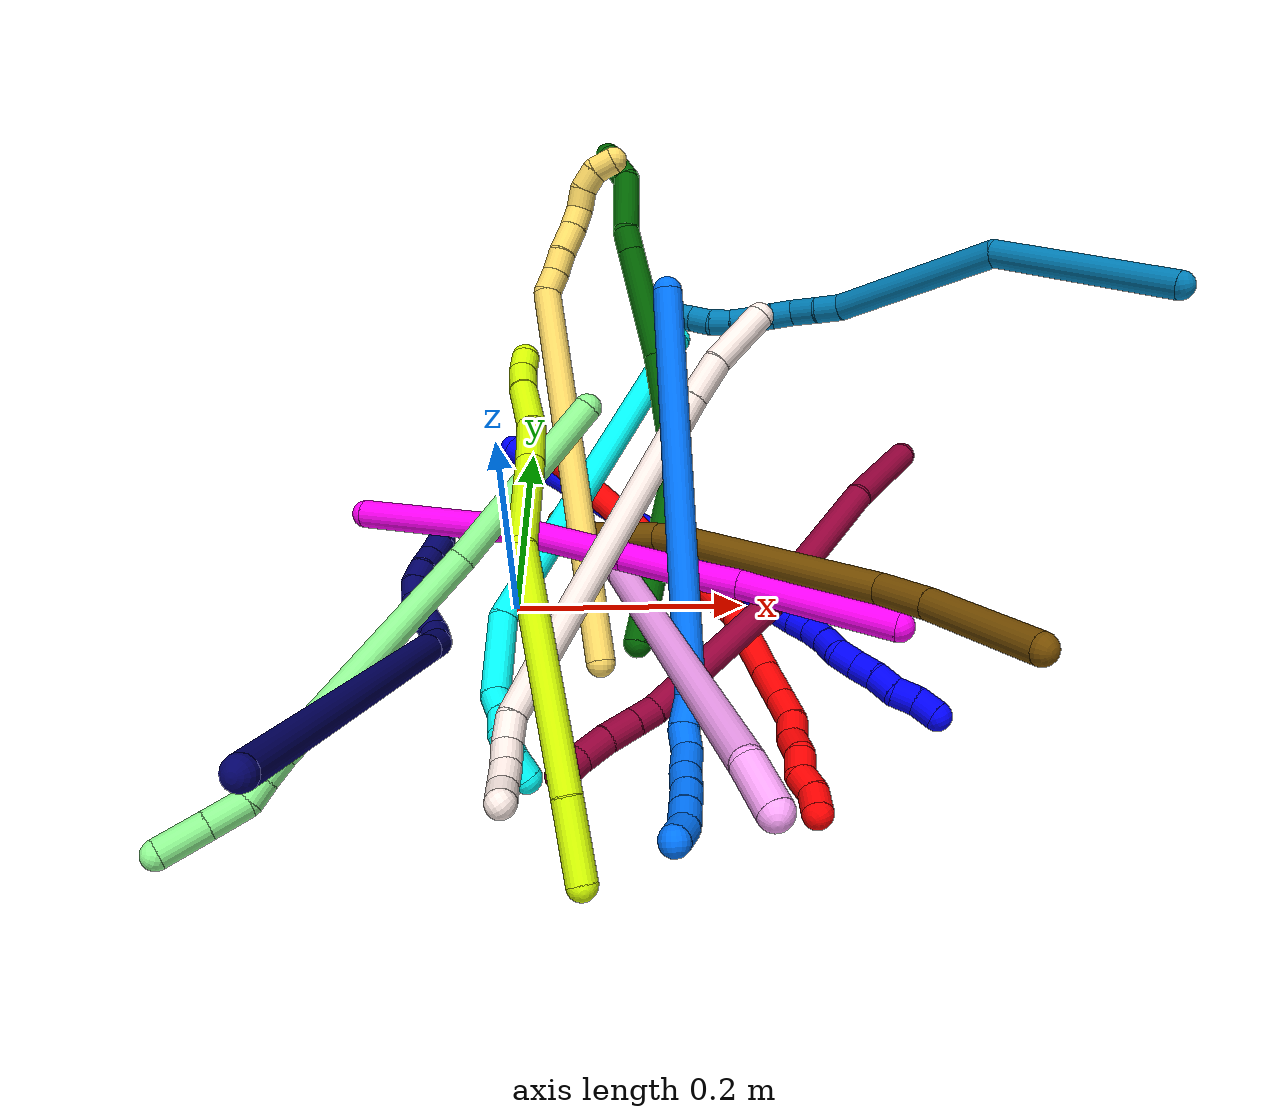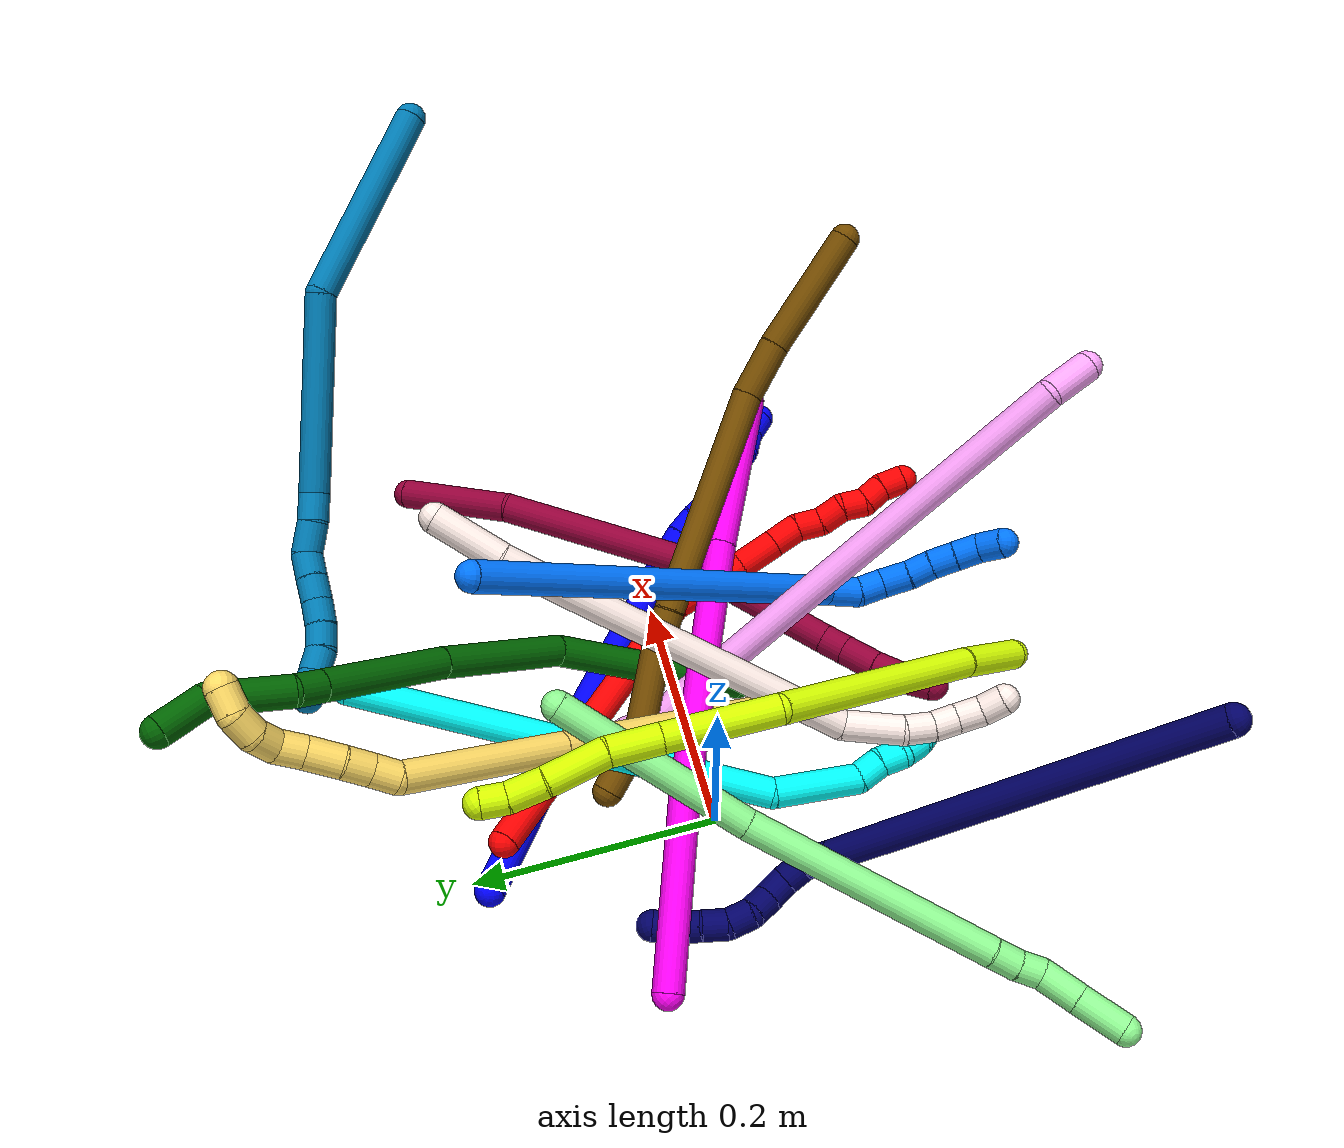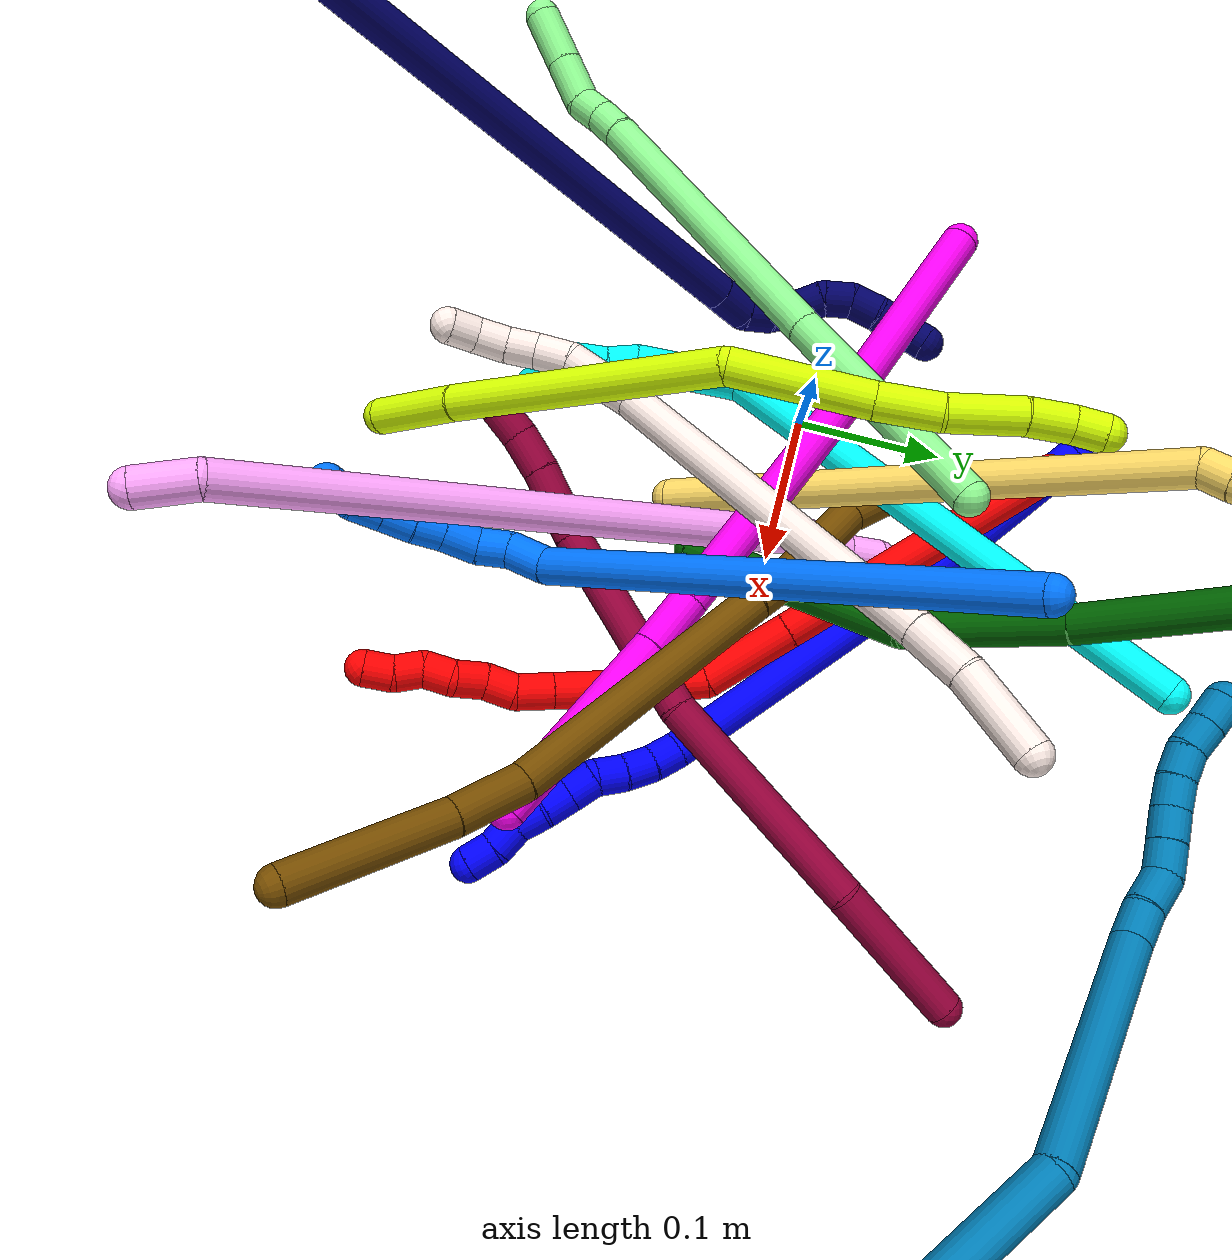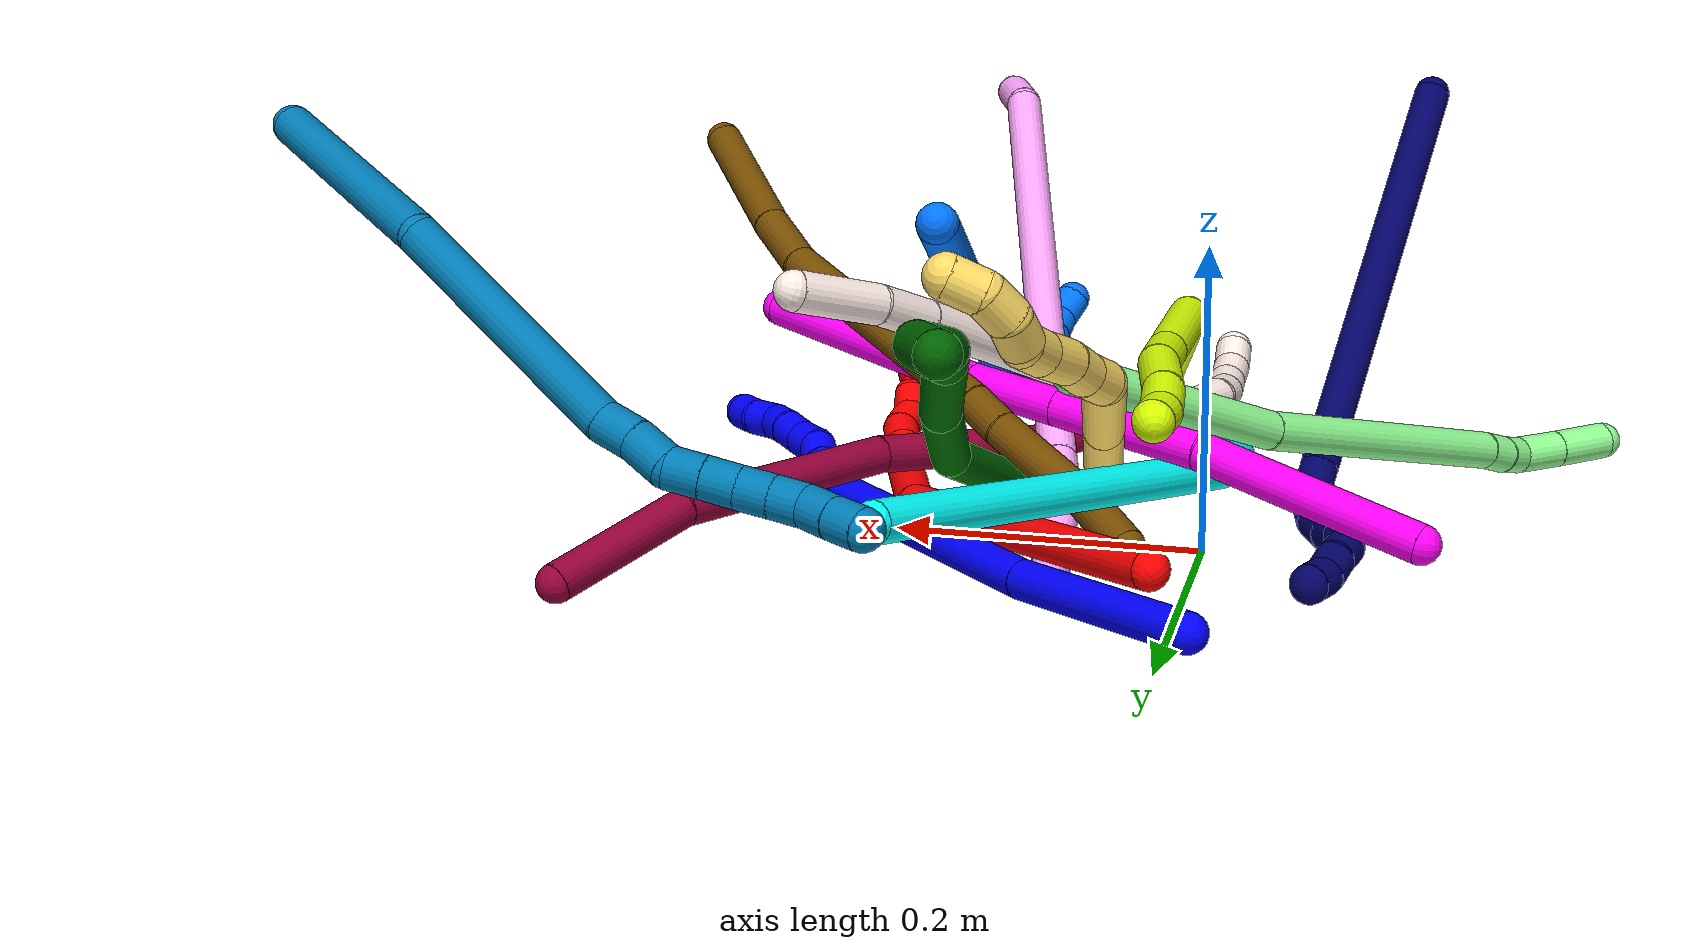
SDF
<sdf version="1.7">
 <world name="default">
  <plugin name="TubeGeneratorPlugin" filename="libtube_generator_plugin.so"/>
  <model name="photoneo_s_sensor">
   <static>1</static>
   <pose>0 0 2 1.57079 1.57079 3.14159</pose>
   <link name="link">
    <inertial><mass>0.1</mass></inertial>
    <sensor name="sensor" type="depth">
     <update_rate>30</update_rate>
     <camera>
      <horizontal_fov>1.22</horizontal_fov>
      <image><width>1920</width><height>1200</height><format>B8G8R8</format></image>
      <clip><near>0.1</near><far>4</far></clip>
      <depth_camera><output>points</output></depth_camera>
     </camera>
     <plugin name="camera_plugin" filename="libgazebo_ros_depth_camera.so">
      <baseline>0.2</baseline>
      <alwaysOn>1</alwaysOn>
      <updateRate>0.0</updateRate>
      <cameraName>camera_ir</cameraName>
      <imageTopicName>/camera/color/image_raw</imageTopicName>
      <cameraInfoTopicName>/camera/color/camera_info</cameraInfoTopicName>
      <depthImageTopicName>/camera/depth/image_raw</depthImageTopicName>
      <depthImageCameraInfoTopicName>/camera/depth/camera_info</depthImageCameraInfoTopicName>
      <pointCloudTopicName>/camera/depth/points</pointCloudTopicName>
      <frameName>fr_optical</frameName>
      <pointCloudCutoff>0.1</pointCloudCutoff>
      <pointCloudCutoffMax>2.0</pointCloudCutoffMax>
      <distortionK1>0</distortionK1>
      <distortionK2>0</distortionK2>
      <distortionK3>0</distortionK3>
      <distortionT1>0</distortionT1>
      <distortionT2>0</distortionT2>
      <CxPrime>0</CxPrime>
      <Cx>0</Cx>
      <Cy>0</Cy>
      <focalLength>0</focalLength>
      <hackBaseline>0</hackBaseline>
     </plugin>
    </sensor>
   </link>
  </model>
  <gravity>0 0 -9.8</gravity>
  <magnetic_field>6e-06 2.3e-05 -4.2e-05</magnetic_field>
  <atmosphere type="adiabatic"/>
  <physics name="default_physics" default="0" type="ode">
   <max_step_size>0.003</max_step_size>
   <real_time_factor>1</real_time_factor>
   <real_time_update_rate>1000</real_time_update_rate>
   <max_contacts>10000</max_contacts>
   <ode>
    <solver>
     <type>quick</type>
     <iters>100</iters>
     <sor>1.3</sor>
     <use_dynamic_moi_rescaling>0</use_dynamic_moi_rescaling>
    </solver>
    <constraints>
     <contact_max_correcting_vel>0</contact_max_correcting_vel>
     <contact_surface_layer>0.001</contact_surface_layer>
     <cfm>0</cfm>
     <erp>0.2</erp>
    </constraints>
   </ode>
  </physics>
  <scene><ambient>0.4 0.4 0.4 1</ambient><background>0.7 0.7 0.7 1</background><shadows>0</shadows></scene>
  <audio><device>default</device></audio>
  <spherical_coordinates>
   <surface_model>EARTH_WGS84</surface_model>
   <latitude_deg>0</latitude_deg>
   <longitude_deg>0</longitude_deg>
   <elevation>0</elevation>
   <heading_deg>0</heading_deg>
  </spherical_coordinates>
  <model name="bin">
   <static>1</static>
   <link name="bottom">
    <collision name="collision-bottom">
     <pose>0 0 -0.01 0 -0 0</pose>
     <geometry><box><size>0.8 0.6 0.02</size></box></geometry>
     <surface>
      <friction><ode><mu>100</mu><mu2>100</mu2></ode></friction>
      <contact><collide_bitmask>65535</collide_bitmask></contact>
     </surface>
    </collision>
   </link>
   <link name="west_wall">
    <collision name="collision-west_wall">
     <pose>-0.41 0 0.1 0 -0 0</pose>
     <geometry><box><size>0.02 0.6 0.2</size></box></geometry>
     <surface>
      <friction><ode><mu>100</mu><mu2>100</mu2></ode></friction>
      <contact><collide_bitmask>65535</collide_bitmask></contact>
     </surface>
    </collision>
   </link>
   <link name="east_wall">
    <collision name="collision-east_wall">
     <pose>0.41 0 0.1 0 -0 0</pose>
     <geometry><box><size>0.02 0.6 0.2</size></box></geometry>
     <surface>
      <friction><ode><mu>100</mu><mu2>100</mu2></ode></friction>
      <contact><collide_bitmask>65535</collide_bitmask></contact>
     </surface>
    </collision>
   </link>
   <link name="south_wall">
    <collision name="collision-south_wall">
     <pose>0 -0.31 0.1 0 -0 0</pose>
     <geometry><box><size>0.8 0.02 0.2</size></box></geometry>
     <surface>
      <friction><ode><mu>100</mu><mu2>100</mu2></ode></friction>
      <contact><collide_bitmask>65535</collide_bitmask></contact>
     </surface>
    </collision>
   </link>
   <link name="north_wall">
    <collision name="collision-north_wall">
     <pose>0 0.31 0.1 0 -0 0</pose>
     <geometry><box><size>0.8 0.02 0.2</size></box></geometry>
     <surface>
      <friction><ode><mu>100</mu><mu2>100</mu2></ode></friction>
      <contact><collide_bitmask>65535</collide_bitmask></contact>
     </surface>
    </collision>
   </link>
  </model>
  <model name="1">
   <static>0</static>
   <link name="1">
    <collision name="collision-cylinder-e_1_1_4">
     <pose>0.045166 -0.015565 0.052991 0.2857 0.68549 0.102555</pose>
     <geometry><cylinder><radius>0.0125</radius><length>0.142691</length></cylinder></geometry>
     <surface>
      <friction><ode><mu>1.16</mu><mu2>1.16</mu2><slip1>0</slip1><slip2>0</slip2></ode></friction>
      <contact><ode><kp>1e+06</kp><kd>1</kd><max_vel>0</max_vel><min_depth>0.001</min_depth></ode></contact>
     </surface>
    </collision>
    <visual name="visual-cylinder-e_1_1_4">
     <pose>0.045166 -0.015565 0.052991 0.2857 0.68549 0.102555</pose>
     <geometry><cylinder><radius>0.0125</radius><length>0.142691</length></cylinder></geometry>
     <material><ambient>0 0 1 1</ambient></material>
    </visual>
    <collision name="collision-cylinder-e_2_4_5">
     <pose>0.158016 -0.045309 0.176106 0.199503 0.75769 0.079639</pose>
     <geometry><cylinder><radius>0.0125</radius><length>0.196974</length></cylinder></geometry>
     <surface>
      <friction><ode><mu>1.16</mu><mu2>1.16</mu2><slip1>0</slip1><slip2>0</slip2></ode></friction>
      <contact><ode><kp>1e+06</kp><kd>1</kd><max_vel>0</max_vel><min_depth>0.001</min_depth></ode></contact>
     </surface>
    </collision>
    <visual name="visual-cylinder-e_2_4_5">
     <pose>0.158016 -0.045309 0.176106 0.199503 0.75769 0.079639</pose>
     <geometry><cylinder><radius>0.0125</radius><length>0.196974</length></cylinder></geometry>
     <material><ambient>0 0 1 1</ambient></material>
    </visual>
    <collision name="collision-cylinder-e_3_5_6">
     <pose>0.233965 -0.059517 0.252031 0.004991 0.958743 0.002594</pose>
     <geometry><cylinder><radius>0.0125</radius><length>0.020195</length></cylinder></geometry>
     <surface>
      <friction><ode><mu>1.16</mu><mu2>1.16</mu2><slip1>0</slip1><slip2>0</slip2></ode></friction>
      <contact><ode><kp>1e+06</kp><kd>1</kd><max_vel>0</max_vel><min_depth>0.001</min_depth></ode></contact>
     </surface>
    </collision>
    <visual name="visual-cylinder-e_3_5_6">
     <pose>0.233965 -0.059517 0.252031 0.004991 0.958743 0.002594</pose>
     <geometry><cylinder><radius>0.0125</radius><length>0.020195</length></cylinder></geometry>
     <material><ambient>0 0 1 1</ambient></material>
    </visual>
    <collision name="collision-cylinder-e_4_6_7">
     <pose>0.250354 -0.057813 0.263498 -0.296875 0.940717 -0.151763</pose>
     <geometry><cylinder><radius>0.0125</radius><length>0.020111</length></cylinder></geometry>
     <surface>
      <friction><ode><mu>1.16</mu><mu2>1.16</mu2><slip1>0</slip1><slip2>0</slip2></ode></friction>
      <contact><ode><kp>1e+06</kp><kd>1</kd><max_vel>0</max_vel><min_depth>0.001</min_depth></ode></contact>
     </surface>
    </collision>
    <visual name="visual-cylinder-e_4_6_7">
     <pose>0.250354 -0.057813 0.263498 -0.296875 0.940717 -0.151763</pose>
     <geometry><cylinder><radius>0.0125</radius><length>0.020111</length></cylinder></geometry>
     <material><ambient>0 0 1 1</ambient></material>
    </visual>
    <collision name="collision-cylinder-e_5_7_8">
     <pose>0.266189 -0.052908 0.274711 -0.519428 0.878803 -0.248512</pose>
     <geometry><cylinder><radius>0.0125</radius><length>0.020029</length></cylinder></geometry>
     <surface>
      <friction><ode><mu>1.16</mu><mu2>1.16</mu2><slip1>0</slip1><slip2>0</slip2></ode></friction>
      <contact><ode><kp>1e+06</kp><kd>1</kd><max_vel>0</max_vel><min_depth>0.001</min_depth></ode></contact>
     </surface>
    </collision>
    <visual name="visual-cylinder-e_5_7_8">
     <pose>0.266189 -0.052908 0.274711 -0.519428 0.878803 -0.248512</pose>
     <geometry><cylinder><radius>0.0125</radius><length>0.020029</length></cylinder></geometry>
     <material><ambient>0 0 1 1</ambient></material>
    </visual>
    <collision name="collision-cylinder-e_6_8_9">
     <pose>0.28076 -0.05088 0.287444 0.157911 0.755921 0.062809</pose>
     <geometry><cylinder><radius>0.0125</radius><length>0.02</length></cylinder></geometry>
     <surface>
      <friction><ode><mu>1.16</mu><mu2>1.16</mu2><slip1>0</slip1><slip2>0</slip2></ode></friction>
      <contact><ode><kp>1e+06</kp><kd>1</kd><max_vel>0</max_vel><min_depth>0.001</min_depth></ode></contact>
     </surface>
    </collision>
    <visual name="visual-cylinder-e_6_8_9">
     <pose>0.28076 -0.05088 0.287444 0.157911 0.755921 0.062809</pose>
     <geometry><cylinder><radius>0.0125</radius><length>0.02</length></cylinder></geometry>
     <material><ambient>0 0 1 1</ambient></material>
    </visual>
    <collision name="collision-cylinder-e_7_9_10">
     <pose>0.295263 -0.052781 0.301034 0.117565 0.869972 0.054678</pose>
     <geometry><cylinder><radius>0.0125</radius><length>0.02</length></cylinder></geometry>
     <surface>
      <friction><ode><mu>1.16</mu><mu2>1.16</mu2><slip1>0</slip1><slip2>0</slip2></ode></friction>
      <contact><ode><kp>1e+06</kp><kd>1</kd><max_vel>0</max_vel><min_depth>0.001</min_depth></ode></contact>
     </surface>
    </collision>
    <visual name="visual-cylinder-e_7_9_10">
     <pose>0.295263 -0.052781 0.301034 0.117565 0.869972 0.054678</pose>
     <geometry><cylinder><radius>0.0125</radius><length>0.02</length></cylinder></geometry>
     <material><ambient>0 0 1 1</ambient></material>
    </visual>
    <collision name="collision-cylinder-e_8_10_11">
     <pose>0.309321 -0.053836 0.315103 0.03903 0.696447 0.01417</pose>
     <geometry><cylinder><radius>0.0125</radius><length>0.02</length></cylinder></geometry>
     <surface>
      <friction><ode><mu>1.16</mu><mu2>1.16</mu2><slip1>0</slip1><slip2>0</slip2></ode></friction>
      <contact><ode><kp>1e+06</kp><kd>1</kd><max_vel>0</max_vel><min_depth>0.001</min_depth></ode></contact>
     </surface>
    </collision>
    <visual name="visual-cylinder-e_8_10_11">
     <pose>0.309321 -0.053836 0.315103 0.03903 0.696447 0.01417</pose>
     <geometry><cylinder><radius>0.0125</radius><length>0.02</length></cylinder></geometry>
     <material><ambient>0 0 1 1</ambient></material>
    </visual>
    <collision name="collision-cylinder-e_9_11_12">
     <pose>0.322276 -0.05781 0.329381 0.507198 0.712908 0.19242</pose>
     <geometry><cylinder><radius>0.0125</radius><length>0.02</length></cylinder></geometry>
     <surface>
      <friction><ode><mu>1.16</mu><mu2>1.16</mu2><slip1>0</slip1><slip2>0</slip2></ode></friction>
      <contact><ode><kp>1e+06</kp><kd>1</kd><max_vel>0</max_vel><min_depth>0.001</min_depth></ode></contact>
     </surface>
    </collision>
    <visual name="visual-cylinder-e_9_11_12">
     <pose>0.322276 -0.05781 0.329381 0.507198 0.712908 0.19242</pose>
     <geometry><cylinder><radius>0.0125</radius><length>0.02</length></cylinder></geometry>
     <material><ambient>0 0 1 1</ambient></material>
    </visual>
    <collision name="collision-cylinder-e_10_12_2">
     <pose>0.335222 -0.062353 0.343623 0.113301 0.695223 0.04109</pose>
     <geometry><cylinder><radius>0.0125</radius><length>0.02</length></cylinder></geometry>
     <surface>
      <friction><ode><mu>1.16</mu><mu2>1.16</mu2><slip1>0</slip1><slip2>0</slip2></ode></friction>
      <contact><ode><kp>1e+06</kp><kd>1</kd><max_vel>0</max_vel><min_depth>0.001</min_depth></ode></contact>
     </surface>
    </collision>
    <visual name="visual-cylinder-e_10_12_2">
     <pose>0.335222 -0.062353 0.343623 0.113301 0.695223 0.04109</pose>
     <geometry><cylinder><radius>0.0125</radius><length>0.02</length></cylinder></geometry>
     <material><ambient>0 0 1 1</ambient></material>
    </visual>
    <collision name="collision-sphere-2">
     <pose>0.341628 -0.063221 0.351253 0 -0 0</pose>
     <geometry><sphere><radius>0.0125</radius></sphere></geometry>
     <surface>
      <friction><ode><mu>1.16</mu><mu2>1.16</mu2><slip1>0</slip1><slip2>0</slip2></ode></friction>
      <contact><ode><kp>1e+06</kp><kd>1</kd><max_vel>0</max_vel><min_depth>0.001</min_depth></ode></contact>
     </surface>
    </collision>
    <visual name="visual-sphere-2">
     <pose>0.341628 -0.063221 0.351253 0 -0 0</pose>
     <geometry><sphere><radius>0.0125</radius></sphere></geometry>
     <material><ambient>0 0 1 1</ambient></material>
    </visual>
    <collision name="collision-sphere-12">
     <pose>0.328816 -0.061484 0.335993 0 -0 0</pose>
     <geometry><sphere><radius>0.0125</radius></sphere></geometry>
     <surface>
      <friction><ode><mu>1.16</mu><mu2>1.16</mu2><slip1>0</slip1><slip2>0</slip2></ode></friction>
      <contact><ode><kp>1e+06</kp><kd>1</kd><max_vel>0</max_vel><min_depth>0.001</min_depth></ode></contact>
     </surface>
    </collision>
    <visual name="visual-sphere-12">
     <pose>0.328816 -0.061484 0.335993 0 -0 0</pose>
     <geometry><sphere><radius>0.0125</radius></sphere></geometry>
     <material><ambient>0 0 1 1</ambient></material>
    </visual>
    <collision name="collision-sphere-11">
     <pose>0.315736 -0.054136 0.322769 0 -0 0</pose>
     <geometry><sphere><radius>0.0125</radius></sphere></geometry>
     <surface>
      <friction><ode><mu>1.16</mu><mu2>1.16</mu2><slip1>0</slip1><slip2>0</slip2></ode></friction>
      <contact><ode><kp>1e+06</kp><kd>1</kd><max_vel>0</max_vel><min_depth>0.001</min_depth></ode></contact>
     </surface>
    </collision>
    <visual name="visual-sphere-11">
     <pose>0.315736 -0.054136 0.322769 0 -0 0</pose>
     <geometry><sphere><radius>0.0125</radius></sphere></geometry>
     <material><ambient>0 0 1 1</ambient></material>
    </visual>
    <collision name="collision-sphere-10">
     <pose>0.302906 -0.053537 0.307438 0 -0 0</pose>
     <geometry><sphere><radius>0.0125</radius></sphere></geometry>
     <surface>
      <friction><ode><mu>1.16</mu><mu2>1.16</mu2><slip1>0</slip1><slip2>0</slip2></ode></friction>
      <contact><ode><kp>1e+06</kp><kd>1</kd><max_vel>0</max_vel><min_depth>0.001</min_depth></ode></contact>
     </surface>
    </collision>
    <visual name="visual-sphere-10">
     <pose>0.302906 -0.053537 0.307438 0 -0 0</pose>
     <geometry><sphere><radius>0.0125</radius></sphere></geometry>
     <material><ambient>0 0 1 1</ambient></material>
    </visual>
    <collision name="collision-sphere-9">
     <pose>0.287619 -0.052024 0.29463 0 -0 0</pose>
     <geometry><sphere><radius>0.0125</radius></sphere></geometry>
     <surface>
      <friction><ode><mu>1.16</mu><mu2>1.16</mu2><slip1>0</slip1><slip2>0</slip2></ode></friction>
      <contact><ode><kp>1e+06</kp><kd>1</kd><max_vel>0</max_vel><min_depth>0.001</min_depth></ode></contact>
     </surface>
    </collision>
    <visual name="visual-sphere-9">
     <pose>0.287619 -0.052024 0.29463 0 -0 0</pose>
     <geometry><sphere><radius>0.0125</radius></sphere></geometry>
     <material><ambient>0 0 1 1</ambient></material>
    </visual>
    <collision name="collision-sphere-4">
     <pose>0.090331 -0.03113 0.105981 0 -0 0</pose>
     <geometry><sphere><radius>0.0125</radius></sphere></geometry>
     <surface>
      <friction><ode><mu>1.16</mu><mu2>1.16</mu2><slip1>0</slip1><slip2>0</slip2></ode></friction>
      <contact><ode><kp>1e+06</kp><kd>1</kd><max_vel>0</max_vel><min_depth>0.001</min_depth></ode></contact>
     </surface>
    </collision>
    <visual name="visual-sphere-4">
     <pose>0.090331 -0.03113 0.105981 0 -0 0</pose>
     <geometry><sphere><radius>0.0125</radius></sphere></geometry>
     <material><ambient>0 0 1 1</ambient></material>
    </visual>
    <collision name="collision-sphere-1">
     <geometry><sphere><radius>0.0125</radius></sphere></geometry>
     <surface>
      <friction><ode><mu>1.16</mu><mu2>1.16</mu2><slip1>0</slip1><slip2>0</slip2></ode></friction>
      <contact><ode><kp>1e+06</kp><kd>1</kd><max_vel>0</max_vel><min_depth>0.001</min_depth></ode></contact>
     </surface>
    </collision>
    <visual name="visual-sphere-1">
     <geometry><sphere><radius>0.0125</radius></sphere></geometry>
     <material><ambient>0 0 1 1</ambient></material>
    </visual>
    <collision name="collision-sphere-8">
     <pose>0.2739 -0.049736 0.280258 0 -0 0</pose>
     <geometry><sphere><radius>0.0125</radius></sphere></geometry>
     <surface>
      <friction><ode><mu>1.16</mu><mu2>1.16</mu2><slip1>0</slip1><slip2>0</slip2></ode></friction>
      <contact><ode><kp>1e+06</kp><kd>1</kd><max_vel>0</max_vel><min_depth>0.001</min_depth></ode></contact>
     </surface>
    </collision>
    <visual name="visual-sphere-8">
     <pose>0.2739 -0.049736 0.280258 0 -0 0</pose>
     <geometry><sphere><radius>0.0125</radius></sphere></geometry>
     <material><ambient>0 0 1 1</ambient></material>
    </visual>
    <collision name="collision-sphere-5">
     <pose>0.225701 -0.059488 0.24623 0 -0 0</pose>
     <geometry><sphere><radius>0.0125</radius></sphere></geometry>
     <surface>
      <friction><ode><mu>1.16</mu><mu2>1.16</mu2><slip1>0</slip1><slip2>0</slip2></ode></friction>
      <contact><ode><kp>1e+06</kp><kd>1</kd><max_vel>0</max_vel><min_depth>0.001</min_depth></ode></contact>
     </surface>
    </collision>
    <visual name="visual-sphere-5">
     <pose>0.225701 -0.059488 0.24623 0 -0 0</pose>
     <geometry><sphere><radius>0.0125</radius></sphere></geometry>
     <material><ambient>0 0 1 1</ambient></material>
    </visual>
    <collision name="collision-sphere-6">
     <pose>0.24223 -0.059546 0.257833 0 -0 0</pose>
     <geometry><sphere><radius>0.0125</radius></sphere></geometry>
     <surface>
      <friction><ode><mu>1.16</mu><mu2>1.16</mu2><slip1>0</slip1><slip2>0</slip2></ode></friction>
      <contact><ode><kp>1e+06</kp><kd>1</kd><max_vel>0</max_vel><min_depth>0.001</min_depth></ode></contact>
     </surface>
    </collision>
    <visual name="visual-sphere-6">
     <pose>0.24223 -0.059546 0.257833 0 -0 0</pose>
     <geometry><sphere><radius>0.0125</radius></sphere></geometry>
     <material><ambient>0 0 1 1</ambient></material>
    </visual>
    <collision name="collision-sphere-7">
     <pose>0.258479 -0.056079 0.269164 0 -0 0</pose>
     <geometry><sphere><radius>0.0125</radius></sphere></geometry>
     <surface>
      <friction><ode><mu>1.16</mu><mu2>1.16</mu2><slip1>0</slip1><slip2>0</slip2></ode></friction>
      <contact><ode><kp>1e+06</kp><kd>1</kd><max_vel>0</max_vel><min_depth>0.001</min_depth></ode></contact>
     </surface>
    </collision>
    <visual name="visual-sphere-7">
     <pose>0.258479 -0.056079 0.269164 0 -0 0</pose>
     <geometry><sphere><radius>0.0125</radius></sphere></geometry>
     <material><ambient>0 0 1 1</ambient></material>
    </visual>
    <inertial>
     <pose>0.167036 -0.040246 0.179345 0 -0 0</pose>
     <mass>0.5</mass>
     <inertia>
      <ixx>0.000749</ixx>
      <ixy>0</ixy>
      <ixz>0</ixz>
      <iyy>0.000941</iyy>
      <iyz>0</iyz>
      <izz>-0.000434</izz>
     </inertia>
    </inertial>
   </link>
   <pose>-0.017171 0.187613 0.022142 2.81825 -0.810275 -0.626008</pose>
  </model>
  <model name="2">
   <static>0</static>
   <link name="2">
    <collision name="collision-cylinder-e_1_1_4">
     <pose>0.075591 -0.065773 0.015669 1.33692 0.841052 0.679008</pose>
     <geometry><cylinder><radius>0.0125</radius><length>0.202836</length></cylinder></geometry>
     <surface>
      <friction><ode><mu>1.16</mu><mu2>1.16</mu2><slip1>0</slip1><slip2>0</slip2></ode></friction>
      <contact><ode><kp>1e+06</kp><kd>1</kd><max_vel>0</max_vel><min_depth>0.001</min_depth></ode></contact>
     </surface>
    </collision>
    <visual name="visual-cylinder-e_1_1_4">
     <pose>0.075591 -0.065773 0.015669 1.33692 0.841052 0.679008</pose>
     <geometry><cylinder><radius>0.0125</radius><length>0.202836</length></cylinder></geometry>
     <material><ambient>1 0 0 1</ambient></material>
    </visual>
    <collision name="collision-cylinder-e_2_4_5">
     <pose>0.174928 -0.152079 0.036251 1.336 0.843997 0.680898</pose>
     <geometry><cylinder><radius>0.0125</radius><length>0.063547</length></cylinder></geometry>
     <surface>
      <friction><ode><mu>1.16</mu><mu2>1.16</mu2><slip1>0</slip1><slip2>0</slip2></ode></friction>
      <contact><ode><kp>1e+06</kp><kd>1</kd><max_vel>0</max_vel><min_depth>0.001</min_depth></ode></contact>
     </surface>
    </collision>
    <visual name="visual-cylinder-e_2_4_5">
     <pose>0.174928 -0.152079 0.036251 1.336 0.843997 0.680898</pose>
     <geometry><cylinder><radius>0.0125</radius><length>0.063547</length></cylinder></geometry>
     <material><ambient>1 0 0 1</ambient></material>
    </visual>
    <collision name="collision-cylinder-e_3_5_6">
     <pose>0.21856 -0.192362 0.060948 0.784487 0.618344 0.262749</pose>
     <geometry><cylinder><radius>0.0125</radius><length>0.068614</length></cylinder></geometry>
     <surface>
      <friction><ode><mu>1.16</mu><mu2>1.16</mu2><slip1>0</slip1><slip2>0</slip2></ode></friction>
      <contact><ode><kp>1e+06</kp><kd>1</kd><max_vel>0</max_vel><min_depth>0.001</min_depth></ode></contact>
     </surface>
    </collision>
    <visual name="visual-cylinder-e_3_5_6">
     <pose>0.21856 -0.192362 0.060948 0.784487 0.618344 0.262749</pose>
     <geometry><cylinder><radius>0.0125</radius><length>0.068614</length></cylinder></geometry>
     <material><ambient>1 0 0 1</ambient></material>
    </visual>
    <collision name="collision-cylinder-e_4_6_7">
     <pose>0.249601 -0.219854 0.09238 0.586743 0.673185 0.210624</pose>
     <geometry><cylinder><radius>0.0125</radius><length>0.035779</length></cylinder></geometry>
     <surface>
      <friction><ode><mu>1.16</mu><mu2>1.16</mu2><slip1>0</slip1><slip2>0</slip2></ode></friction>
      <contact><ode><kp>1e+06</kp><kd>1</kd><max_vel>0</max_vel><min_depth>0.001</min_depth></ode></contact>
     </surface>
    </collision>
    <visual name="visual-cylinder-e_4_6_7">
     <pose>0.249601 -0.219854 0.09238 0.586743 0.673185 0.210624</pose>
     <geometry><cylinder><radius>0.0125</radius><length>0.035779</length></cylinder></geometry>
     <material><ambient>1 0 0 1</ambient></material>
    </visual>
    <collision name="collision-cylinder-e_5_7_8">
     <pose>0.268628 -0.233057 0.112299 0.583307 0.671339 0.208712</pose>
     <geometry><cylinder><radius>0.0125</radius><length>0.025314</length></cylinder></geometry>
     <surface>
      <friction><ode><mu>1.16</mu><mu2>1.16</mu2><slip1>0</slip1><slip2>0</slip2></ode></friction>
      <contact><ode><kp>1e+06</kp><kd>1</kd><max_vel>0</max_vel><min_depth>0.001</min_depth></ode></contact>
     </surface>
    </collision>
    <visual name="visual-cylinder-e_5_7_8">
     <pose>0.268628 -0.233057 0.112299 0.583307 0.671339 0.208712</pose>
     <geometry><cylinder><radius>0.0125</radius><length>0.025314</length></cylinder></geometry>
     <material><ambient>1 0 0 1</ambient></material>
    </visual>
    <collision name="collision-cylinder-e_6_8_9">
     <pose>0.27991 -0.242569 0.130148 0.400454 0.31675 0.064803</pose>
     <geometry><cylinder><radius>0.0125</radius><length>0.021889</length></cylinder></geometry>
     <surface>
      <friction><ode><mu>1.16</mu><mu2>1.16</mu2><slip1>0</slip1><slip2>0</slip2></ode></friction>
      <contact><ode><kp>1e+06</kp><kd>1</kd><max_vel>0</max_vel><min_depth>0.001</min_depth></ode></contact>
     </surface>
    </collision>
    <visual name="visual-cylinder-e_6_8_9">
     <pose>0.27991 -0.242569 0.130148 0.400454 0.31675 0.064803</pose>
     <geometry><cylinder><radius>0.0125</radius><length>0.021889</length></cylinder></geometry>
     <material><ambient>1 0 0 1</ambient></material>
    </visual>
    <collision name="collision-cylinder-e_7_9_10">
     <pose>0.2901 -0.24893 0.148033 0.270782 0.666492 0.09424</pose>
     <geometry><cylinder><radius>0.0125</radius><length>0.021938</length></cylinder></geometry>
     <surface>
      <friction><ode><mu>1.16</mu><mu2>1.16</mu2><slip1>0</slip1><slip2>0</slip2></ode></friction>
      <contact><ode><kp>1e+06</kp><kd>1</kd><max_vel>0</max_vel><min_depth>0.001</min_depth></ode></contact>
     </surface>
    </collision>
    <visual name="visual-cylinder-e_7_9_10">
     <pose>0.2901 -0.24893 0.148033 0.270782 0.666492 0.09424</pose>
     <geometry><cylinder><radius>0.0125</radius><length>0.021938</length></cylinder></geometry>
     <material><ambient>1 0 0 1</ambient></material>
    </visual>
    <collision name="collision-cylinder-e_8_10_11">
     <pose>0.299851 -0.255943 0.16466 0.514791 0.301192 0.079846</pose>
     <geometry><cylinder><radius>0.0125</radius><length>0.02002</length></cylinder></geometry>
     <surface>
      <friction><ode><mu>1.16</mu><mu2>1.16</mu2><slip1>0</slip1><slip2>0</slip2></ode></friction>
      <contact><ode><kp>1e+06</kp><kd>1</kd><max_vel>0</max_vel><min_depth>0.001</min_depth></ode></contact>
     </surface>
    </collision>
    <visual name="visual-cylinder-e_8_10_11">
     <pose>0.299851 -0.255943 0.16466 0.514791 0.301192 0.079846</pose>
     <geometry><cylinder><radius>0.0125</radius><length>0.02002</length></cylinder></geometry>
     <material><ambient>1 0 0 1</ambient></material>
    </visual>
    <collision name="collision-cylinder-e_9_11_12">
     <pose>0.309927 -0.264933 0.178573 0.65372 0.789804 0.280746</pose>
     <geometry><cylinder><radius>0.0125</radius><length>0.020014</length></cylinder></geometry>
     <surface>
      <friction><ode><mu>1.16</mu><mu2>1.16</mu2><slip1>0</slip1><slip2>0</slip2></ode></friction>
      <contact><ode><kp>1e+06</kp><kd>1</kd><max_vel>0</max_vel><min_depth>0.001</min_depth></ode></contact>
     </surface>
    </collision>
    <visual name="visual-cylinder-e_9_11_12">
     <pose>0.309927 -0.264933 0.178573 0.65372 0.789804 0.280746</pose>
     <geometry><cylinder><radius>0.0125</radius><length>0.020014</length></cylinder></geometry>
     <material><ambient>1 0 0 1</ambient></material>
    </visual>
    <collision name="collision-cylinder-e_10_12_2">
     <pose>0.321445 -0.273405 0.192134 0.483861 0.455605 0.114288</pose>
     <geometry><cylinder><radius>0.0125</radius><length>0.020049</length></cylinder></geometry>
     <surface>
      <friction><ode><mu>1.16</mu><mu2>1.16</mu2><slip1>0</slip1><slip2>0</slip2></ode></friction>
      <contact><ode><kp>1e+06</kp><kd>1</kd><max_vel>0</max_vel><min_depth>0.001</min_depth></ode></contact>
     </surface>
    </collision>
    <visual name="visual-cylinder-e_10_12_2">
     <pose>0.321445 -0.273405 0.192134 0.483861 0.455605 0.114288</pose>
     <geometry><cylinder><radius>0.0125</radius><length>0.020049</length></cylinder></geometry>
     <material><ambient>1 0 0 1</ambient></material>
    </visual>
    <collision name="collision-sphere-2">
     <pose>0.325856 -0.277593 0.200102 0 -0 0</pose>
     <geometry><sphere><radius>0.0125</radius></sphere></geometry>
     <surface>
      <friction><ode><mu>1.16</mu><mu2>1.16</mu2><slip1>0</slip1><slip2>0</slip2></ode></friction>
      <contact><ode><kp>1e+06</kp><kd>1</kd><max_vel>0</max_vel><min_depth>0.001</min_depth></ode></contact>
     </surface>
    </collision>
    <visual name="visual-sphere-2">
     <pose>0.325856 -0.277593 0.200102 0 -0 0</pose>
     <geometry><sphere><radius>0.0125</radius></sphere></geometry>
     <material><ambient>1 0 0 1</ambient></material>
    </visual>
    <collision name="collision-sphere-12">
     <pose>0.317034 -0.269218 0.184165 0 -0 0</pose>
     <geometry><sphere><radius>0.0125</radius></sphere></geometry>
     <surface>
      <friction><ode><mu>1.16</mu><mu2>1.16</mu2><slip1>0</slip1><slip2>0</slip2></ode></friction>
      <contact><ode><kp>1e+06</kp><kd>1</kd><max_vel>0</max_vel><min_depth>0.001</min_depth></ode></contact>
     </surface>
    </collision>
    <visual name="visual-sphere-12">
     <pose>0.317034 -0.269218 0.184165 0 -0 0</pose>
     <geometry><sphere><radius>0.0125</radius></sphere></geometry>
     <material><ambient>1 0 0 1</ambient></material>
    </visual>
    <collision name="collision-sphere-11">
     <pose>0.30282 -0.260649 0.172981 0 -0 0</pose>
     <geometry><sphere><radius>0.0125</radius></sphere></geometry>
     <surface>
      <friction><ode><mu>1.16</mu><mu2>1.16</mu2><slip1>0</slip1><slip2>0</slip2></ode></friction>
      <contact><ode><kp>1e+06</kp><kd>1</kd><max_vel>0</max_vel><min_depth>0.001</min_depth></ode></contact>
     </surface>
    </collision>
    <visual name="visual-sphere-11">
     <pose>0.30282 -0.260649 0.172981 0 -0 0</pose>
     <geometry><sphere><radius>0.0125</radius></sphere></geometry>
     <material><ambient>1 0 0 1</ambient></material>
    </visual>
    <collision name="collision-sphere-10">
     <pose>0.296881 -0.251236 0.15634 0 -0 0</pose>
     <geometry><sphere><radius>0.0125</radius></sphere></geometry>
     <surface>
      <friction><ode><mu>1.16</mu><mu2>1.16</mu2><slip1>0</slip1><slip2>0</slip2></ode></friction>
      <contact><ode><kp>1e+06</kp><kd>1</kd><max_vel>0</max_vel><min_depth>0.001</min_depth></ode></contact>
     </surface>
    </collision>
    <visual name="visual-sphere-10">
     <pose>0.296881 -0.251236 0.15634 0 -0 0</pose>
     <geometry><sphere><radius>0.0125</radius></sphere></geometry>
     <material><ambient>1 0 0 1</ambient></material>
    </visual>
    <collision name="collision-sphere-9">
     <pose>0.283319 -0.246624 0.139725 0 -0 0</pose>
     <geometry><sphere><radius>0.0125</radius></sphere></geometry>
     <surface>
      <friction><ode><mu>1.16</mu><mu2>1.16</mu2><slip1>0</slip1><slip2>0</slip2></ode></friction>
      <contact><ode><kp>1e+06</kp><kd>1</kd><max_vel>0</max_vel><min_depth>0.001</min_depth></ode></contact>
     </surface>
    </collision>
    <visual name="visual-sphere-9">
     <pose>0.283319 -0.246624 0.139725 0 -0 0</pose>
     <geometry><sphere><radius>0.0125</radius></sphere></geometry>
     <material><ambient>1 0 0 1</ambient></material>
    </visual>
    <collision name="collision-sphere-4">
     <pose>0.151183 -0.131545 0.031339 0 -0 0</pose>
     <geometry><sphere><radius>0.0125</radius></sphere></geometry>
     <surface>
      <friction><ode><mu>1.16</mu><mu2>1.16</mu2><slip1>0</slip1><slip2>0</slip2></ode></friction>
      <contact><ode><kp>1e+06</kp><kd>1</kd><max_vel>0</max_vel><min_depth>0.001</min_depth></ode></contact>
     </surface>
    </collision>
    <visual name="visual-sphere-4">
     <pose>0.151183 -0.131545 0.031339 0 -0 0</pose>
     <geometry><sphere><radius>0.0125</radius></sphere></geometry>
     <material><ambient>1 0 0 1</ambient></material>
    </visual>
    <collision name="collision-sphere-1">
     <geometry><sphere><radius>0.0125</radius></sphere></geometry>
     <surface>
      <friction><ode><mu>1.16</mu><mu2>1.16</mu2><slip1>0</slip1><slip2>0</slip2></ode></friction>
      <contact><ode><kp>1e+06</kp><kd>1</kd><max_vel>0</max_vel><min_depth>0.001</min_depth></ode></contact>
     </surface>
    </collision>
    <visual name="visual-sphere-1">
     <geometry><sphere><radius>0.0125</radius></sphere></geometry>
     <material><ambient>1 0 0 1</ambient></material>
    </visual>
    <collision name="collision-sphere-8">
     <pose>0.276501 -0.238515 0.12057 0 -0 0</pose>
     <geometry><sphere><radius>0.0125</radius></sphere></geometry>
     <surface>
      <friction><ode><mu>1.16</mu><mu2>1.16</mu2><slip1>0</slip1><slip2>0</slip2></ode></friction>
      <contact><ode><kp>1e+06</kp><kd>1</kd><max_vel>0</max_vel><min_depth>0.001</min_depth></ode></contact>
     </surface>
    </collision>
    <visual name="visual-sphere-8">
     <pose>0.276501 -0.238515 0.12057 0 -0 0</pose>
     <geometry><sphere><radius>0.0125</radius></sphere></geometry>
     <material><ambient>1 0 0 1</ambient></material>
    </visual>
    <collision name="collision-sphere-5">
     <pose>0.198672 -0.172613 0.041163 0 -0 0</pose>
     <geometry><sphere><radius>0.0125</radius></sphere></geometry>
     <surface>
      <friction><ode><mu>1.16</mu><mu2>1.16</mu2><slip1>0</slip1><slip2>0</slip2></ode></friction>
      <contact><ode><kp>1e+06</kp><kd>1</kd><max_vel>0</max_vel><min_depth>0.001</min_depth></ode></contact>
     </surface>
    </collision>
    <visual name="visual-sphere-5">
     <pose>0.198672 -0.172613 0.041163 0 -0 0</pose>
     <geometry><sphere><radius>0.0125</radius></sphere></geometry>
     <material><ambient>1 0 0 1</ambient></material>
    </visual>
    <collision name="collision-sphere-6">
     <pose>0.238447 -0.212111 0.080733 0 -0 0</pose>
     <geometry><sphere><radius>0.0125</radius></sphere></geometry>
     <surface>
      <friction><ode><mu>1.16</mu><mu2>1.16</mu2><slip1>0</slip1><slip2>0</slip2></ode></friction>
      <contact><ode><kp>1e+06</kp><kd>1</kd><max_vel>0</max_vel><min_depth>0.001</min_depth></ode></contact>
     </surface>
    </collision>
    <visual name="visual-sphere-6">
     <pose>0.238447 -0.212111 0.080733 0 -0 0</pose>
     <geometry><sphere><radius>0.0125</radius></sphere></geometry>
     <material><ambient>1 0 0 1</ambient></material>
    </visual>
    <collision name="collision-sphere-7">
     <pose>0.260754 -0.227598 0.104027 0 -0 0</pose>
     <geometry><sphere><radius>0.0125</radius></sphere></geometry>
     <surface>
      <friction><ode><mu>1.16</mu><mu2>1.16</mu2><slip1>0</slip1><slip2>0</slip2></ode></friction>
      <contact><ode><kp>1e+06</kp><kd>1</kd><max_vel>0</max_vel><min_depth>0.001</min_depth></ode></contact>
     </surface>
    </collision>
    <visual name="visual-sphere-7">
     <pose>0.260754 -0.227598 0.104027 0 -0 0</pose>
     <geometry><sphere><radius>0.0125</radius></sphere></geometry>
     <material><ambient>1 0 0 1</ambient></material>
    </visual>
    <inertial>
     <pose>0.176634 -0.153296 0.065261 0 -0 0</pose>
     <mass>0.5</mass>
     <inertia>
      <ixx>0.000751</ixx>
      <ixy>0</ixy>
      <ixz>0</ixz>
      <iyy>0.000791</iyy>
      <iyz>0</iyz>
      <izz>-5.7e-05</izz>
     </inertia>
    </inertial>
   </link>
   <pose>0.008252 0.167828 0.050389 1.13427 -0.449467 -0.360962</pose>
  </model>
  <model name="3">
   <static>0</static>
   <link name="3">
    <collision name="collision-cylinder-e_1_1_4">
     <pose>-0.073164 -0.105286 -0.114995 2.40024 -0.438757 -1.04173</pose>
     <geometry><cylinder><radius>0.0125</radius><length>0.344453</length></cylinder></geometry>
     <surface>
      <friction><ode><mu>1.16</mu><mu2>1.16</mu2><slip1>0</slip1><slip2>0</slip2></ode></friction>
      <contact><ode><kp>1e+06</kp><kd>1</kd><max_vel>0</max_vel><min_depth>0.001</min_depth></ode></contact>
     </surface>
    </collision>
    <visual name="visual-cylinder-e_1_1_4">
     <pose>-0.073164 -0.105286 -0.114995 2.40024 -0.438757 -1.04173</pose>
     <geometry><cylinder><radius>0.0125</radius><length>0.344453</length></cylinder></geometry>
     <material><ambient>0.003922 1 0.996078 1</ambient></material>
    </visual>
    <collision name="collision-cylinder-e_2_4_5">
     <pose>-0.16104 -0.241994 -0.241622 1.92537 -0.413731 -0.585639</pose>
     <geometry><cylinder><radius>0.0125</radius><length>0.073187</length></cylinder></geometry>
     <surface>
      <friction><ode><mu>1.16</mu><mu2>1.16</mu2><slip1>0</slip1><slip2>0</slip2></ode></friction>
      <contact><ode><kp>1e+06</kp><kd>1</kd><max_vel>0</max_vel><min_depth>0.001</min_depth></ode></contact>
     </surface>
    </collision>
    <visual name="visual-cylinder-e_2_4_5">
     <pose>-0.16104 -0.241994 -0.241622 1.92537 -0.413731 -0.585639</pose>
     <geometry><cylinder><radius>0.0125</radius><length>0.073187</length></cylinder></geometry>
     <material><ambient>0.003922 1 0.996078 1</ambient></material>
    </visual>
    <collision name="collision-cylinder-e_3_5_6">
     <pose>-0.181938 -0.282456 -0.2517 1.40042 -0.59335 -0.504226</pose>
     <geometry><cylinder><radius>0.0125</radius><length>0.022128</length></cylinder></geometry>
     <surface>
      <friction><ode><mu>1.16</mu><mu2>1.16</mu2><slip1>0</slip1><slip2>0</slip2></ode></friction>
      <contact><ode><kp>1e+06</kp><kd>1</kd><max_vel>0</max_vel><min_depth>0.001</min_depth></ode></contact>
     </surface>
    </collision>
    <visual name="visual-cylinder-e_3_5_6">
     <pose>-0.181938 -0.282456 -0.2517 1.40042 -0.59335 -0.504226</pose>
     <geometry><cylinder><radius>0.0125</radius><length>0.022128</length></cylinder></geometry>
     <material><ambient>0.003922 1 0.996078 1</ambient></material>
    </visual>
    <collision name="collision-cylinder-e_4_6_7">
     <pose>-0.193634 -0.299791 -0.251484 1.73093 -0.580374 -0.674629</pose>
     <geometry><cylinder><radius>0.0125</radius><length>0.020097</length></cylinder></geometry>
     <surface>
      <friction><ode><mu>1.16</mu><mu2>1.16</mu2><slip1>0</slip1><slip2>0</slip2></ode></friction>
      <contact><ode><kp>1e+06</kp><kd>1</kd><max_vel>0</max_vel><min_depth>0.001</min_depth></ode></contact>
     </surface>
    </collision>
    <visual name="visual-cylinder-e_4_6_7">
     <pose>-0.193634 -0.299791 -0.251484 1.73093 -0.580374 -0.674629</pose>
     <geometry><cylinder><radius>0.0125</radius><length>0.020097</length></cylinder></geometry>
     <material><ambient>0.003922 1 0.996078 1</ambient></material>
    </visual>
    <collision name="collision-cylinder-e_5_7_8">
     <pose>-0.200496 -0.318035 -0.252403 1.52848 -0.13495 -0.129373</pose>
     <geometry><cylinder><radius>0.0125</radius><length>0.020098</length></cylinder></geometry>
     <surface>
      <friction><ode><mu>1.16</mu><mu2>1.16</mu2><slip1>0</slip1><slip2>0</slip2></ode></friction>
      <contact><ode><kp>1e+06</kp><kd>1</kd><max_vel>0</max_vel><min_depth>0.001</min_depth></ode></contact>
     </surface>
    </collision>
    <visual name="visual-cylinder-e_5_7_8">
     <pose>-0.200496 -0.318035 -0.252403 1.52848 -0.13495 -0.129373</pose>
     <geometry><cylinder><radius>0.0125</radius><length>0.020098</length></cylinder></geometry>
     <material><ambient>0.003922 1 0.996078 1</ambient></material>
    </visual>
    <collision name="collision-cylinder-e_6_8_2">
     <pose>-0.198943 -0.337446 -0.250433 1.40859 0.294203 0.250472</pose>
     <geometry><cylinder><radius>0.0125</radius><length>0.020038</length></cylinder></geometry>
     <surface>
      <friction><ode><mu>1.16</mu><mu2>1.16</mu2><slip1>0</slip1><slip2>0</slip2></ode></friction>
      <contact><ode><kp>1e+06</kp><kd>1</kd><max_vel>0</max_vel><min_depth>0.001</min_depth></ode></contact>
     </surface>
    </collision>
    <visual name="visual-cylinder-e_6_8_2">
     <pose>-0.198943 -0.337446 -0.250433 1.40859 0.294203 0.250472</pose>
     <geometry><cylinder><radius>0.0125</radius><length>0.020038</length></cylinder></geometry>
     <material><ambient>0.003922 1 0.996078 1</ambient></material>
    </visual>
    <collision name="collision-sphere-2">
     <pose>-0.196038 -0.346909 -0.248885 0 -0 0</pose>
     <geometry><sphere><radius>0.0125</radius></sphere></geometry>
     <surface>
      <friction><ode><mu>1.16</mu><mu2>1.16</mu2><slip1>0</slip1><slip2>0</slip2></ode></friction>
      <contact><ode><kp>1e+06</kp><kd>1</kd><max_vel>0</max_vel><min_depth>0.001</min_depth></ode></contact>
     </surface>
    </collision>
    <visual name="visual-sphere-2">
     <pose>-0.196038 -0.346909 -0.248885 0 -0 0</pose>
     <geometry><sphere><radius>0.0125</radius></sphere></geometry>
     <material><ambient>0.003922 1 0.996078 1</ambient></material>
    </visual>
    <collision name="collision-sphere-4">
     <pose>-0.146329 -0.210573 -0.229989 0 -0 0</pose>
     <geometry><sphere><radius>0.0125</radius></sphere></geometry>
     <surface>
      <friction><ode><mu>1.16</mu><mu2>1.16</mu2><slip1>0</slip1><slip2>0</slip2></ode></friction>
      <contact><ode><kp>1e+06</kp><kd>1</kd><max_vel>0</max_vel><min_depth>0.001</min_depth></ode></contact>
     </surface>
    </collision>
    <visual name="visual-sphere-4">
     <pose>-0.146329 -0.210573 -0.229989 0 -0 0</pose>
     <geometry><sphere><radius>0.0125</radius></sphere></geometry>
     <material><ambient>0.003922 1 0.996078 1</ambient></material>
    </visual>
    <collision name="collision-sphere-1">
     <geometry><sphere><radius>0.0125</radius></sphere></geometry>
     <surface>
      <friction><ode><mu>1.16</mu><mu2>1.16</mu2><slip1>0</slip1><slip2>0</slip2></ode></friction>
      <contact><ode><kp>1e+06</kp><kd>1</kd><max_vel>0</max_vel><min_depth>0.001</min_depth></ode></contact>
     </surface>
    </collision>
    <visual name="visual-sphere-1">
     <geometry><sphere><radius>0.0125</radius></sphere></geometry>
     <material><ambient>0.003922 1 0.996078 1</ambient></material>
    </visual>
    <collision name="collision-sphere-8">
     <pose>-0.201848 -0.327984 -0.251982 0 -0 0</pose>
     <geometry><sphere><radius>0.0125</radius></sphere></geometry>
     <surface>
      <friction><ode><mu>1.16</mu><mu2>1.16</mu2><slip1>0</slip1><slip2>0</slip2></ode></friction>
      <contact><ode><kp>1e+06</kp><kd>1</kd><max_vel>0</max_vel><min_depth>0.001</min_depth></ode></contact>
     </surface>
    </collision>
    <visual name="visual-sphere-8">
     <pose>-0.201848 -0.327984 -0.251982 0 -0 0</pose>
     <geometry><sphere><radius>0.0125</radius></sphere></geometry>
     <material><ambient>0.003922 1 0.996078 1</ambient></material>
    </visual>
    <collision name="collision-sphere-5">
     <pose>-0.175752 -0.273416 -0.253255 0 -0 0</pose>
     <geometry><sphere><radius>0.0125</radius></sphere></geometry>
     <surface>
      <friction><ode><mu>1.16</mu><mu2>1.16</mu2><slip1>0</slip1><slip2>0</slip2></ode></friction>
      <contact><ode><kp>1e+06</kp><kd>1</kd><max_vel>0</max_vel><min_depth>0.001</min_depth></ode></contact>
     </surface>
    </collision>
    <visual name="visual-sphere-5">
     <pose>-0.175752 -0.273416 -0.253255 0 -0 0</pose>
     <geometry><sphere><radius>0.0125</radius></sphere></geometry>
     <material><ambient>0.003922 1 0.996078 1</ambient></material>
    </visual>
    <collision name="collision-sphere-6">
     <pose>-0.188124 -0.291496 -0.250145 0 -0 0</pose>
     <geometry><sphere><radius>0.0125</radius></sphere></geometry>
     <surface>
      <friction><ode><mu>1.16</mu><mu2>1.16</mu2><slip1>0</slip1><slip2>0</slip2></ode></friction>
      <contact><ode><kp>1e+06</kp><kd>1</kd><max_vel>0</max_vel><min_depth>0.001</min_depth></ode></contact>
     </surface>
    </collision>
    <visual name="visual-sphere-6">
     <pose>-0.188124 -0.291496 -0.250145 0 -0 0</pose>
     <geometry><sphere><radius>0.0125</radius></sphere></geometry>
     <material><ambient>0.003922 1 0.996078 1</ambient></material>
    </visual>
    <collision name="collision-sphere-7">
     <pose>-0.199144 -0.308087 -0.252824 0 -0 0</pose>
     <geometry><sphere><radius>0.0125</radius></sphere></geometry>
     <surface>
      <friction><ode><mu>1.16</mu><mu2>1.16</mu2><slip1>0</slip1><slip2>0</slip2></ode></friction>
      <contact><ode><kp>1e+06</kp><kd>1</kd><max_vel>0</max_vel><min_depth>0.001</min_depth></ode></contact>
     </surface>
    </collision>
    <visual name="visual-sphere-7">
     <pose>-0.199144 -0.308087 -0.252824 0 -0 0</pose>
     <geometry><sphere><radius>0.0125</radius></sphere></geometry>
     <material><ambient>0.003922 1 0.996078 1</ambient></material>
    </visual>
    <inertial>
     <pose>-0.105842 -0.158811 -0.156017 0 -0 0</pose>
     <mass>0.5</mass>
     <inertia>
      <ixx>-0.001112</ixx>
      <ixy>0</ixy>
      <ixz>0</ixz>
      <iyy>-0.003146</iyy>
      <iyz>0</iyz>
      <izz>0.003575</izz>
     </inertia>
    </inertial>
   </link>
   <pose>0.145092 0.258171 0.100116 0.922281 0.9504 1.27699</pose>
  </model>
  <model name="4">
   <static>0</static>
   <link name="4">
    <collision name="collision-cylinder-e_1_1_4">
     <pose>0.006972 -0.003256 -0.017856 2.96122 0.366756 2.23424</pose>
     <geometry><cylinder><radius>0.0125</radius><length>0.038886</length></cylinder></geometry>
     <surface>
      <friction><ode><mu>1.16</mu><mu2>1.16</mu2><slip1>0</slip1><slip2>0</slip2></ode></friction>
      <contact><ode><kp>1e+06</kp><kd>1</kd><max_vel>0</max_vel><min_depth>0.001</min_depth></ode></contact>
     </surface>
    </collision>
    <visual name="visual-cylinder-e_1_1_4">
     <pose>0.006972 -0.003256 -0.017856 2.96122 0.366756 2.23424</pose>
     <geometry><cylinder><radius>0.0125</radius><length>0.038886</length></cylinder></geometry>
     <material><ambient>1 0.65098 0.996078 1</ambient></material>
    </visual>
    <collision name="collision-cylinder-e_2_4_5">
     <pose>0.045728 0.035946 -0.210678 -2.90353 0.174734 -1.26426</pose>
     <geometry><cylinder><radius>0.0125</radius><length>0.365658</length></cylinder></geometry>
     <surface>
      <friction><ode><mu>1.16</mu><mu2>1.16</mu2><slip1>0</slip1><slip2>0</slip2></ode></friction>
      <contact><ode><kp>1e+06</kp><kd>1</kd><max_vel>0</max_vel><min_depth>0.001</min_depth></ode></contact>
     </surface>
    </collision>
    <visual name="visual-cylinder-e_2_4_5">
     <pose>0.045728 0.035946 -0.210678 -2.90353 0.174734 -1.26426</pose>
     <geometry><cylinder><radius>0.0125</radius><length>0.365658</length></cylinder></geometry>
     <material><ambient>1 0.65098 0.996078 1</ambient></material>
    </visual>
    <collision name="collision-cylinder-e_3_5_6">
     <pose>0.081118 0.083054 -0.403638 -2.88866 0.191646 -1.29463</pose>
     <geometry><cylinder><radius>0.0125</radius><length>0.03786</length></cylinder></geometry>
     <surface>
      <friction><ode><mu>1.16</mu><mu2>1.16</mu2><slip1>0</slip1><slip2>0</slip2></ode></friction>
      <contact><ode><kp>1e+06</kp><kd>1</kd><max_vel>0</max_vel><min_depth>0.001</min_depth></ode></contact>
     </surface>
    </collision>
    <visual name="visual-cylinder-e_3_5_6">
     <pose>0.081118 0.083054 -0.403638 -2.88866 0.191646 -1.29463</pose>
     <geometry><cylinder><radius>0.0125</radius><length>0.03786</length></cylinder></geometry>
     <material><ambient>1 0.65098 0.996078 1</ambient></material>
    </visual>
    <collision name="collision-cylinder-e_4_6_7">
     <pose>0.083359 0.09062 -0.437638 -2.96145 -0.083702 0.868294</pose>
     <geometry><cylinder><radius>0.0125</radius><length>0.032657</length></cylinder></geometry>
     <surface>
      <friction><ode><mu>1.16</mu><mu2>1.16</mu2><slip1>0</slip1><slip2>0</slip2></ode></friction>
      <contact><ode><kp>1e+06</kp><kd>1</kd><max_vel>0</max_vel><min_depth>0.001</min_depth></ode></contact>
     </surface>
    </collision>
    <visual name="visual-cylinder-e_4_6_7">
     <pose>0.083359 0.09062 -0.437638 -2.96145 -0.083702 0.868294</pose>
     <geometry><cylinder><radius>0.0125</radius><length>0.032657</length></cylinder></geometry>
     <material><ambient>1 0.65098 0.996078 1</ambient></material>
    </visual>
    <collision name="collision-cylinder-e_5_7_2">
     <pose>0.083251 0.094307 -0.466028 -3.07937 0.101033 -2.03812</pose>
     <geometry><cylinder><radius>0.0125</radius><length>0.024939</length></cylinder></geometry>
     <surface>
      <friction><ode><mu>1.16</mu><mu2>1.16</mu2><slip1>0</slip1><slip2>0</slip2></ode></friction>
      <contact><ode><kp>1e+06</kp><kd>1</kd><max_vel>0</max_vel><min_depth>0.001</min_depth></ode></contact>
     </surface>
    </collision>
    <visual name="visual-cylinder-e_5_7_2">
     <pose>0.083251 0.094307 -0.466028 -3.07937 0.101033 -2.03812</pose>
     <geometry><cylinder><radius>0.0125</radius><length>0.024939</length></cylinder></geometry>
     <material><ambient>1 0.65098 0.996078 1</ambient></material>
    </visual>
    <collision name="collision-sphere-2">
     <pose>0.084509 0.095078 -0.47841 0 -0 0</pose>
     <geometry><sphere><radius>0.0125</radius></sphere></geometry>
     <surface>
      <friction><ode><mu>1.16</mu><mu2>1.16</mu2><slip1>0</slip1><slip2>0</slip2></ode></friction>
      <contact><ode><kp>1e+06</kp><kd>1</kd><max_vel>0</max_vel><min_depth>0.001</min_depth></ode></contact>
     </surface>
    </collision>
    <visual name="visual-sphere-2">
     <pose>0.084509 0.095078 -0.47841 0 -0 0</pose>
     <geometry><sphere><radius>0.0125</radius></sphere></geometry>
     <material><ambient>1 0.65098 0.996078 1</ambient></material>
    </visual>
    <collision name="collision-sphere-7">
     <pose>0.081994 0.093535 -0.453646 0 -0 0</pose>
     <geometry><sphere><radius>0.0125</radius></sphere></geometry>
     <surface>
      <friction><ode><mu>1.16</mu><mu2>1.16</mu2><slip1>0</slip1><slip2>0</slip2></ode></friction>
      <contact><ode><kp>1e+06</kp><kd>1</kd><max_vel>0</max_vel><min_depth>0.001</min_depth></ode></contact>
     </surface>
    </collision>
    <visual name="visual-sphere-7">
     <pose>0.081994 0.093535 -0.453646 0 -0 0</pose>
     <geometry><sphere><radius>0.0125</radius></sphere></geometry>
     <material><ambient>1 0.65098 0.996078 1</ambient></material>
    </visual>
    <collision name="collision-sphere-6">
     <pose>0.084724 0.087704 -0.42163 0 -0 0</pose>
     <geometry><sphere><radius>0.0125</radius></sphere></geometry>
     <surface>
      <friction><ode><mu>1.16</mu><mu2>1.16</mu2><slip1>0</slip1><slip2>0</slip2></ode></friction>
      <contact><ode><kp>1e+06</kp><kd>1</kd><max_vel>0</max_vel><min_depth>0.001</min_depth></ode></contact>
     </surface>
    </collision>
    <visual name="visual-sphere-6">
     <pose>0.084724 0.087704 -0.42163 0 -0 0</pose>
     <geometry><sphere><radius>0.0125</radius></sphere></geometry>
     <material><ambient>1 0.65098 0.996078 1</ambient></material>
    </visual>
    <collision name="collision-sphere-5">
     <pose>0.077512 0.078404 -0.385645 0 -0 0</pose>
     <geometry><sphere><radius>0.0125</radius></sphere></geometry>
     <surface>
      <friction><ode><mu>1.16</mu><mu2>1.16</mu2><slip1>0</slip1><slip2>0</slip2></ode></friction>
      <contact><ode><kp>1e+06</kp><kd>1</kd><max_vel>0</max_vel><min_depth>0.001</min_depth></ode></contact>
     </surface>
    </collision>
    <visual name="visual-sphere-5">
     <pose>0.077512 0.078404 -0.385645 0 -0 0</pose>
     <geometry><sphere><radius>0.0125</radius></sphere></geometry>
     <material><ambient>1 0.65098 0.996078 1</ambient></material>
    </visual>
    <collision name="collision-sphere-1">
     <geometry><sphere><radius>0.0125</radius></sphere></geometry>
     <surface>
      <friction><ode><mu>1.16</mu><mu2>1.16</mu2><slip1>0</slip1><slip2>0</slip2></ode></friction>
      <contact><ode><kp>1e+06</kp><kd>1</kd><max_vel>0</max_vel><min_depth>0.001</min_depth></ode></contact>
     </surface>
    </collision>
    <visual name="visual-sphere-1">
     <geometry><sphere><radius>0.0125</radius></sphere></geometry>
     <material><ambient>1 0.65098 0.996078 1</ambient></material>
    </visual>
    <collision name="collision-sphere-4">
     <pose>0.013944 -0.006512 -0.035711 0 -0 0</pose>
     <geometry><sphere><radius>0.0125</radius></sphere></geometry>
     <surface>
      <friction><ode><mu>1.16</mu><mu2>1.16</mu2><slip1>0</slip1><slip2>0</slip2></ode></friction>
      <contact><ode><kp>1e+06</kp><kd>1</kd><max_vel>0</max_vel><min_depth>0.001</min_depth></ode></contact>
     </surface>
    </collision>
    <visual name="visual-sphere-4">
     <pose>0.013944 -0.006512 -0.035711 0 -0 0</pose>
     <geometry><sphere><radius>0.0125</radius></sphere></geometry>
     <material><ambient>1 0.65098 0.996078 1</ambient></material>
    </visual>
    <inertial>
     <pose>0.049723 0.042946 -0.237853 0 -0 0</pose>
     <mass>0.5</mass>
     <inertia>
      <ixx>-0.002617</ixx>
      <ixy>0</ixy>
      <ixz>0</ixz>
      <iyy>-0.004869</iyy>
      <iyz>0</iyz>
      <izz>-0.001702</izz>
     </inertia>
    </inertial>
   </link>
   <pose>0.198337 -0.357009 0.227116 -1.28377 -0.113195 -3.12842</pose>
  </model>
  <model name="5">
   <static>0</static>
   <link name="5">
    <collision name="collision-cylinder-e_1_1_4">
     <pose>-0.010152 0.041496 0.095689 -0.409178 -0.097033 0.020149</pose>
     <geometry><cylinder><radius>0.0125</radius><length>0.209584</length></cylinder></geometry>
     <surface>
      <friction><ode><mu>1.16</mu><mu2>1.16</mu2><slip1>0</slip1><slip2>0</slip2></ode></friction>
      <contact><ode><kp>1e+06</kp><kd>1</kd><max_vel>0</max_vel><min_depth>0.001</min_depth></ode></contact>
     </surface>
    </collision>
    <visual name="visual-cylinder-e_1_1_4">
     <pose>-0.010152 0.041496 0.095689 -0.409178 -0.097033 0.020149</pose>
     <geometry><cylinder><radius>0.0125</radius><length>0.209584</length></cylinder></geometry>
     <material><ambient>1 0.858824 0.4 1</ambient></material>
    </visual>
    <collision name="collision-cylinder-e_2_4_5">
     <pose>-0.027065 0.11046 0.254803 -0.408695 -0.097501 0.020221</pose>
     <geometry><cylinder><radius>0.0125</radius><length>0.138895</length></cylinder></geometry>
     <surface>
      <friction><ode><mu>1.16</mu><mu2>1.16</mu2><slip1>0</slip1><slip2>0</slip2></ode></friction>
      <contact><ode><kp>1e+06</kp><kd>1</kd><max_vel>0</max_vel><min_depth>0.001</min_depth></ode></contact>
     </surface>
    </collision>
    <visual name="visual-cylinder-e_2_4_5">
     <pose>-0.027065 0.11046 0.254803 -0.408695 -0.097501 0.020221</pose>
     <geometry><cylinder><radius>0.0125</radius><length>0.138895</length></cylinder></geometry>
     <material><ambient>1 0.858824 0.4 1</ambient></material>
    </visual>
    <collision name="collision-cylinder-e_3_5_6">
     <pose>-0.029735 0.14075 0.327585 -0.292871 0.396432 -0.059231</pose>
     <geometry><cylinder><radius>0.0125</radius><length>0.02119</length></cylinder></geometry>
     <surface>
      <friction><ode><mu>1.16</mu><mu2>1.16</mu2><slip1>0</slip1><slip2>0</slip2></ode></friction>
      <contact><ode><kp>1e+06</kp><kd>1</kd><max_vel>0</max_vel><min_depth>0.001</min_depth></ode></contact>
     </surface>
    </collision>
    <visual name="visual-cylinder-e_3_5_6">
     <pose>-0.029735 0.14075 0.327585 -0.292871 0.396432 -0.059231</pose>
     <geometry><cylinder><radius>0.0125</radius><length>0.02119</length></cylinder></geometry>
     <material><ambient>1 0.858824 0.4 1</ambient></material>
    </visual>
    <collision name="collision-cylinder-e_4_6_7">
     <pose>-0.022459 0.145921 0.34677 -0.234677 0.305304 -0.036267</pose>
     <geometry><cylinder><radius>0.0125</radius><length>0.021189</length></cylinder></geometry>
     <surface>
      <friction><ode><mu>1.16</mu><mu2>1.16</mu2><slip1>0</slip1><slip2>0</slip2></ode></friction>
      <contact><ode><kp>1e+06</kp><kd>1</kd><max_vel>0</max_vel><min_depth>0.001</min_depth></ode></contact>
     </surface>
    </collision>
    <visual name="visual-cylinder-e_4_6_7">
     <pose>-0.022459 0.145921 0.34677 -0.234677 0.305304 -0.036267</pose>
     <geometry><cylinder><radius>0.0125</radius><length>0.021189</length></cylinder></geometry>
     <material><ambient>1 0.858824 0.4 1</ambient></material>
    </visual>
    <collision name="collision-cylinder-e_5_7_8">
     <pose>-0.013757 0.152759 0.368503 -0.360512 0.409172 -0.075587</pose>
     <geometry><cylinder><radius>0.0125</radius><length>0.027735</length></cylinder></geometry>
     <surface>
      <friction><ode><mu>1.16</mu><mu2>1.16</mu2><slip1>0</slip1><slip2>0</slip2></ode></friction>
      <contact><ode><kp>1e+06</kp><kd>1</kd><max_vel>0</max_vel><min_depth>0.001</min_depth></ode></contact>
     </surface>
    </collision>
    <visual name="visual-cylinder-e_5_7_8">
     <pose>-0.013757 0.152759 0.368503 -0.360512 0.409172 -0.075587</pose>
     <geometry><cylinder><radius>0.0125</radius><length>0.027735</length></cylinder></geometry>
     <material><ambient>1 0.858824 0.4 1</ambient></material>
    </visual>
    <collision name="collision-cylinder-e_6_8_9">
     <pose>-0.004842 0.160571 0.389838 -0.338928 0.327549 -0.056537</pose>
     <geometry><cylinder><radius>0.0125</radius><length>0.021122</length></cylinder></geometry>
     <surface>
      <friction><ode><mu>1.16</mu><mu2>1.16</mu2><slip1>0</slip1><slip2>0</slip2></ode></friction>
      <contact><ode><kp>1e+06</kp><kd>1</kd><max_vel>0</max_vel><min_depth>0.001</min_depth></ode></contact>
     </surface>
    </collision>
    <visual name="visual-cylinder-e_6_8_9">
     <pose>-0.004842 0.160571 0.389838 -0.338928 0.327549 -0.056537</pose>
     <geometry><cylinder><radius>0.0125</radius><length>0.021122</length></cylinder></geometry>
     <material><ambient>1 0.858824 0.4 1</ambient></material>
    </visual>
    <collision name="collision-cylinder-e_7_9_10">
     <pose>4.2e-05 0.16256 0.40909 0.13523 0.148879 0.0101</pose>
     <geometry><cylinder><radius>0.0125</radius><length>0.020045</length></cylinder></geometry>
     <surface>
      <friction><ode><mu>1.16</mu><mu2>1.16</mu2><slip1>0</slip1><slip2>0</slip2></ode></friction>
      <contact><ode><kp>1e+06</kp><kd>1</kd><max_vel>0</max_vel><min_depth>0.001</min_depth></ode></contact>
     </surface>
    </collision>
    <visual name="visual-cylinder-e_7_9_10">
     <pose>4.2e-05 0.16256 0.40909 0.13523 0.148879 0.0101</pose>
     <geometry><cylinder><radius>0.0125</radius><length>0.020045</length></cylinder></geometry>
     <material><ambient>1 0.858824 0.4 1</ambient></material>
    </visual>
    <collision name="collision-cylinder-e_8_10_11">
     <pose>0.006432 0.158661 0.427343 0.295084 0.507752 0.077089</pose>
     <geometry><cylinder><radius>0.0125</radius><length>0.02017</length></cylinder></geometry>
     <surface>
      <friction><ode><mu>1.16</mu><mu2>1.16</mu2><slip1>0</slip1><slip2>0</slip2></ode></friction>
      <contact><ode><kp>1e+06</kp><kd>1</kd><max_vel>0</max_vel><min_depth>0.001</min_depth></ode></contact>
     </surface>
    </collision>
    <visual name="visual-cylinder-e_8_10_11">
     <pose>0.006432 0.158661 0.427343 0.295084 0.507752 0.077089</pose>
     <geometry><cylinder><radius>0.0125</radius><length>0.02017</length></cylinder></geometry>
     <material><ambient>1 0.858824 0.4 1</ambient></material>
    </visual>
    <collision name="collision-cylinder-e_9_11_2">
     <pose>0.01958 0.153012 0.440592 0.569756 0.964175 0.304105</pose>
     <geometry><cylinder><radius>0.0125</radius><length>0.02007</length></cylinder></geometry>
     <surface>
      <friction><ode><mu>1.16</mu><mu2>1.16</mu2><slip1>0</slip1><slip2>0</slip2></ode></friction>
      <contact><ode><kp>1e+06</kp><kd>1</kd><max_vel>0</max_vel><min_depth>0.001</min_depth></ode></contact>
     </surface>
    </collision>
    <visual name="visual-cylinder-e_9_11_2">
     <pose>0.01958 0.153012 0.440592 0.569756 0.964175 0.304105</pose>
     <geometry><cylinder><radius>0.0125</radius><length>0.02007</length></cylinder></geometry>
     <material><ambient>1 0.858824 0.4 1</ambient></material>
    </visual>
    <collision name="collision-sphere-2">
     <pose>0.027824 0.149926 0.445409 0 -0 0</pose>
     <geometry><sphere><radius>0.0125</radius></sphere></geometry>
     <surface>
      <friction><ode><mu>1.16</mu><mu2>1.16</mu2><slip1>0</slip1><slip2>0</slip2></ode></friction>
      <contact><ode><kp>1e+06</kp><kd>1</kd><max_vel>0</max_vel><min_depth>0.001</min_depth></ode></contact>
     </surface>
    </collision>
    <visual name="visual-sphere-2">
     <pose>0.027824 0.149926 0.445409 0 -0 0</pose>
     <geometry><sphere><radius>0.0125</radius></sphere></geometry>
     <material><ambient>1 0.858824 0.4 1</ambient></material>
    </visual>
    <collision name="collision-sphere-11">
     <pose>0.011335 0.156098 0.435775 0 -0 0</pose>
     <geometry><sphere><radius>0.0125</radius></sphere></geometry>
     <surface>
      <friction><ode><mu>1.16</mu><mu2>1.16</mu2><slip1>0</slip1><slip2>0</slip2></ode></friction>
      <contact><ode><kp>1e+06</kp><kd>1</kd><max_vel>0</max_vel><min_depth>0.001</min_depth></ode></contact>
     </surface>
    </collision>
    <visual name="visual-sphere-11">
     <pose>0.011335 0.156098 0.435775 0 -0 0</pose>
     <geometry><sphere><radius>0.0125</radius></sphere></geometry>
     <material><ambient>1 0.858824 0.4 1</ambient></material>
    </visual>
    <collision name="collision-sphere-10">
     <pose>0.001529 0.161223 0.418912 0 -0 0</pose>
     <geometry><sphere><radius>0.0125</radius></sphere></geometry>
     <surface>
      <friction><ode><mu>1.16</mu><mu2>1.16</mu2><slip1>0</slip1><slip2>0</slip2></ode></friction>
      <contact><ode><kp>1e+06</kp><kd>1</kd><max_vel>0</max_vel><min_depth>0.001</min_depth></ode></contact>
     </surface>
    </collision>
    <visual name="visual-sphere-10">
     <pose>0.001529 0.161223 0.418912 0 -0 0</pose>
     <geometry><sphere><radius>0.0125</radius></sphere></geometry>
     <material><ambient>1 0.858824 0.4 1</ambient></material>
    </visual>
    <collision name="collision-sphere-9">
     <pose>-0.001445 0.163896 0.399269 0 -0 0</pose>
     <geometry><sphere><radius>0.0125</radius></sphere></geometry>
     <surface>
      <friction><ode><mu>1.16</mu><mu2>1.16</mu2><slip1>0</slip1><slip2>0</slip2></ode></friction>
      <contact><ode><kp>1e+06</kp><kd>1</kd><max_vel>0</max_vel><min_depth>0.001</min_depth></ode></contact>
     </surface>
    </collision>
    <visual name="visual-sphere-9">
     <pose>-0.001445 0.163896 0.399269 0 -0 0</pose>
     <geometry><sphere><radius>0.0125</radius></sphere></geometry>
     <material><ambient>1 0.858824 0.4 1</ambient></material>
    </visual>
    <collision name="collision-sphere-4">
     <pose>-0.020305 0.082992 0.191378 0 -0 0</pose>
     <geometry><sphere><radius>0.0125</radius></sphere></geometry>
     <surface>
      <friction><ode><mu>1.16</mu><mu2>1.16</mu2><slip1>0</slip1><slip2>0</slip2></ode></friction>
      <contact><ode><kp>1e+06</kp><kd>1</kd><max_vel>0</max_vel><min_depth>0.001</min_depth></ode></contact>
     </surface>
    </collision>
    <visual name="visual-sphere-4">
     <pose>-0.020305 0.082992 0.191378 0 -0 0</pose>
     <geometry><sphere><radius>0.0125</radius></sphere></geometry>
     <material><ambient>1 0.858824 0.4 1</ambient></material>
    </visual>
    <collision name="collision-sphere-1">
     <geometry><sphere><radius>0.0125</radius></sphere></geometry>
     <surface>
      <friction><ode><mu>1.16</mu><mu2>1.16</mu2><slip1>0</slip1><slip2>0</slip2></ode></friction>
      <contact><ode><kp>1e+06</kp><kd>1</kd><max_vel>0</max_vel><min_depth>0.001</min_depth></ode></contact>
     </surface>
    </collision>
    <visual name="visual-sphere-1">
     <geometry><sphere><radius>0.0125</radius></sphere></geometry>
     <material><ambient>1 0.858824 0.4 1</ambient></material>
    </visual>
    <collision name="collision-sphere-8">
     <pose>-0.00824 0.157247 0.380408 0 -0 0</pose>
     <geometry><sphere><radius>0.0125</radius></sphere></geometry>
     <surface>
      <friction><ode><mu>1.16</mu><mu2>1.16</mu2><slip1>0</slip1><slip2>0</slip2></ode></friction>
      <contact><ode><kp>1e+06</kp><kd>1</kd><max_vel>0</max_vel><min_depth>0.001</min_depth></ode></contact>
     </surface>
    </collision>
    <visual name="visual-sphere-8">
     <pose>-0.00824 0.157247 0.380408 0 -0 0</pose>
     <geometry><sphere><radius>0.0125</radius></sphere></geometry>
     <material><ambient>1 0.858824 0.4 1</ambient></material>
    </visual>
    <collision name="collision-sphere-5">
     <pose>-0.033826 0.137928 0.318228 0 -0 0</pose>
     <geometry><sphere><radius>0.0125</radius></sphere></geometry>
     <surface>
      <friction><ode><mu>1.16</mu><mu2>1.16</mu2><slip1>0</slip1><slip2>0</slip2></ode></friction>
      <contact><ode><kp>1e+06</kp><kd>1</kd><max_vel>0</max_vel><min_depth>0.001</min_depth></ode></contact>
     </surface>
    </collision>
    <visual name="visual-sphere-5">
     <pose>-0.033826 0.137928 0.318228 0 -0 0</pose>
     <geometry><sphere><radius>0.0125</radius></sphere></geometry>
     <material><ambient>1 0.858824 0.4 1</ambient></material>
    </visual>
    <collision name="collision-sphere-6">
     <pose>-0.025644 0.143571 0.336942 0 -0 0</pose>
     <geometry><sphere><radius>0.0125</radius></sphere></geometry>
     <surface>
      <friction><ode><mu>1.16</mu><mu2>1.16</mu2><slip1>0</slip1><slip2>0</slip2></ode></friction>
      <contact><ode><kp>1e+06</kp><kd>1</kd><max_vel>0</max_vel><min_depth>0.001</min_depth></ode></contact>
     </surface>
    </collision>
    <visual name="visual-sphere-6">
     <pose>-0.025644 0.143571 0.336942 0 -0 0</pose>
     <geometry><sphere><radius>0.0125</radius></sphere></geometry>
     <material><ambient>1 0.858824 0.4 1</ambient></material>
    </visual>
    <collision name="collision-sphere-7">
     <pose>-0.019275 0.148271 0.356598 0 -0 0</pose>
     <geometry><sphere><radius>0.0125</radius></sphere></geometry>
     <surface>
      <friction><ode><mu>1.16</mu><mu2>1.16</mu2><slip1>0</slip1><slip2>0</slip2></ode></friction>
      <contact><ode><kp>1e+06</kp><kd>1</kd><max_vel>0</max_vel><min_depth>0.001</min_depth></ode></contact>
     </surface>
    </collision>
    <visual name="visual-sphere-7">
     <pose>-0.019275 0.148271 0.356598 0 -0 0</pose>
     <geometry><sphere><radius>0.0125</radius></sphere></geometry>
     <material><ambient>1 0.858824 0.4 1</ambient></material>
    </visual>
    <inertial>
     <pose>-0.013907 0.094543 0.227704 0 -0 0</pose>
     <mass>0.5</mass>
     <inertia>
      <ixx>0.001032</ixx>
      <ixy>0</ixy>
      <ixz>0</ixz>
      <iyy>0.000965</iyy>
      <iyz>0</iyz>
      <izz>-0.000271</izz>
     </inertia>
    </inertial>
   </link>
   <pose>0.076866 -0.074171 0.014382 -0.681131 0.169057 0.148665</pose>
  </model>
  <model name="6">
   <static>0</static>
   <link name="6">
    <collision name="collision-cylinder-e_1_1_4">
     <pose>-0.031329 0.043128 0.061285 -0.613227 -0.395985 0.126862</pose>
     <geometry><cylinder><radius>0.0125</radius><length>0.162448</length></cylinder></geometry>
     <surface>
      <friction><ode><mu>1.16</mu><mu2>1.16</mu2><slip1>0</slip1><slip2>0</slip2></ode></friction>
      <contact><ode><kp>1e+06</kp><kd>1</kd><max_vel>0</max_vel><min_depth>0.001</min_depth></ode></contact>
     </surface>
    </collision>
    <visual name="visual-cylinder-e_1_1_4">
     <pose>-0.031329 0.043128 0.061285 -0.613227 -0.395985 0.126862</pose>
     <geometry><cylinder><radius>0.0125</radius><length>0.162448</length></cylinder></geometry>
     <material><ambient>0 0.392157 0.003922 1</ambient></material>
    </visual>
    <collision name="collision-cylinder-e_2_4_5">
     <pose>-0.064442 0.121236 0.163904 -0.702313 -0.03291 0.012057</pose>
     <geometry><cylinder><radius>0.0125</radius><length>0.108358</length></cylinder></geometry>
     <surface>
      <friction><ode><mu>1.16</mu><mu2>1.16</mu2><slip1>0</slip1><slip2>0</slip2></ode></friction>
      <contact><ode><kp>1e+06</kp><kd>1</kd><max_vel>0</max_vel><min_depth>0.001</min_depth></ode></contact>
     </surface>
    </collision>
    <visual name="visual-cylinder-e_2_4_5">
     <pose>-0.064442 0.121236 0.163904 -0.702313 -0.03291 0.012057</pose>
     <geometry><cylinder><radius>0.0125</radius><length>0.108358</length></cylinder></geometry>
     <material><ambient>0 0.392157 0.003922 1</ambient></material>
    </visual>
    <collision name="collision-cylinder-e_3_5_6">
     <pose>-0.063739 0.190272 0.245587 -0.701053 0.047028 -0.017197</pose>
     <geometry><cylinder><radius>0.0125</radius><length>0.105716</length></cylinder></geometry>
     <surface>
      <friction><ode><mu>1.16</mu><mu2>1.16</mu2><slip1>0</slip1><slip2>0</slip2></ode></friction>
      <contact><ode><kp>1e+06</kp><kd>1</kd><max_vel>0</max_vel><min_depth>0.001</min_depth></ode></contact>
     </surface>
    </collision>
    <visual name="visual-cylinder-e_3_5_6">
     <pose>-0.063739 0.190272 0.245587 -0.701053 0.047028 -0.017197</pose>
     <geometry><cylinder><radius>0.0125</radius><length>0.105716</length></cylinder></geometry>
     <material><ambient>0 0.392157 0.003922 1</ambient></material>
    </visual>
    <collision name="collision-cylinder-e_4_6_7">
     <pose>-0.060777 0.231521 0.294386 -0.705014 0.043002 -0.015821</pose>
     <geometry><cylinder><radius>0.0125</radius><length>0.022216</length></cylinder></geometry>
     <surface>
      <friction><ode><mu>1.16</mu><mu2>1.16</mu2><slip1>0</slip1><slip2>0</slip2></ode></friction>
      <contact><ode><kp>1e+06</kp><kd>1</kd><max_vel>0</max_vel><min_depth>0.001</min_depth></ode></contact>
     </surface>
    </collision>
    <visual name="visual-cylinder-e_4_6_7">
     <pose>-0.060777 0.231521 0.294386 -0.705014 0.043002 -0.015821</pose>
     <geometry><cylinder><radius>0.0125</radius><length>0.022216</length></cylinder></geometry>
     <material><ambient>0 0.392157 0.003922 1</ambient></material>
    </visual>
    <collision name="collision-cylinder-e_5_7_8">
     <pose>-0.066081 0.25203 0.330097 -0.454429 -0.188321 0.043663</pose>
     <geometry><cylinder><radius>0.0125</radius><length>0.061768</length></cylinder></geometry>
     <surface>
      <friction><ode><mu>1.16</mu><mu2>1.16</mu2><slip1>0</slip1><slip2>0</slip2></ode></friction>
      <contact><ode><kp>1e+06</kp><kd>1</kd><max_vel>0</max_vel><min_depth>0.001</min_depth></ode></contact>
     </surface>
    </collision>
    <visual name="visual-cylinder-e_5_7_8">
     <pose>-0.066081 0.25203 0.330097 -0.454429 -0.188321 0.043663</pose>
     <geometry><cylinder><radius>0.0125</radius><length>0.061768</length></cylinder></geometry>
     <material><ambient>0 0.392157 0.003922 1</ambient></material>
    </visual>
    <collision name="collision-cylinder-e_6_8_2">
     <pose>-0.06589 0.271332 0.375201 -0.323612 0.307318 -0.050552</pose>
     <geometry><cylinder><radius>0.0125</radius><length>0.039494</length></cylinder></geometry>
     <surface>
      <friction><ode><mu>1.16</mu><mu2>1.16</mu2><slip1>0</slip1><slip2>0</slip2></ode></friction>
      <contact><ode><kp>1e+06</kp><kd>1</kd><max_vel>0</max_vel><min_depth>0.001</min_depth></ode></contact>
     </surface>
    </collision>
    <visual name="visual-cylinder-e_6_8_2">
     <pose>-0.06589 0.271332 0.375201 -0.323612 0.307318 -0.050552</pose>
     <geometry><cylinder><radius>0.0125</radius><length>0.039494</length></cylinder></geometry>
     <material><ambient>0 0.392157 0.003922 1</ambient></material>
    </visual>
    <collision name="collision-sphere-2">
     <pose>-0.059916 0.277317 0.393046 0 -0 0</pose>
     <geometry><sphere><radius>0.0125</radius></sphere></geometry>
     <surface>
      <friction><ode><mu>1.16</mu><mu2>1.16</mu2><slip1>0</slip1><slip2>0</slip2></ode></friction>
      <contact><ode><kp>1e+06</kp><kd>1</kd><max_vel>0</max_vel><min_depth>0.001</min_depth></ode></contact>
     </surface>
    </collision>
    <visual name="visual-sphere-2">
     <pose>-0.059916 0.277317 0.393046 0 -0 0</pose>
     <geometry><sphere><radius>0.0125</radius></sphere></geometry>
     <material><ambient>0 0.392157 0.003922 1</ambient></material>
    </visual>
    <collision name="collision-sphere-4">
     <pose>-0.062659 0.086256 0.122569 0 -0 0</pose>
     <geometry><sphere><radius>0.0125</radius></sphere></geometry>
     <surface>
      <friction><ode><mu>1.16</mu><mu2>1.16</mu2><slip1>0</slip1><slip2>0</slip2></ode></friction>
      <contact><ode><kp>1e+06</kp><kd>1</kd><max_vel>0</max_vel><min_depth>0.001</min_depth></ode></contact>
     </surface>
    </collision>
    <visual name="visual-sphere-4">
     <pose>-0.062659 0.086256 0.122569 0 -0 0</pose>
     <geometry><sphere><radius>0.0125</radius></sphere></geometry>
     <material><ambient>0 0.392157 0.003922 1</ambient></material>
    </visual>
    <collision name="collision-sphere-1">
     <geometry><sphere><radius>0.0125</radius></sphere></geometry>
     <surface>
      <friction><ode><mu>1.16</mu><mu2>1.16</mu2><slip1>0</slip1><slip2>0</slip2></ode></friction>
      <contact><ode><kp>1e+06</kp><kd>1</kd><max_vel>0</max_vel><min_depth>0.001</min_depth></ode></contact>
     </surface>
    </collision>
    <visual name="visual-sphere-1">
     <geometry><sphere><radius>0.0125</radius></sphere></geometry>
     <material><ambient>0 0.392157 0.003922 1</ambient></material>
    </visual>
    <collision name="collision-sphere-8">
     <pose>-0.071863 0.265346 0.357356 0 -0 0</pose>
     <geometry><sphere><radius>0.0125</radius></sphere></geometry>
     <surface>
      <friction><ode><mu>1.16</mu><mu2>1.16</mu2><slip1>0</slip1><slip2>0</slip2></ode></friction>
      <contact><ode><kp>1e+06</kp><kd>1</kd><max_vel>0</max_vel><min_depth>0.001</min_depth></ode></contact>
     </surface>
    </collision>
    <visual name="visual-sphere-8">
     <pose>-0.071863 0.265346 0.357356 0 -0 0</pose>
     <geometry><sphere><radius>0.0125</radius></sphere></geometry>
     <material><ambient>0 0.392157 0.003922 1</ambient></material>
    </visual>
    <collision name="collision-sphere-5">
     <pose>-0.066224 0.156215 0.205239 0 -0 0</pose>
     <geometry><sphere><radius>0.0125</radius></sphere></geometry>
     <surface>
      <friction><ode><mu>1.16</mu><mu2>1.16</mu2><slip1>0</slip1><slip2>0</slip2></ode></friction>
      <contact><ode><kp>1e+06</kp><kd>1</kd><max_vel>0</max_vel><min_depth>0.001</min_depth></ode></contact>
     </surface>
    </collision>
    <visual name="visual-sphere-5">
     <pose>-0.066224 0.156215 0.205239 0 -0 0</pose>
     <geometry><sphere><radius>0.0125</radius></sphere></geometry>
     <material><ambient>0 0.392157 0.003922 1</ambient></material>
    </visual>
    <collision name="collision-sphere-6">
     <pose>-0.061255 0.224329 0.285934 0 -0 0</pose>
     <geometry><sphere><radius>0.0125</radius></sphere></geometry>
     <surface>
      <friction><ode><mu>1.16</mu><mu2>1.16</mu2><slip1>0</slip1><slip2>0</slip2></ode></friction>
      <contact><ode><kp>1e+06</kp><kd>1</kd><max_vel>0</max_vel><min_depth>0.001</min_depth></ode></contact>
     </surface>
    </collision>
    <visual name="visual-sphere-6">
     <pose>-0.061255 0.224329 0.285934 0 -0 0</pose>
     <geometry><sphere><radius>0.0125</radius></sphere></geometry>
     <material><ambient>0 0.392157 0.003922 1</ambient></material>
    </visual>
    <collision name="collision-sphere-7">
     <pose>-0.0603 0.238713 0.302838 0 -0 0</pose>
     <geometry><sphere><radius>0.0125</radius></sphere></geometry>
     <surface>
      <friction><ode><mu>1.16</mu><mu2>1.16</mu2><slip1>0</slip1><slip2>0</slip2></ode></friction>
      <contact><ode><kp>1e+06</kp><kd>1</kd><max_vel>0</max_vel><min_depth>0.001</min_depth></ode></contact>
     </surface>
    </collision>
    <visual name="visual-sphere-7">
     <pose>-0.0603 0.238713 0.302838 0 -0 0</pose>
     <geometry><sphere><radius>0.0125</radius></sphere></geometry>
     <material><ambient>0 0.392157 0.003922 1</ambient></material>
    </visual>
    <inertial>
     <pose>-0.053689 0.143369 0.190852 0 -0 0</pose>
     <mass>0.5</mass>
     <inertia>
      <ixx>0.000613</ixx>
      <ixy>0</ixy>
      <ixz>0</ixz>
      <iyy>0.00056</iyy>
      <iyz>0</iyz>
      <izz>-0.000171</izz>
     </inertia>
    </inertial>
   </link>
   <pose>0.107921 -0.051082 0.01149 1.7152 0.063722 -2.96909</pose>
  </model>
  <model name="7">
   <static>0</static>
   <link name="7">
    <collision name="collision-cylinder-e_1_1_4">
     <pose>0.000144 0.003424 -0.166875 -3.12108 0.000861 -0.083895</pose>
     <geometry><cylinder><radius>0.0125</radius><length>0.33382</length></cylinder></geometry>
     <surface>
      <friction><ode><mu>1.16</mu><mu2>1.16</mu2><slip1>0</slip1><slip2>0</slip2></ode></friction>
      <contact><ode><kp>1e+06</kp><kd>1</kd><max_vel>0</max_vel><min_depth>0.001</min_depth></ode></contact>
     </surface>
    </collision>
    <visual name="visual-cylinder-e_1_1_4">
     <pose>0.000144 0.003424 -0.166875 -3.12108 0.000861 -0.083895</pose>
     <geometry><cylinder><radius>0.0125</radius><length>0.33382</length></cylinder></geometry>
     <material><ambient>0.003922 0 0.403922 1</ambient></material>
    </visual>
    <collision name="collision-cylinder-e_2_4_5">
     <pose>0.000253 0.006962 -0.346483 -3.13257 -0.002707 0.582628</pose>
     <geometry><cylinder><radius>0.0125</radius><length>0.025468</length></cylinder></geometry>
     <surface>
      <friction><ode><mu>1.16</mu><mu2>1.16</mu2><slip1>0</slip1><slip2>0</slip2></ode></friction>
      <contact><ode><kp>1e+06</kp><kd>1</kd><max_vel>0</max_vel><min_depth>0.001</min_depth></ode></contact>
     </surface>
    </collision>
    <visual name="visual-cylinder-e_2_4_5">
     <pose>0.000253 0.006962 -0.346483 -3.13257 -0.002707 0.582628</pose>
     <geometry><cylinder><radius>0.0125</radius><length>0.025468</length></cylinder></geometry>
     <material><ambient>0.003922 0 0.403922 1</ambient></material>
    </visual>
    <collision name="collision-cylinder-e_3_5_6">
     <pose>-0.003316 0.010573 -0.368182 -2.76978 -0.351979 1.5148</pose>
     <geometry><cylinder><radius>0.0125</radius><length>0.020502</length></cylinder></geometry>
     <surface>
      <friction><ode><mu>1.16</mu><mu2>1.16</mu2><slip1>0</slip1><slip2>0</slip2></ode></friction>
      <contact><ode><kp>1e+06</kp><kd>1</kd><max_vel>0</max_vel><min_depth>0.001</min_depth></ode></contact>
     </surface>
    </collision>
    <visual name="visual-cylinder-e_3_5_6">
     <pose>-0.003316 0.010573 -0.368182 -2.76978 -0.351979 1.5148</pose>
     <geometry><cylinder><radius>0.0125</radius><length>0.020502</length></cylinder></geometry>
     <material><ambient>0.003922 0 0.403922 1</ambient></material>
    </visual>
    <collision name="collision-cylinder-e_4_6_7">
     <pose>-0.011549 0.020289 -0.383533 -2.36931 -0.48517 1.09356</pose>
     <geometry><cylinder><radius>0.0125</radius><length>0.020155</length></cylinder></geometry>
     <surface>
      <friction><ode><mu>1.16</mu><mu2>1.16</mu2><slip1>0</slip1><slip2>0</slip2></ode></friction>
      <contact><ode><kp>1e+06</kp><kd>1</kd><max_vel>0</max_vel><min_depth>0.001</min_depth></ode></contact>
     </surface>
    </collision>
    <visual name="visual-cylinder-e_4_6_7">
     <pose>-0.011549 0.020289 -0.383533 -2.36931 -0.48517 1.09356</pose>
     <geometry><cylinder><radius>0.0125</radius><length>0.020155</length></cylinder></geometry>
     <material><ambient>0.003922 0 0.403922 1</ambient></material>
    </visual>
    <collision name="collision-cylinder-e_5_7_8">
     <pose>-0.02004 0.034892 -0.393857 -2.01006 -0.388491 0.600847</pose>
     <geometry><cylinder><radius>0.0125</radius><length>0.020016</length></cylinder></geometry>
     <surface>
      <friction><ode><mu>1.16</mu><mu2>1.16</mu2><slip1>0</slip1><slip2>0</slip2></ode></friction>
      <contact><ode><kp>1e+06</kp><kd>1</kd><max_vel>0</max_vel><min_depth>0.001</min_depth></ode></contact>
     </surface>
    </collision>
    <visual name="visual-cylinder-e_5_7_8">
     <pose>-0.02004 0.034892 -0.393857 -2.01006 -0.388491 0.600847</pose>
     <geometry><cylinder><radius>0.0125</radius><length>0.020016</length></cylinder></geometry>
     <material><ambient>0.003922 0 0.403922 1</ambient></material>
    </visual>
    <collision name="collision-cylinder-e_6_8_9">
     <pose>-0.025154 0.049891 -0.405194 -2.41194 -0.132521 0.344059</pose>
     <geometry><cylinder><radius>0.0125</radius><length>0.020024</length></cylinder></geometry>
     <surface>
      <friction><ode><mu>1.16</mu><mu2>1.16</mu2><slip1>0</slip1><slip2>0</slip2></ode></friction>
      <contact><ode><kp>1e+06</kp><kd>1</kd><max_vel>0</max_vel><min_depth>0.001</min_depth></ode></contact>
     </surface>
    </collision>
    <visual name="visual-cylinder-e_6_8_9">
     <pose>-0.025154 0.049891 -0.405194 -2.41194 -0.132521 0.344059</pose>
     <geometry><cylinder><radius>0.0125</radius><length>0.020024</length></cylinder></geometry>
     <material><ambient>0.003922 0 0.403922 1</ambient></material>
    </visual>
    <collision name="collision-cylinder-e_7_9_10">
     <pose>-0.024092 0.062001 -0.420606 -2.5406 0.240624 -0.743946</pose>
     <geometry><cylinder><radius>0.0125</radius><length>0.020011</length></cylinder></geometry>
     <surface>
      <friction><ode><mu>1.16</mu><mu2>1.16</mu2><slip1>0</slip1><slip2>0</slip2></ode></friction>
      <contact><ode><kp>1e+06</kp><kd>1</kd><max_vel>0</max_vel><min_depth>0.001</min_depth></ode></contact>
     </surface>
    </collision>
    <visual name="visual-cylinder-e_7_9_10">
     <pose>-0.024092 0.062001 -0.420606 -2.5406 0.240624 -0.743946</pose>
     <geometry><cylinder><radius>0.0125</radius><length>0.020011</length></cylinder></geometry>
     <material><ambient>0.003922 0 0.403922 1</ambient></material>
    </visual>
    <collision name="collision-cylinder-e_8_10_11">
     <pose>-0.019726 0.071358 -0.43763 -2.73661 0.199538 -0.90731</pose>
     <geometry><cylinder><radius>0.0125</radius><length>0.020001</length></cylinder></geometry>
     <surface>
      <friction><ode><mu>1.16</mu><mu2>1.16</mu2><slip1>0</slip1><slip2>0</slip2></ode></friction>
      <contact><ode><kp>1e+06</kp><kd>1</kd><max_vel>0</max_vel><min_depth>0.001</min_depth></ode></contact>
     </surface>
    </collision>
    <visual name="visual-cylinder-e_8_10_11">
     <pose>-0.019726 0.071358 -0.43763 -2.73661 0.199538 -0.90731</pose>
     <geometry><cylinder><radius>0.0125</radius><length>0.020001</length></cylinder></geometry>
     <material><ambient>0.003922 0 0.403922 1</ambient></material>
    </visual>
    <collision name="collision-cylinder-e_9_11_2">
     <pose>-0.01386 0.080863 -0.453926 -2.48272 0.398806 -1.06767</pose>
     <geometry><cylinder><radius>0.0125</radius><length>0.020003</length></cylinder></geometry>
     <surface>
      <friction><ode><mu>1.16</mu><mu2>1.16</mu2><slip1>0</slip1><slip2>0</slip2></ode></friction>
      <contact><ode><kp>1e+06</kp><kd>1</kd><max_vel>0</max_vel><min_depth>0.001</min_depth></ode></contact>
     </surface>
    </collision>
    <visual name="visual-cylinder-e_9_11_2">
     <pose>-0.01386 0.080863 -0.453926 -2.48272 0.398806 -1.06767</pose>
     <geometry><cylinder><radius>0.0125</radius><length>0.020003</length></cylinder></geometry>
     <material><ambient>0.003922 0 0.403922 1</ambient></material>
    </visual>
    <collision name="collision-sphere-2">
     <pose>-0.009976 0.086505 -0.461213 0 -0 0</pose>
     <geometry><sphere><radius>0.0125</radius></sphere></geometry>
     <surface>
      <friction><ode><mu>1.16</mu><mu2>1.16</mu2><slip1>0</slip1><slip2>0</slip2></ode></friction>
      <contact><ode><kp>1e+06</kp><kd>1</kd><max_vel>0</max_vel><min_depth>0.001</min_depth></ode></contact>
     </surface>
    </collision>
    <visual name="visual-sphere-2">
     <pose>-0.009976 0.086505 -0.461213 0 -0 0</pose>
     <geometry><sphere><radius>0.0125</radius></sphere></geometry>
     <material><ambient>0.003922 0 0.403922 1</ambient></material>
    </visual>
    <collision name="collision-sphere-11">
     <pose>-0.017743 0.07522 -0.446639 0 -0 0</pose>
     <geometry><sphere><radius>0.0125</radius></sphere></geometry>
     <surface>
      <friction><ode><mu>1.16</mu><mu2>1.16</mu2><slip1>0</slip1><slip2>0</slip2></ode></friction>
      <contact><ode><kp>1e+06</kp><kd>1</kd><max_vel>0</max_vel><min_depth>0.001</min_depth></ode></contact>
     </surface>
    </collision>
    <visual name="visual-sphere-11">
     <pose>-0.017743 0.07522 -0.446639 0 -0 0</pose>
     <geometry><sphere><radius>0.0125</radius></sphere></geometry>
     <material><ambient>0.003922 0 0.403922 1</ambient></material>
    </visual>
    <collision name="collision-sphere-10">
     <pose>-0.021708 0.067496 -0.42862 0 -0 0</pose>
     <geometry><sphere><radius>0.0125</radius></sphere></geometry>
     <surface>
      <friction><ode><mu>1.16</mu><mu2>1.16</mu2><slip1>0</slip1><slip2>0</slip2></ode></friction>
      <contact><ode><kp>1e+06</kp><kd>1</kd><max_vel>0</max_vel><min_depth>0.001</min_depth></ode></contact>
     </surface>
    </collision>
    <visual name="visual-sphere-10">
     <pose>-0.021708 0.067496 -0.42862 0 -0 0</pose>
     <geometry><sphere><radius>0.0125</radius></sphere></geometry>
     <material><ambient>0.003922 0 0.403922 1</ambient></material>
    </visual>
    <collision name="collision-sphere-9">
     <pose>-0.026477 0.056506 -0.412591 0 -0 0</pose>
     <geometry><sphere><radius>0.0125</radius></sphere></geometry>
     <surface>
      <friction><ode><mu>1.16</mu><mu2>1.16</mu2><slip1>0</slip1><slip2>0</slip2></ode></friction>
      <contact><ode><kp>1e+06</kp><kd>1</kd><max_vel>0</max_vel><min_depth>0.001</min_depth></ode></contact>
     </surface>
    </collision>
    <visual name="visual-sphere-9">
     <pose>-0.026477 0.056506 -0.412591 0 -0 0</pose>
     <geometry><sphere><radius>0.0125</radius></sphere></geometry>
     <material><ambient>0.003922 0 0.403922 1</ambient></material>
    </visual>
    <collision name="collision-sphere-4">
     <pose>0.000287 0.006847 -0.33375 0 -0 0</pose>
     <geometry><sphere><radius>0.0125</radius></sphere></geometry>
     <surface>
      <friction><ode><mu>1.16</mu><mu2>1.16</mu2><slip1>0</slip1><slip2>0</slip2></ode></friction>
      <contact><ode><kp>1e+06</kp><kd>1</kd><max_vel>0</max_vel><min_depth>0.001</min_depth></ode></contact>
     </surface>
    </collision>
    <visual name="visual-sphere-4">
     <pose>0.000287 0.006847 -0.33375 0 -0 0</pose>
     <geometry><sphere><radius>0.0125</radius></sphere></geometry>
     <material><ambient>0.003922 0 0.403922 1</ambient></material>
    </visual>
    <collision name="collision-sphere-1">
     <geometry><sphere><radius>0.0125</radius></sphere></geometry>
     <surface>
      <friction><ode><mu>1.16</mu><mu2>1.16</mu2><slip1>0</slip1><slip2>0</slip2></ode></friction>
      <contact><ode><kp>1e+06</kp><kd>1</kd><max_vel>0</max_vel><min_depth>0.001</min_depth></ode></contact>
     </surface>
    </collision>
    <visual name="visual-sphere-1">
     <geometry><sphere><radius>0.0125</radius></sphere></geometry>
     <material><ambient>0.003922 0 0.403922 1</ambient></material>
    </visual>
    <collision name="collision-sphere-8">
     <pose>-0.023831 0.043275 -0.397796 0 -0 0</pose>
     <geometry><sphere><radius>0.0125</radius></sphere></geometry>
     <surface>
      <friction><ode><mu>1.16</mu><mu2>1.16</mu2><slip1>0</slip1><slip2>0</slip2></ode></friction>
      <contact><ode><kp>1e+06</kp><kd>1</kd><max_vel>0</max_vel><min_depth>0.001</min_depth></ode></contact>
     </surface>
    </collision>
    <visual name="visual-sphere-8">
     <pose>-0.023831 0.043275 -0.397796 0 -0 0</pose>
     <geometry><sphere><radius>0.0125</radius></sphere></geometry>
     <material><ambient>0.003922 0 0.403922 1</ambient></material>
    </visual>
    <collision name="collision-sphere-5">
     <pose>0.000218 0.007077 -0.359217 0 -0 0</pose>
     <geometry><sphere><radius>0.0125</radius></sphere></geometry>
     <surface>
      <friction><ode><mu>1.16</mu><mu2>1.16</mu2><slip1>0</slip1><slip2>0</slip2></ode></friction>
      <contact><ode><kp>1e+06</kp><kd>1</kd><max_vel>0</max_vel><min_depth>0.001</min_depth></ode></contact>
     </surface>
    </collision>
    <visual name="visual-sphere-5">
     <pose>0.000218 0.007077 -0.359217 0 -0 0</pose>
     <geometry><sphere><radius>0.0125</radius></sphere></geometry>
     <material><ambient>0.003922 0 0.403922 1</ambient></material>
    </visual>
    <collision name="collision-sphere-6">
     <pose>-0.00685 0.014069 -0.377147 0 -0 0</pose>
     <geometry><sphere><radius>0.0125</radius></sphere></geometry>
     <surface>
      <friction><ode><mu>1.16</mu><mu2>1.16</mu2><slip1>0</slip1><slip2>0</slip2></ode></friction>
      <contact><ode><kp>1e+06</kp><kd>1</kd><max_vel>0</max_vel><min_depth>0.001</min_depth></ode></contact>
     </surface>
    </collision>
    <visual name="visual-sphere-6">
     <pose>-0.00685 0.014069 -0.377147 0 -0 0</pose>
     <geometry><sphere><radius>0.0125</radius></sphere></geometry>
     <material><ambient>0.003922 0 0.403922 1</ambient></material>
    </visual>
    <collision name="collision-sphere-7">
     <pose>-0.016249 0.026509 -0.389918 0 -0 0</pose>
     <geometry><sphere><radius>0.0125</radius></sphere></geometry>
     <surface>
      <friction><ode><mu>1.16</mu><mu2>1.16</mu2><slip1>0</slip1><slip2>0</slip2></ode></friction>
      <contact><ode><kp>1e+06</kp><kd>1</kd><max_vel>0</max_vel><min_depth>0.001</min_depth></ode></contact>
     </surface>
    </collision>
    <visual name="visual-sphere-7">
     <pose>-0.016249 0.026509 -0.389918 0 -0 0</pose>
     <geometry><sphere><radius>0.0125</radius></sphere></geometry>
     <material><ambient>0.003922 0 0.403922 1</ambient></material>
    </visual>
    <inertial>
     <pose>-0.00461 0.015858 -0.244111 0 -0 0</pose>
     <mass>0.5</mass>
     <inertia>
      <ixx>0.00285</ixx>
      <ixy>0</ixy>
      <ixz>0</ixz>
      <iyy>-0.003358</iyy>
      <iyz>0</iyz>
      <izz>-0.000108</izz>
     </inertia>
    </inertial>
   </link>
   <pose>-0.116944 -0.334785 0.241832 0.858482 -0.282879 0.03551</pose>
  </model>
  <model name="8">
   <static>0</static>
   <link name="8">
    <collision name="collision-cylinder-e_1_1_4">
     <pose>0.006402 -0.037825 -0.031713 2.26852 0.128972 0.275073</pose>
     <geometry><cylinder><radius>0.0125</radius><length>0.099548</length></cylinder></geometry>
     <surface>
      <friction><ode><mu>1.16</mu><mu2>1.16</mu2><slip1>0</slip1><slip2>0</slip2></ode></friction>
      <contact><ode><kp>1e+06</kp><kd>1</kd><max_vel>0</max_vel><min_depth>0.001</min_depth></ode></contact>
     </surface>
    </collision>
    <visual name="visual-cylinder-e_1_1_4">
     <pose>0.006402 -0.037825 -0.031713 2.26852 0.128972 0.275073</pose>
     <geometry><cylinder><radius>0.0125</radius><length>0.099548</length></cylinder></geometry>
     <material><ambient>0.584314 0 0.227451 1</ambient></material>
    </visual>
    <collision name="collision-cylinder-e_2_4_5">
     <pose>0.005709 -0.14331 -0.105932 2.13171 -0.088555 -0.159975</pose>
     <geometry><cylinder><radius>0.0125</radius><length>0.160436</length></cylinder></geometry>
     <surface>
      <friction><ode><mu>1.16</mu><mu2>1.16</mu2><slip1>0</slip1><slip2>0</slip2></ode></friction>
      <contact><ode><kp>1e+06</kp><kd>1</kd><max_vel>0</max_vel><min_depth>0.001</min_depth></ode></contact>
     </surface>
    </collision>
    <visual name="visual-cylinder-e_2_4_5">
     <pose>0.005709 -0.14331 -0.105932 2.13171 -0.088555 -0.159975</pose>
     <geometry><cylinder><radius>0.0125</radius><length>0.160436</length></cylinder></geometry>
     <material><ambient>0.584314 0 0.227451 1</ambient></material>
    </visual>
    <collision name="collision-cylinder-e_3_5_6">
     <pose>-0.007059 -0.27573 -0.171818 1.91727 -0.082223 -0.117036</pose>
     <geometry><cylinder><radius>0.0125</radius><length>0.138168</length></cylinder></geometry>
     <surface>
      <friction><ode><mu>1.16</mu><mu2>1.16</mu2><slip1>0</slip1><slip2>0</slip2></ode></friction>
      <contact><ode><kp>1e+06</kp><kd>1</kd><max_vel>0</max_vel><min_depth>0.001</min_depth></ode></contact>
     </surface>
    </collision>
    <visual name="visual-cylinder-e_3_5_6">
     <pose>-0.007059 -0.27573 -0.171818 1.91727 -0.082223 -0.117036</pose>
     <geometry><cylinder><radius>0.0125</radius><length>0.138168</length></cylinder></geometry>
     <material><ambient>0.584314 0 0.227451 1</ambient></material>
    </visual>
    <collision name="collision-cylinder-e_4_6_7">
     <pose>-0.011166 -0.350383 -0.199101 1.9465 0.146263 0.214479</pose>
     <geometry><cylinder><radius>0.0125</radius><length>0.021502</length></cylinder></geometry>
     <surface>
      <friction><ode><mu>1.16</mu><mu2>1.16</mu2><slip1>0</slip1><slip2>0</slip2></ode></friction>
      <contact><ode><kp>1e+06</kp><kd>1</kd><max_vel>0</max_vel><min_depth>0.001</min_depth></ode></contact>
     </surface>
    </collision>
    <visual name="visual-cylinder-e_4_6_7">
     <pose>-0.011166 -0.350383 -0.199101 1.9465 0.146263 0.214479</pose>
     <geometry><cylinder><radius>0.0125</radius><length>0.021502</length></cylinder></geometry>
     <material><ambient>0.584314 0 0.227451 1</ambient></material>
    </visual>
    <collision name="collision-cylinder-e_5_7_8">
     <pose>-0.007386 -0.373533 -0.208298 1.95074 0.153834 0.226556</pose>
     <geometry><cylinder><radius>0.0125</radius><length>0.028888</length></cylinder></geometry>
     <surface>
      <friction><ode><mu>1.16</mu><mu2>1.16</mu2><slip1>0</slip1><slip2>0</slip2></ode></friction>
      <contact><ode><kp>1e+06</kp><kd>1</kd><max_vel>0</max_vel><min_depth>0.001</min_depth></ode></contact>
     </surface>
    </collision>
    <visual name="visual-cylinder-e_5_7_8">
     <pose>-0.007386 -0.373533 -0.208298 1.95074 0.153834 0.226556</pose>
     <geometry><cylinder><radius>0.0125</radius><length>0.028888</length></cylinder></geometry>
     <material><ambient>0.584314 0 0.227451 1</ambient></material>
    </visual>
    <collision name="collision-cylinder-e_6_8_9">
     <pose>-0.003932 -0.399473 -0.219864 2.03007 0.08747 0.140696</pose>
     <geometry><cylinder><radius>0.0125</radius><length>0.02841</length></cylinder></geometry>
     <surface>
      <friction><ode><mu>1.16</mu><mu2>1.16</mu2><slip1>0</slip1><slip2>0</slip2></ode></friction>
      <contact><ode><kp>1e+06</kp><kd>1</kd><max_vel>0</max_vel><min_depth>0.001</min_depth></ode></contact>
     </surface>
    </collision>
    <visual name="visual-cylinder-e_6_8_9">
     <pose>-0.003932 -0.399473 -0.219864 2.03007 0.08747 0.140696</pose>
     <geometry><cylinder><radius>0.0125</radius><length>0.02841</length></cylinder></geometry>
     <material><ambient>0.584314 0 0.227451 1</ambient></material>
    </visual>
    <collision name="collision-cylinder-e_7_9_2">
     <pose>-0.001275 -0.421414 -0.232854 2.1985 0.123204 0.240755</pose>
     <geometry><cylinder><radius>0.0125</radius><length>0.023048</length></cylinder></geometry>
     <surface>
      <friction><ode><mu>1.16</mu><mu2>1.16</mu2><slip1>0</slip1><slip2>0</slip2></ode></friction>
      <contact><ode><kp>1e+06</kp><kd>1</kd><max_vel>0</max_vel><min_depth>0.001</min_depth></ode></contact>
     </surface>
    </collision>
    <visual name="visual-cylinder-e_7_9_2">
     <pose>-0.001275 -0.421414 -0.232854 2.1985 0.123204 0.240755</pose>
     <geometry><cylinder><radius>0.0125</radius><length>0.023048</length></cylinder></geometry>
     <material><ambient>0.584314 0 0.227451 1</ambient></material>
    </visual>
    <collision name="collision-sphere-2">
     <pose>0.000141 -0.43067 -0.23957 0 -0 0</pose>
     <geometry><sphere><radius>0.0125</radius></sphere></geometry>
     <surface>
      <friction><ode><mu>1.16</mu><mu2>1.16</mu2><slip1>0</slip1><slip2>0</slip2></ode></friction>
      <contact><ode><kp>1e+06</kp><kd>1</kd><max_vel>0</max_vel><min_depth>0.001</min_depth></ode></contact>
     </surface>
    </collision>
    <visual name="visual-sphere-2">
     <pose>0.000141 -0.43067 -0.23957 0 -0 0</pose>
     <geometry><sphere><radius>0.0125</radius></sphere></geometry>
     <material><ambient>0.584314 0 0.227451 1</ambient></material>
    </visual>
    <collision name="collision-sphere-9">
     <pose>-0.002691 -0.412157 -0.226137 0 -0 0</pose>
     <geometry><sphere><radius>0.0125</radius></sphere></geometry>
     <surface>
      <friction><ode><mu>1.16</mu><mu2>1.16</mu2><slip1>0</slip1><slip2>0</slip2></ode></friction>
      <contact><ode><kp>1e+06</kp><kd>1</kd><max_vel>0</max_vel><min_depth>0.001</min_depth></ode></contact>
     </surface>
    </collision>
    <visual name="visual-sphere-9">
     <pose>-0.002691 -0.412157 -0.226137 0 -0 0</pose>
     <geometry><sphere><radius>0.0125</radius></sphere></geometry>
     <material><ambient>0.584314 0 0.227451 1</ambient></material>
    </visual>
    <collision name="collision-sphere-4">
     <pose>0.012803 -0.07565 -0.063426 0 -0 0</pose>
     <geometry><sphere><radius>0.0125</radius></sphere></geometry>
     <surface>
      <friction><ode><mu>1.16</mu><mu2>1.16</mu2><slip1>0</slip1><slip2>0</slip2></ode></friction>
      <contact><ode><kp>1e+06</kp><kd>1</kd><max_vel>0</max_vel><min_depth>0.001</min_depth></ode></contact>
     </surface>
    </collision>
    <visual name="visual-sphere-4">
     <pose>0.012803 -0.07565 -0.063426 0 -0 0</pose>
     <geometry><sphere><radius>0.0125</radius></sphere></geometry>
     <material><ambient>0.584314 0 0.227451 1</ambient></material>
    </visual>
    <collision name="collision-sphere-1">
     <geometry><sphere><radius>0.0125</radius></sphere></geometry>
     <surface>
      <friction><ode><mu>1.16</mu><mu2>1.16</mu2><slip1>0</slip1><slip2>0</slip2></ode></friction>
      <contact><ode><kp>1e+06</kp><kd>1</kd><max_vel>0</max_vel><min_depth>0.001</min_depth></ode></contact>
     </surface>
    </collision>
    <visual name="visual-sphere-1">
     <geometry><sphere><radius>0.0125</radius></sphere></geometry>
     <material><ambient>0.584314 0 0.227451 1</ambient></material>
    </visual>
    <collision name="collision-sphere-8">
     <pose>-0.005173 -0.386788 -0.213591 0 -0 0</pose>
     <geometry><sphere><radius>0.0125</radius></sphere></geometry>
     <surface>
      <friction><ode><mu>1.16</mu><mu2>1.16</mu2><slip1>0</slip1><slip2>0</slip2></ode></friction>
      <contact><ode><kp>1e+06</kp><kd>1</kd><max_vel>0</max_vel><min_depth>0.001</min_depth></ode></contact>
     </surface>
    </collision>
    <visual name="visual-sphere-8">
     <pose>-0.005173 -0.386788 -0.213591 0 -0 0</pose>
     <geometry><sphere><radius>0.0125</radius></sphere></geometry>
     <material><ambient>0.584314 0 0.227451 1</ambient></material>
    </visual>
    <collision name="collision-sphere-5">
     <pose>-0.001385 -0.21097 -0.148438 0 -0 0</pose>
     <geometry><sphere><radius>0.0125</radius></sphere></geometry>
     <surface>
      <friction><ode><mu>1.16</mu><mu2>1.16</mu2><slip1>0</slip1><slip2>0</slip2></ode></friction>
      <contact><ode><kp>1e+06</kp><kd>1</kd><max_vel>0</max_vel><min_depth>0.001</min_depth></ode></contact>
     </surface>
    </collision>
    <visual name="visual-sphere-5">
     <pose>-0.001385 -0.21097 -0.148438 0 -0 0</pose>
     <geometry><sphere><radius>0.0125</radius></sphere></geometry>
     <material><ambient>0.584314 0 0.227451 1</ambient></material>
    </visual>
    <collision name="collision-sphere-6">
     <pose>-0.012733 -0.340489 -0.195199 0 -0 0</pose>
     <geometry><sphere><radius>0.0125</radius></sphere></geometry>
     <surface>
      <friction><ode><mu>1.16</mu><mu2>1.16</mu2><slip1>0</slip1><slip2>0</slip2></ode></friction>
      <contact><ode><kp>1e+06</kp><kd>1</kd><max_vel>0</max_vel><min_depth>0.001</min_depth></ode></contact>
     </surface>
    </collision>
    <visual name="visual-sphere-6">
     <pose>-0.012733 -0.340489 -0.195199 0 -0 0</pose>
     <geometry><sphere><radius>0.0125</radius></sphere></geometry>
     <material><ambient>0.584314 0 0.227451 1</ambient></material>
    </visual>
    <collision name="collision-sphere-7">
     <pose>-0.009599 -0.360278 -0.203004 0 -0 0</pose>
     <geometry><sphere><radius>0.0125</radius></sphere></geometry>
     <surface>
      <friction><ode><mu>1.16</mu><mu2>1.16</mu2><slip1>0</slip1><slip2>0</slip2></ode></friction>
      <contact><ode><kp>1e+06</kp><kd>1</kd><max_vel>0</max_vel><min_depth>0.001</min_depth></ode></contact>
     </surface>
    </collision>
    <visual name="visual-sphere-7">
     <pose>-0.009599 -0.360278 -0.203004 0 -0 0</pose>
     <geometry><sphere><radius>0.0125</radius></sphere></geometry>
     <material><ambient>0.584314 0 0.227451 1</ambient></material>
    </visual>
    <inertial>
     <pose>-3.3e-05 -0.208482 -0.131607 0 -0 0</pose>
     <mass>0.5</mass>
     <inertia>
      <ixx>0.000602</ixx>
      <ixy>0</ixy>
      <ixz>0</ixz>
      <iyy>-0.000399</iyy>
      <iyz>0</iyz>
      <izz>0.000599</izz>
     </inertia>
    </inertial>
   </link>
   <pose>0.364426 0.178485 0.015729 2.72255 -1.0745 2.37417</pose>
  </model>
  <model name="9">
   <static>0</static>
   <link name="9">
    <collision name="collision-cylinder-e_1_1_4">
     <pose>-0.018299 0.032486 -0.075677 -2.73611 -0.21864 0.980844</pose>
     <geometry><cylinder><radius>0.0125</radius><length>0.168727</length></cylinder></geometry>
     <surface>
      <friction><ode><mu>1.16</mu><mu2>1.16</mu2><slip1>0</slip1><slip2>0</slip2></ode></friction>
      <contact><ode><kp>1e+06</kp><kd>1</kd><max_vel>0</max_vel><min_depth>0.001</min_depth></ode></contact>
     </surface>
    </collision>
    <visual name="visual-cylinder-e_1_1_4">
     <pose>-0.018299 0.032486 -0.075677 -2.73611 -0.21864 0.980844</pose>
     <geometry><cylinder><radius>0.0125</radius><length>0.168727</length></cylinder></geometry>
     <material><ambient>0 0.490196 0.709804 1</ambient></material>
    </visual>
    <collision name="collision-cylinder-e_2_4_5">
     <pose>-0.02124 0.076835 -0.228724 -2.98945 0.193743 -1.81137</pose>
     <geometry><cylinder><radius>0.0125</radius><length>0.159533</length></cylinder></geometry>
     <surface>
      <friction><ode><mu>1.16</mu><mu2>1.16</mu2><slip1>0</slip1><slip2>0</slip2></ode></friction>
      <contact><ode><kp>1e+06</kp><kd>1</kd><max_vel>0</max_vel><min_depth>0.001</min_depth></ode></contact>
     </surface>
    </collision>
    <visual name="visual-cylinder-e_2_4_5">
     <pose>-0.02124 0.076835 -0.228724 -2.98945 0.193743 -1.81137</pose>
     <geometry><cylinder><radius>0.0125</radius><length>0.159533</length></cylinder></geometry>
     <material><ambient>0 0.490196 0.709804 1</ambient></material>
    </visual>
    <collision name="collision-cylinder-e_3_5_6">
     <pose>-0.006461 0.089272 -0.317913 -3.09301 -0.048933 1.578</pose>
     <geometry><cylinder><radius>0.0125</radius><length>0.023694</length></cylinder></geometry>
     <surface>
      <friction><ode><mu>1.16</mu><mu2>1.16</mu2><slip1>0</slip1><slip2>0</slip2></ode></friction>
      <contact><ode><kp>1e+06</kp><kd>1</kd><max_vel>0</max_vel><min_depth>0.001</min_depth></ode></contact>
     </surface>
    </collision>
    <visual name="visual-cylinder-e_3_5_6">
     <pose>-0.006461 0.089272 -0.317913 -3.09301 -0.048933 1.578</pose>
     <geometry><cylinder><radius>0.0125</radius><length>0.023694</length></cylinder></geometry>
     <material><ambient>0 0.490196 0.709804 1</ambient></material>
    </visual>
    <collision name="collision-cylinder-e_4_6_7">
     <pose>-0.007085 0.092691 -0.342564 -2.92348 -0.003383 0.030899</pose>
     <geometry><cylinder><radius>0.0125</radius><length>0.026288</length></cylinder></geometry>
     <surface>
      <friction><ode><mu>1.16</mu><mu2>1.16</mu2><slip1>0</slip1><slip2>0</slip2></ode></friction>
      <contact><ode><kp>1e+06</kp><kd>1</kd><max_vel>0</max_vel><min_depth>0.001</min_depth></ode></contact>
     </surface>
    </collision>
    <visual name="visual-cylinder-e_4_6_7">
     <pose>-0.007085 0.092691 -0.342564 -2.92348 -0.003383 0.030899</pose>
     <geometry><cylinder><radius>0.0125</radius><length>0.026288</length></cylinder></geometry>
     <material><ambient>0 0.490196 0.709804 1</ambient></material>
    </visual>
    <collision name="collision-cylinder-e_5_7_8">
     <pose>-0.008232 0.092981 -0.365524 2.89455 -0.105136 -0.801713</pose>
     <geometry><cylinder><radius>0.0125</radius><length>0.021005</length></cylinder></geometry>
     <surface>
      <friction><ode><mu>1.16</mu><mu2>1.16</mu2><slip1>0</slip1><slip2>0</slip2></ode></friction>
      <contact><ode><kp>1e+06</kp><kd>1</kd><max_vel>0</max_vel><min_depth>0.001</min_depth></ode></contact>
     </surface>
    </collision>
    <visual name="visual-cylinder-e_5_7_8">
     <pose>-0.008232 0.092981 -0.365524 2.89455 -0.105136 -0.801713</pose>
     <geometry><cylinder><radius>0.0125</radius><length>0.021005</length></cylinder></geometry>
     <material><ambient>0 0.490196 0.709804 1</ambient></material>
    </visual>
    <collision name="collision-cylinder-e_6_8_9">
     <pose>-0.010176 0.08792 -0.385519 2.89278 -0.082511 -0.63767</pose>
     <geometry><cylinder><radius>0.0125</radius><length>0.020431</length></cylinder></geometry>
     <surface>
      <friction><ode><mu>1.16</mu><mu2>1.16</mu2><slip1>0</slip1><slip2>0</slip2></ode></friction>
      <contact><ode><kp>1e+06</kp><kd>1</kd><max_vel>0</max_vel><min_depth>0.001</min_depth></ode></contact>
     </surface>
    </collision>
    <visual name="visual-cylinder-e_6_8_9">
     <pose>-0.010176 0.08792 -0.385519 2.89278 -0.082511 -0.63767</pose>
     <geometry><cylinder><radius>0.0125</radius><length>0.020431</length></cylinder></geometry>
     <material><ambient>0 0.490196 0.709804 1</ambient></material>
    </visual>
    <collision name="collision-cylinder-e_7_9_10">
     <pose>-0.012378 0.083179 -0.405132 2.91632 -0.135182 -1.07857</pose>
     <geometry><cylinder><radius>0.0125</radius><length>0.020181</length></cylinder></geometry>
     <surface>
      <friction><ode><mu>1.16</mu><mu2>1.16</mu2><slip1>0</slip1><slip2>0</slip2></ode></friction>
      <contact><ode><kp>1e+06</kp><kd>1</kd><max_vel>0</max_vel><min_depth>0.001</min_depth></ode></contact>
     </surface>
    </collision>
    <visual name="visual-cylinder-e_7_9_10">
     <pose>-0.012378 0.083179 -0.405132 2.91632 -0.135182 -1.07857</pose>
     <geometry><cylinder><radius>0.0125</radius><length>0.020181</length></cylinder></geometry>
     <material><ambient>0 0.490196 0.709804 1</ambient></material>
    </visual>
    <collision name="collision-cylinder-e_8_10_11">
     <pose>-0.015991 0.080003 -0.424637 3.04528 -0.22588 -2.33804</pose>
     <geometry><cylinder><radius>0.0125</radius><length>0.020121</length></cylinder></geometry>
     <surface>
      <friction><ode><mu>1.16</mu><mu2>1.16</mu2><slip1>0</slip1><slip2>0</slip2></ode></friction>
      <contact><ode><kp>1e+06</kp><kd>1</kd><max_vel>0</max_vel><min_depth>0.001</min_depth></ode></contact>
     </surface>
    </collision>
    <visual name="visual-cylinder-e_8_10_11">
     <pose>-0.015991 0.080003 -0.424637 3.04528 -0.22588 -2.33804</pose>
     <geometry><cylinder><radius>0.0125</radius><length>0.020121</length></cylinder></geometry>
     <material><ambient>0 0.490196 0.709804 1</ambient></material>
    </visual>
    <collision name="collision-cylinder-e_9_11_12">
     <pose>-0.021305 0.08082 -0.443753 -2.95568 -0.311051 2.06874</pose>
     <geometry><cylinder><radius>0.0125</radius><length>0.020001</length></cylinder></geometry>
     <surface>
      <friction><ode><mu>1.16</mu><mu2>1.16</mu2><slip1>0</slip1><slip2>0</slip2></ode></friction>
      <contact><ode><kp>1e+06</kp><kd>1</kd><max_vel>0</max_vel><min_depth>0.001</min_depth></ode></contact>
     </surface>
    </collision>
    <visual name="visual-cylinder-e_9_11_12">
     <pose>-0.021305 0.08082 -0.443753 -2.95568 -0.311051 2.06874</pose>
     <geometry><cylinder><radius>0.0125</radius><length>0.020001</length></cylinder></geometry>
     <material><ambient>0 0.490196 0.709804 1</ambient></material>
    </visual>
    <collision name="collision-cylinder-e_10_12_2">
     <pose>-0.027467 0.083902 -0.462534 -3.00221 -0.315024 2.31344</pose>
     <geometry><cylinder><radius>0.0125</radius><length>0.020019</length></cylinder></geometry>
     <surface>
      <friction><ode><mu>1.16</mu><mu2>1.16</mu2><slip1>0</slip1><slip2>0</slip2></ode></friction>
      <contact><ode><kp>1e+06</kp><kd>1</kd><max_vel>0</max_vel><min_depth>0.001</min_depth></ode></contact>
     </surface>
    </collision>
    <visual name="visual-cylinder-e_10_12_2">
     <pose>-0.027467 0.083902 -0.462534 -3.00221 -0.315024 2.31344</pose>
     <geometry><cylinder><radius>0.0125</radius><length>0.020019</length></cylinder></geometry>
     <material><ambient>0 0.490196 0.709804 1</ambient></material>
    </visual>
    <collision name="collision-sphere-2">
     <pose>-0.030568 0.085224 -0.471959 0 -0 0</pose>
     <geometry><sphere><radius>0.0125</radius></sphere></geometry>
     <surface>
      <friction><ode><mu>1.16</mu><mu2>1.16</mu2><slip1>0</slip1><slip2>0</slip2></ode></friction>
      <contact><ode><kp>1e+06</kp><kd>1</kd><max_vel>0</max_vel><min_depth>0.001</min_depth></ode></contact>
     </surface>
    </collision>
    <visual name="visual-sphere-2">
     <pose>-0.030568 0.085224 -0.471959 0 -0 0</pose>
     <geometry><sphere><radius>0.0125</radius></sphere></geometry>
     <material><ambient>0 0.490196 0.709804 1</ambient></material>
    </visual>
    <collision name="collision-sphere-12">
     <pose>-0.024366 0.08258 -0.45311 0 -0 0</pose>
     <geometry><sphere><radius>0.0125</radius></sphere></geometry>
     <surface>
      <friction><ode><mu>1.16</mu><mu2>1.16</mu2><slip1>0</slip1><slip2>0</slip2></ode></friction>
      <contact><ode><kp>1e+06</kp><kd>1</kd><max_vel>0</max_vel><min_depth>0.001</min_depth></ode></contact>
     </surface>
    </collision>
    <visual name="visual-sphere-12">
     <pose>-0.024366 0.08258 -0.45311 0 -0 0</pose>
     <geometry><sphere><radius>0.0125</radius></sphere></geometry>
     <material><ambient>0 0.490196 0.709804 1</ambient></material>
    </visual>
    <collision name="collision-sphere-11">
     <pose>-0.018244 0.07906 -0.434397 0 -0 0</pose>
     <geometry><sphere><radius>0.0125</radius></sphere></geometry>
     <surface>
      <friction><ode><mu>1.16</mu><mu2>1.16</mu2><slip1>0</slip1><slip2>0</slip2></ode></friction>
      <contact><ode><kp>1e+06</kp><kd>1</kd><max_vel>0</max_vel><min_depth>0.001</min_depth></ode></contact>
     </surface>
    </collision>
    <visual name="visual-sphere-11">
     <pose>-0.018244 0.07906 -0.434397 0 -0 0</pose>
     <geometry><sphere><radius>0.0125</radius></sphere></geometry>
     <material><ambient>0 0.490196 0.709804 1</ambient></material>
    </visual>
    <collision name="collision-sphere-10">
     <pose>-0.013738 0.080946 -0.414878 0 -0 0</pose>
     <geometry><sphere><radius>0.0125</radius></sphere></geometry>
     <surface>
      <friction><ode><mu>1.16</mu><mu2>1.16</mu2><slip1>0</slip1><slip2>0</slip2></ode></friction>
      <contact><ode><kp>1e+06</kp><kd>1</kd><max_vel>0</max_vel><min_depth>0.001</min_depth></ode></contact>
     </surface>
    </collision>
    <visual name="visual-sphere-10">
     <pose>-0.013738 0.080946 -0.414878 0 -0 0</pose>
     <geometry><sphere><radius>0.0125</radius></sphere></geometry>
     <material><ambient>0 0.490196 0.709804 1</ambient></material>
    </visual>
    <collision name="collision-sphere-9">
     <pose>-0.011018 0.085413 -0.395386 0 -0 0</pose>
     <geometry><sphere><radius>0.0125</radius></sphere></geometry>
     <surface>
      <friction><ode><mu>1.16</mu><mu2>1.16</mu2><slip1>0</slip1><slip2>0</slip2></ode></friction>
      <contact><ode><kp>1e+06</kp><kd>1</kd><max_vel>0</max_vel><min_depth>0.001</min_depth></ode></contact>
     </surface>
    </collision>
    <visual name="visual-sphere-9">
     <pose>-0.011018 0.085413 -0.395386 0 -0 0</pose>
     <geometry><sphere><radius>0.0125</radius></sphere></geometry>
     <material><ambient>0 0.490196 0.709804 1</ambient></material>
    </visual>
    <collision name="collision-sphere-4">
     <pose>-0.036597 0.064972 -0.151354 0 -0 0</pose>
     <geometry><sphere><radius>0.0125</radius></sphere></geometry>
     <surface>
      <friction><ode><mu>1.16</mu><mu2>1.16</mu2><slip1>0</slip1><slip2>0</slip2></ode></friction>
      <contact><ode><kp>1e+06</kp><kd>1</kd><max_vel>0</max_vel><min_depth>0.001</min_depth></ode></contact>
     </surface>
    </collision>
    <visual name="visual-sphere-4">
     <pose>-0.036597 0.064972 -0.151354 0 -0 0</pose>
     <geometry><sphere><radius>0.0125</radius></sphere></geometry>
     <material><ambient>0 0.490196 0.709804 1</ambient></material>
    </visual>
    <collision name="collision-sphere-1">
     <geometry><sphere><radius>0.0125</radius></sphere></geometry>
     <surface>
      <friction><ode><mu>1.16</mu><mu2>1.16</mu2><slip1>0</slip1><slip2>0</slip2></ode></friction>
      <contact><ode><kp>1e+06</kp><kd>1</kd><max_vel>0</max_vel><min_depth>0.001</min_depth></ode></contact>
     </surface>
    </collision>
    <visual name="visual-sphere-1">
     <geometry><sphere><radius>0.0125</radius></sphere></geometry>
     <material><ambient>0 0.490196 0.709804 1</ambient></material>
    </visual>
    <collision name="collision-sphere-8">
     <pose>-0.009334 0.090427 -0.375652 0 -0 0</pose>
     <geometry><sphere><radius>0.0125</radius></sphere></geometry>
     <surface>
      <friction><ode><mu>1.16</mu><mu2>1.16</mu2><slip1>0</slip1><slip2>0</slip2></ode></friction>
      <contact><ode><kp>1e+06</kp><kd>1</kd><max_vel>0</max_vel><min_depth>0.001</min_depth></ode></contact>
     </surface>
    </collision>
    <visual name="visual-sphere-8">
     <pose>-0.009334 0.090427 -0.375652 0 -0 0</pose>
     <geometry><sphere><radius>0.0125</radius></sphere></geometry>
     <material><ambient>0 0.490196 0.709804 1</ambient></material>
    </visual>
    <collision name="collision-sphere-5">
     <pose>-0.005882 0.088697 -0.306094 0 -0 0</pose>
     <geometry><sphere><radius>0.0125</radius></sphere></geometry>
     <surface>
      <friction><ode><mu>1.16</mu><mu2>1.16</mu2><slip1>0</slip1><slip2>0</slip2></ode></friction>
      <contact><ode><kp>1e+06</kp><kd>1</kd><max_vel>0</max_vel><min_depth>0.001</min_depth></ode></contact>
     </surface>
    </collision>
    <visual name="visual-sphere-5">
     <pose>-0.005882 0.088697 -0.306094 0 -0 0</pose>
     <geometry><sphere><radius>0.0125</radius></sphere></geometry>
     <material><ambient>0 0.490196 0.709804 1</ambient></material>
    </visual>
    <collision name="collision-sphere-6">
     <pose>-0.007041 0.089847 -0.329731 0 -0 0</pose>
     <geometry><sphere><radius>0.0125</radius></sphere></geometry>
     <surface>
      <friction><ode><mu>1.16</mu><mu2>1.16</mu2><slip1>0</slip1><slip2>0</slip2></ode></friction>
      <contact><ode><kp>1e+06</kp><kd>1</kd><max_vel>0</max_vel><min_depth>0.001</min_depth></ode></contact>
     </surface>
    </collision>
    <visual name="visual-sphere-6">
     <pose>-0.007041 0.089847 -0.329731 0 -0 0</pose>
     <geometry><sphere><radius>0.0125</radius></sphere></geometry>
     <material><ambient>0 0.490196 0.709804 1</ambient></material>
    </visual>
    <collision name="collision-sphere-7">
     <pose>-0.00713 0.095535 -0.355396 0 -0 0</pose>
     <geometry><sphere><radius>0.0125</radius></sphere></geometry>
     <surface>
      <friction><ode><mu>1.16</mu><mu2>1.16</mu2><slip1>0</slip1><slip2>0</slip2></ode></friction>
      <contact><ode><kp>1e+06</kp><kd>1</kd><max_vel>0</max_vel><min_depth>0.001</min_depth></ode></contact>
     </surface>
    </collision>
    <visual name="visual-sphere-7">
     <pose>-0.00713 0.095535 -0.355396 0 -0 0</pose>
     <geometry><sphere><radius>0.0125</radius></sphere></geometry>
     <material><ambient>0 0.490196 0.709804 1</ambient></material>
    </visual>
    <inertial>
     <pose>-0.017487 0.065249 -0.232411 0 -0 0</pose>
     <mass>0.5</mass>
     <inertia>
      <ixx>0.000143</ixx>
      <ixy>0</ixy>
      <ixz>0</ixz>
      <iyy>-8.2e-05</iyy>
      <iyz>0</iyz>
      <izz>-0.000221</izz>
     </inertia>
    </inertial>
   </link>
   <pose>0.554497 0.103307 0.271583 -0.601223 1.11642 -0.873314</pose>
  </model>
  <model name="10">
   <static>0</static>
   <link name="10">
    <collision name="collision-cylinder-e_1_1_4">
     <pose>0.051419 0.005862 0.055477 -0.105281 0.744685 -0.041151</pose>
     <geometry><cylinder><radius>0.0125</radius><length>0.151735</length></cylinder></geometry>
     <surface>
      <friction><ode><mu>1.16</mu><mu2>1.16</mu2><slip1>0</slip1><slip2>0</slip2></ode></friction>
      <contact><ode><kp>1e+06</kp><kd>1</kd><max_vel>0</max_vel><min_depth>0.001</min_depth></ode></contact>
     </surface>
    </collision>
    <visual name="visual-cylinder-e_1_1_4">
     <pose>0.051419 0.005862 0.055477 -0.105281 0.744685 -0.041151</pose>
     <geometry><cylinder><radius>0.0125</radius><length>0.151735</length></cylinder></geometry>
     <material><ambient>1 0 0.964706 1</ambient></material>
    </visual>
    <collision name="collision-cylinder-e_2_4_5">
     <pose>0.139607 0.022602 0.148041 -0.285295 0.760472 -0.114683</pose>
     <geometry><cylinder><radius>0.0125</radius><length>0.106693</length></cylinder></geometry>
     <surface>
      <friction><ode><mu>1.16</mu><mu2>1.16</mu2><slip1>0</slip1><slip2>0</slip2></ode></friction>
      <contact><ode><kp>1e+06</kp><kd>1</kd><max_vel>0</max_vel><min_depth>0.001</min_depth></ode></contact>
     </surface>
    </collision>
    <visual name="visual-cylinder-e_2_4_5">
     <pose>0.139607 0.022602 0.148041 -0.285295 0.760472 -0.114683</pose>
     <geometry><cylinder><radius>0.0125</radius><length>0.106693</length></cylinder></geometry>
     <material><ambient>1 0 0.964706 1</ambient></material>
    </visual>
    <collision name="collision-cylinder-e_3_5_6">
     <pose>0.199641 0.040433 0.208251 -0.292115 0.766833 -0.118539</pose>
     <geometry><cylinder><radius>0.0125</radius><length>0.067058</length></cylinder></geometry>
     <surface>
      <friction><ode><mu>1.16</mu><mu2>1.16</mu2><slip1>0</slip1><slip2>0</slip2></ode></friction>
      <contact><ode><kp>1e+06</kp><kd>1</kd><max_vel>0</max_vel><min_depth>0.001</min_depth></ode></contact>
     </surface>
    </collision>
    <visual name="visual-cylinder-e_3_5_6">
     <pose>0.199641 0.040433 0.208251 -0.292115 0.766833 -0.118539</pose>
     <geometry><cylinder><radius>0.0125</radius><length>0.067058</length></cylinder></geometry>
     <material><ambient>1 0 0.964706 1</ambient></material>
    </visual>
    <collision name="collision-cylinder-e_4_6_7">
     <pose>0.236749 0.050439 0.244802 -0.223488 0.787977 -0.093231</pose>
     <geometry><cylinder><radius>0.0125</radius><length>0.039053</length></cylinder></geometry>
     <surface>
      <friction><ode><mu>1.16</mu><mu2>1.16</mu2><slip1>0</slip1><slip2>0</slip2></ode></friction>
      <contact><ode><kp>1e+06</kp><kd>1</kd><max_vel>0</max_vel><min_depth>0.001</min_depth></ode></contact>
     </surface>
    </collision>
    <visual name="visual-cylinder-e_4_6_7">
     <pose>0.236749 0.050439 0.244802 -0.223488 0.787977 -0.093231</pose>
     <geometry><cylinder><radius>0.0125</radius><length>0.039053</length></cylinder></geometry>
     <material><ambient>1 0 0.964706 1</ambient></material>
    </visual>
    <collision name="collision-cylinder-e_5_7_2">
     <pose>0.300439 0.065119 0.302587 -0.256396 0.827096 -0.113021</pose>
     <geometry><cylinder><radius>0.0125</radius><length>0.13546</length></cylinder></geometry>
     <surface>
      <friction><ode><mu>1.16</mu><mu2>1.16</mu2><slip1>0</slip1><slip2>0</slip2></ode></friction>
      <contact><ode><kp>1e+06</kp><kd>1</kd><max_vel>0</max_vel><min_depth>0.001</min_depth></ode></contact>
     </surface>
    </collision>
    <visual name="visual-cylinder-e_5_7_2">
     <pose>0.300439 0.065119 0.302587 -0.256396 0.827096 -0.113021</pose>
     <geometry><cylinder><radius>0.0125</radius><length>0.13546</length></cylinder></geometry>
     <material><ambient>1 0 0.964706 1</ambient></material>
    </visual>
    <collision name="collision-sphere-2">
     <pose>0.350286 0.076748 0.346942 0 -0 0</pose>
     <geometry><sphere><radius>0.0125</radius></sphere></geometry>
     <surface>
      <friction><ode><mu>1.16</mu><mu2>1.16</mu2><slip1>0</slip1><slip2>0</slip2></ode></friction>
      <contact><ode><kp>1e+06</kp><kd>1</kd><max_vel>0</max_vel><min_depth>0.001</min_depth></ode></contact>
     </surface>
    </collision>
    <visual name="visual-sphere-2">
     <pose>0.350286 0.076748 0.346942 0 -0 0</pose>
     <geometry><sphere><radius>0.0125</radius></sphere></geometry>
     <material><ambient>1 0 0.964706 1</ambient></material>
    </visual>
    <collision name="collision-sphere-7">
     <pose>0.250591 0.053491 0.258231 0 -0 0</pose>
     <geometry><sphere><radius>0.0125</radius></sphere></geometry>
     <surface>
      <friction><ode><mu>1.16</mu><mu2>1.16</mu2><slip1>0</slip1><slip2>0</slip2></ode></friction>
      <contact><ode><kp>1e+06</kp><kd>1</kd><max_vel>0</max_vel><min_depth>0.001</min_depth></ode></contact>
     </surface>
    </collision>
    <visual name="visual-sphere-7">
     <pose>0.250591 0.053491 0.258231 0 -0 0</pose>
     <geometry><sphere><radius>0.0125</radius></sphere></geometry>
     <material><ambient>1 0 0.964706 1</ambient></material>
    </visual>
    <collision name="collision-sphere-6">
     <pose>0.222906 0.047386 0.231373 0 -0 0</pose>
     <geometry><sphere><radius>0.0125</radius></sphere></geometry>
     <surface>
      <friction><ode><mu>1.16</mu><mu2>1.16</mu2><slip1>0</slip1><slip2>0</slip2></ode></friction>
      <contact><ode><kp>1e+06</kp><kd>1</kd><max_vel>0</max_vel><min_depth>0.001</min_depth></ode></contact>
     </surface>
    </collision>
    <visual name="visual-sphere-6">
     <pose>0.222906 0.047386 0.231373 0 -0 0</pose>
     <geometry><sphere><radius>0.0125</radius></sphere></geometry>
     <material><ambient>1 0 0.964706 1</ambient></material>
    </visual>
    <collision name="collision-sphere-5">
     <pose>0.176377 0.03348 0.185129 0 -0 0</pose>
     <geometry><sphere><radius>0.0125</radius></sphere></geometry>
     <surface>
      <friction><ode><mu>1.16</mu><mu2>1.16</mu2><slip1>0</slip1><slip2>0</slip2></ode></friction>
      <contact><ode><kp>1e+06</kp><kd>1</kd><max_vel>0</max_vel><min_depth>0.001</min_depth></ode></contact>
     </surface>
    </collision>
    <visual name="visual-sphere-5">
     <pose>0.176377 0.03348 0.185129 0 -0 0</pose>
     <geometry><sphere><radius>0.0125</radius></sphere></geometry>
     <material><ambient>1 0 0.964706 1</ambient></material>
    </visual>
    <collision name="collision-sphere-1">
     <geometry><sphere><radius>0.0125</radius></sphere></geometry>
     <surface>
      <friction><ode><mu>1.16</mu><mu2>1.16</mu2><slip1>0</slip1><slip2>0</slip2></ode></friction>
      <contact><ode><kp>1e+06</kp><kd>1</kd><max_vel>0</max_vel><min_depth>0.001</min_depth></ode></contact>
     </surface>
    </collision>
    <visual name="visual-sphere-1">
     <geometry><sphere><radius>0.0125</radius></sphere></geometry>
     <material><ambient>1 0 0.964706 1</ambient></material>
    </visual>
    <collision name="collision-sphere-4">
     <pose>0.102837 0.011725 0.110954 0 -0 0</pose>
     <geometry><sphere><radius>0.0125</radius></sphere></geometry>
     <surface>
      <friction><ode><mu>1.16</mu><mu2>1.16</mu2><slip1>0</slip1><slip2>0</slip2></ode></friction>
      <contact><ode><kp>1e+06</kp><kd>1</kd><max_vel>0</max_vel><min_depth>0.001</min_depth></ode></contact>
     </surface>
    </collision>
    <visual name="visual-sphere-4">
     <pose>0.102837 0.011725 0.110954 0 -0 0</pose>
     <geometry><sphere><radius>0.0125</radius></sphere></geometry>
     <material><ambient>1 0 0.964706 1</ambient></material>
    </visual>
    <inertial>
     <pose>0.172056 0.033607 0.177453 0 -0 0</pose>
     <mass>0.5</mass>
     <inertia>
      <ixx>0.000452</ixx>
      <ixy>0</ixy>
      <ixz>0</ixz>
      <iyy>0.00061</iyy>
      <iyz>0</iyz>
      <izz>-0.000515</izz>
     </inertia>
    </inertial>
   </link>
   <pose>-0.139776 0.076717 0.044705 -1.44004 -0.279329 -1.20662</pose>
  </model>
  <model name="11">
   <static>0</static>
   <link name="11">
    <collision name="collision-cylinder-e_1_1_4">
     <pose>-0.002398 -0.007444 -0.02843 2.88551 -0.08142 -0.612832</pose>
     <geometry><cylinder><radius>0.0125</radius><length>0.058972</length></cylinder></geometry>
     <surface>
      <friction><ode><mu>1.16</mu><mu2>1.16</mu2><slip1>0</slip1><slip2>0</slip2></ode></friction>
      <contact><ode><kp>1e+06</kp><kd>1</kd><max_vel>0</max_vel><min_depth>0.001</min_depth></ode></contact>
     </surface>
    </collision>
    <visual name="visual-cylinder-e_1_1_4">
     <pose>-0.002398 -0.007444 -0.02843 2.88551 -0.08142 -0.612832</pose>
     <geometry><cylinder><radius>0.0125</radius><length>0.058972</length></cylinder></geometry>
     <material><ambient>1 0.933333 0.909804 1</ambient></material>
    </visual>
    <collision name="collision-cylinder-e_2_4_5">
     <pose>-0.004521 -0.022766 -0.075244 2.73671 0.013769 0.067058</pose>
     <geometry><cylinder><radius>0.0125</radius><length>0.040005</length></cylinder></geometry>
     <surface>
      <friction><ode><mu>1.16</mu><mu2>1.16</mu2><slip1>0</slip1><slip2>0</slip2></ode></friction>
      <contact><ode><kp>1e+06</kp><kd>1</kd><max_vel>0</max_vel><min_depth>0.001</min_depth></ode></contact>
     </surface>
    </collision>
    <visual name="visual-cylinder-e_2_4_5">
     <pose>-0.004521 -0.022766 -0.075244 2.73671 0.013769 0.067058</pose>
     <geometry><cylinder><radius>0.0125</radius><length>0.040005</length></cylinder></geometry>
     <material><ambient>1 0.933333 0.909804 1</ambient></material>
    </visual>
    <collision name="collision-cylinder-e_3_5_6">
     <pose>0.000744 -0.087439 -0.212972 2.69742 0.037731 0.166723</pose>
     <geometry><cylinder><radius>0.0125</radius><length>0.264526</length></cylinder></geometry>
     <surface>
      <friction><ode><mu>1.16</mu><mu2>1.16</mu2><slip1>0</slip1><slip2>0</slip2></ode></friction>
      <contact><ode><kp>1e+06</kp><kd>1</kd><max_vel>0</max_vel><min_depth>0.001</min_depth></ode></contact>
     </surface>
    </collision>
    <visual name="visual-cylinder-e_3_5_6">
     <pose>0.000744 -0.087439 -0.212972 2.69742 0.037731 0.166723</pose>
     <geometry><cylinder><radius>0.0125</radius><length>0.264526</length></cylinder></geometry>
     <material><ambient>1 0.933333 0.909804 1</ambient></material>
    </visual>
    <collision name="collision-cylinder-e_4_6_7">
     <pose>-0.003528 -0.157436 -0.351061 2.52791 -0.383893 -1.10036</pose>
     <geometry><cylinder><radius>0.0125</radius><length>0.049455</length></cylinder></geometry>
     <surface>
      <friction><ode><mu>1.16</mu><mu2>1.16</mu2><slip1>0</slip1><slip2>0</slip2></ode></friction>
      <contact><ode><kp>1e+06</kp><kd>1</kd><max_vel>0</max_vel><min_depth>0.001</min_depth></ode></contact>
     </surface>
    </collision>
    <visual name="visual-cylinder-e_4_6_7">
     <pose>-0.003528 -0.157436 -0.351061 2.52791 -0.383893 -1.10036</pose>
     <geometry><cylinder><radius>0.0125</radius><length>0.049455</length></cylinder></geometry>
     <material><ambient>1 0.933333 0.909804 1</ambient></material>
    </visual>
    <collision name="collision-cylinder-e_5_7_8">
     <pose>-0.015815 -0.179912 -0.376999 2.23064 -0.252314 -0.506727</pose>
     <geometry><cylinder><radius>0.0125</radius><length>0.024239</length></cylinder></geometry>
     <surface>
      <friction><ode><mu>1.16</mu><mu2>1.16</mu2><slip1>0</slip1><slip2>0</slip2></ode></friction>
      <contact><ode><kp>1e+06</kp><kd>1</kd><max_vel>0</max_vel><min_depth>0.001</min_depth></ode></contact>
     </surface>
    </collision>
    <visual name="visual-cylinder-e_5_7_8">
     <pose>-0.015815 -0.179912 -0.376999 2.23064 -0.252314 -0.506727</pose>
     <geometry><cylinder><radius>0.0125</radius><length>0.024239</length></cylinder></geometry>
     <material><ambient>1 0.933333 0.909804 1</ambient></material>
    </visual>
    <collision name="collision-cylinder-e_6_8_9">
     <pose>-0.023417 -0.197503 -0.388773 2.0741 -0.449043 -0.737528</pose>
     <geometry><cylinder><radius>0.0125</radius><length>0.021082</length></cylinder></geometry>
     <surface>
      <friction><ode><mu>1.16</mu><mu2>1.16</mu2><slip1>0</slip1><slip2>0</slip2></ode></friction>
      <contact><ode><kp>1e+06</kp><kd>1</kd><max_vel>0</max_vel><min_depth>0.001</min_depth></ode></contact>
     </surface>
    </collision>
    <visual name="visual-cylinder-e_6_8_9">
     <pose>-0.023417 -0.197503 -0.388773 2.0741 -0.449043 -0.737528</pose>
     <geometry><cylinder><radius>0.0125</radius><length>0.021082</length></cylinder></geometry>
     <material><ambient>1 0.933333 0.909804 1</ambient></material>
    </visual>
    <collision name="collision-cylinder-e_7_9_10">
     <pose>-0.033948 -0.213484 -0.398172 2.13218 -0.581911 -0.993461</pose>
     <geometry><cylinder><radius>0.0125</radius><length>0.021672</length></cylinder></geometry>
     <surface>
      <friction><ode><mu>1.16</mu><mu2>1.16</mu2><slip1>0</slip1><slip2>0</slip2></ode></friction>
      <contact><ode><kp>1e+06</kp><kd>1</kd><max_vel>0</max_vel><min_depth>0.001</min_depth></ode></contact>
     </surface>
    </collision>
    <visual name="visual-cylinder-e_7_9_10">
     <pose>-0.033948 -0.213484 -0.398172 2.13218 -0.581911 -0.993461</pose>
     <geometry><cylinder><radius>0.0125</radius><length>0.021672</length></cylinder></geometry>
     <material><ambient>1 0.933333 0.909804 1</ambient></material>
    </visual>
    <collision name="collision-cylinder-e_8_10_2">
     <pose>-0.047365 -0.22727 -0.405698 1.98714 -0.839444 -1.20151</pose>
     <geometry><cylinder><radius>0.0125</radius><length>0.020049</length></cylinder></geometry>
     <surface>
      <friction><ode><mu>1.16</mu><mu2>1.16</mu2><slip1>0</slip1><slip2>0</slip2></ode></friction>
      <contact><ode><kp>1e+06</kp><kd>1</kd><max_vel>0</max_vel><min_depth>0.001</min_depth></ode></contact>
     </surface>
    </collision>
    <visual name="visual-cylinder-e_8_10_2">
     <pose>-0.047365 -0.22727 -0.405698 1.98714 -0.839444 -1.20151</pose>
     <geometry><cylinder><radius>0.0125</radius><length>0.020049</length></cylinder></geometry>
     <material><ambient>1 0.933333 0.909804 1</ambient></material>
    </visual>
    <collision name="collision-sphere-2">
     <pose>-0.054825 -0.233394 -0.408406 0 -0 0</pose>
     <geometry><sphere><radius>0.0125</radius></sphere></geometry>
     <surface>
      <friction><ode><mu>1.16</mu><mu2>1.16</mu2><slip1>0</slip1><slip2>0</slip2></ode></friction>
      <contact><ode><kp>1e+06</kp><kd>1</kd><max_vel>0</max_vel><min_depth>0.001</min_depth></ode></contact>
     </surface>
    </collision>
    <visual name="visual-sphere-2">
     <pose>-0.054825 -0.233394 -0.408406 0 -0 0</pose>
     <geometry><sphere><radius>0.0125</radius></sphere></geometry>
     <material><ambient>1 0.933333 0.909804 1</ambient></material>
    </visual>
    <collision name="collision-sphere-10">
     <pose>-0.039904 -0.221147 -0.402991 0 -0 0</pose>
     <geometry><sphere><radius>0.0125</radius></sphere></geometry>
     <surface>
      <friction><ode><mu>1.16</mu><mu2>1.16</mu2><slip1>0</slip1><slip2>0</slip2></ode></friction>
      <contact><ode><kp>1e+06</kp><kd>1</kd><max_vel>0</max_vel><min_depth>0.001</min_depth></ode></contact>
     </surface>
    </collision>
    <visual name="visual-sphere-10">
     <pose>-0.039904 -0.221147 -0.402991 0 -0 0</pose>
     <geometry><sphere><radius>0.0125</radius></sphere></geometry>
     <material><ambient>1 0.933333 0.909804 1</ambient></material>
    </visual>
    <collision name="collision-sphere-9">
     <pose>-0.027993 -0.205821 -0.393353 0 -0 0</pose>
     <geometry><sphere><radius>0.0125</radius></sphere></geometry>
     <surface>
      <friction><ode><mu>1.16</mu><mu2>1.16</mu2><slip1>0</slip1><slip2>0</slip2></ode></friction>
      <contact><ode><kp>1e+06</kp><kd>1</kd><max_vel>0</max_vel><min_depth>0.001</min_depth></ode></contact>
     </surface>
    </collision>
    <visual name="visual-sphere-9">
     <pose>-0.027993 -0.205821 -0.393353 0 -0 0</pose>
     <geometry><sphere><radius>0.0125</radius></sphere></geometry>
     <material><ambient>1 0.933333 0.909804 1</ambient></material>
    </visual>
    <collision name="collision-sphere-4">
     <pose>-0.004796 -0.014888 -0.05686 0 -0 0</pose>
     <geometry><sphere><radius>0.0125</radius></sphere></geometry>
     <surface>
      <friction><ode><mu>1.16</mu><mu2>1.16</mu2><slip1>0</slip1><slip2>0</slip2></ode></friction>
      <contact><ode><kp>1e+06</kp><kd>1</kd><max_vel>0</max_vel><min_depth>0.001</min_depth></ode></contact>
     </surface>
    </collision>
    <visual name="visual-sphere-4">
     <pose>-0.004796 -0.014888 -0.05686 0 -0 0</pose>
     <geometry><sphere><radius>0.0125</radius></sphere></geometry>
     <material><ambient>1 0.933333 0.909804 1</ambient></material>
    </visual>
    <collision name="collision-sphere-1">
     <geometry><sphere><radius>0.0125</radius></sphere></geometry>
     <surface>
      <friction><ode><mu>1.16</mu><mu2>1.16</mu2><slip1>0</slip1><slip2>0</slip2></ode></friction>
      <contact><ode><kp>1e+06</kp><kd>1</kd><max_vel>0</max_vel><min_depth>0.001</min_depth></ode></contact>
     </surface>
    </collision>
    <visual name="visual-sphere-1">
     <geometry><sphere><radius>0.0125</radius></sphere></geometry>
     <material><ambient>1 0.933333 0.909804 1</ambient></material>
    </visual>
    <collision name="collision-sphere-8">
     <pose>-0.018841 -0.189184 -0.384192 0 -0 0</pose>
     <geometry><sphere><radius>0.0125</radius></sphere></geometry>
     <surface>
      <friction><ode><mu>1.16</mu><mu2>1.16</mu2><slip1>0</slip1><slip2>0</slip2></ode></friction>
      <contact><ode><kp>1e+06</kp><kd>1</kd><max_vel>0</max_vel><min_depth>0.001</min_depth></ode></contact>
     </surface>
    </collision>
    <visual name="visual-sphere-8">
     <pose>-0.018841 -0.189184 -0.384192 0 -0 0</pose>
     <geometry><sphere><radius>0.0125</radius></sphere></geometry>
     <material><ambient>1 0.933333 0.909804 1</ambient></material>
    </visual>
    <collision name="collision-sphere-5">
     <pose>-0.004245 -0.030645 -0.093627 0 -0 0</pose>
     <geometry><sphere><radius>0.0125</radius></sphere></geometry>
     <surface>
      <friction><ode><mu>1.16</mu><mu2>1.16</mu2><slip1>0</slip1><slip2>0</slip2></ode></friction>
      <contact><ode><kp>1e+06</kp><kd>1</kd><max_vel>0</max_vel><min_depth>0.001</min_depth></ode></contact>
     </surface>
    </collision>
    <visual name="visual-sphere-5">
     <pose>-0.004245 -0.030645 -0.093627 0 -0 0</pose>
     <geometry><sphere><radius>0.0125</radius></sphere></geometry>
     <material><ambient>1 0.933333 0.909804 1</ambient></material>
    </visual>
    <collision name="collision-sphere-6">
     <pose>0.005733 -0.144233 -0.332316 0 -0 0</pose>
     <geometry><sphere><radius>0.0125</radius></sphere></geometry>
     <surface>
      <friction><ode><mu>1.16</mu><mu2>1.16</mu2><slip1>0</slip1><slip2>0</slip2></ode></friction>
      <contact><ode><kp>1e+06</kp><kd>1</kd><max_vel>0</max_vel><min_depth>0.001</min_depth></ode></contact>
     </surface>
    </collision>
    <visual name="visual-sphere-6">
     <pose>0.005733 -0.144233 -0.332316 0 -0 0</pose>
     <geometry><sphere><radius>0.0125</radius></sphere></geometry>
     <material><ambient>1 0.933333 0.909804 1</ambient></material>
    </visual>
    <collision name="collision-sphere-7">
     <pose>-0.01279 -0.17064 -0.369805 0 -0 0</pose>
     <geometry><sphere><radius>0.0125</radius></sphere></geometry>
     <surface>
      <friction><ode><mu>1.16</mu><mu2>1.16</mu2><slip1>0</slip1><slip2>0</slip2></ode></friction>
      <contact><ode><kp>1e+06</kp><kd>1</kd><max_vel>0</max_vel><min_depth>0.001</min_depth></ode></contact>
     </surface>
    </collision>
    <visual name="visual-sphere-7">
     <pose>-0.01279 -0.17064 -0.369805 0 -0 0</pose>
     <geometry><sphere><radius>0.0125</radius></sphere></geometry>
     <material><ambient>1 0.933333 0.909804 1</ambient></material>
    </visual>
    <inertial>
     <pose>-0.005725 -0.099947 -0.224964 0 -0 0</pose>
     <mass>0.5</mass>
     <inertia>
      <ixx>0.001791</ixx>
      <ixy>0</ixy>
      <ixz>0</ixz>
      <iyy>-0.001188</iyy>
      <iyz>0</iyz>
      <izz>0.000605</izz>
     </inertia>
    </inertial>
   </link>
   <pose>0.217075 0.160782 0.200429 0.706316 1.15992 1.29528</pose>
  </model>
  <model name="12">
   <static>0</static>
   <link name="12">
    <collision name="collision-cylinder-e_1_1_4">
     <pose>0.001694 0.000477 -0.053147 -3.13262 0.031853 -2.59268</pose>
     <geometry><cylinder><radius>0.0125</radius><length>0.106352</length></cylinder></geometry>
     <surface>
      <friction><ode><mu>1.16</mu><mu2>1.16</mu2><slip1>0</slip1><slip2>0</slip2></ode></friction>
      <contact><ode><kp>1e+06</kp><kd>1</kd><max_vel>0</max_vel><min_depth>0.001</min_depth></ode></contact>
     </surface>
    </collision>
    <visual name="visual-cylinder-e_1_1_4">
     <pose>0.001694 0.000477 -0.053147 -3.13262 0.031853 -2.59268</pose>
     <geometry><cylinder><radius>0.0125</radius><length>0.106352</length></cylinder></geometry>
     <material><ambient>0.466667 0.301961 0 1</ambient></material>
    </visual>
    <collision name="collision-cylinder-e_2_4_5">
     <pose>0.002457 0.00254 -0.130122 -3.07512 -0.038926 1.05929</pose>
     <geometry><cylinder><radius>0.0125</radius><length>0.047796</length></cylinder></geometry>
     <surface>
      <friction><ode><mu>1.16</mu><mu2>1.16</mu2><slip1>0</slip1><slip2>0</slip2></ode></friction>
      <contact><ode><kp>1e+06</kp><kd>1</kd><max_vel>0</max_vel><min_depth>0.001</min_depth></ode></contact>
     </surface>
    </collision>
    <visual name="visual-cylinder-e_2_4_5">
     <pose>0.002457 0.00254 -0.130122 -3.07512 -0.038926 1.05929</pose>
     <geometry><cylinder><radius>0.0125</radius><length>0.047796</length></cylinder></geometry>
     <material><ambient>0.466667 0.301961 0 1</ambient></material>
    </visual>
    <collision name="collision-cylinder-e_3_5_6">
     <pose>-0.011581 0.027001 -0.246079 -2.89822 -0.137218 1.02388</pose>
     <geometry><cylinder><radius>0.0125</radius><length>0.191657</length></cylinder></geometry>
     <surface>
      <friction><ode><mu>1.16</mu><mu2>1.16</mu2><slip1>0</slip1><slip2>0</slip2></ode></friction>
      <contact><ode><kp>1e+06</kp><kd>1</kd><max_vel>0</max_vel><min_depth>0.001</min_depth></ode></contact>
     </surface>
    </collision>
    <visual name="visual-cylinder-e_3_5_6">
     <pose>-0.011581 0.027001 -0.246079 -2.89822 -0.137218 1.02388</pose>
     <geometry><cylinder><radius>0.0125</radius><length>0.191657</length></cylinder></geometry>
     <material><ambient>0.466667 0.301961 0 1</ambient></material>
    </visual>
    <collision name="collision-cylinder-e_4_6_7">
     <pose>-0.027381 0.051986 -0.352369 -2.99371 -0.185852 1.79843</pose>
     <geometry><cylinder><radius>0.0125</radius><length>0.029134</length></cylinder></geometry>
     <surface>
      <friction><ode><mu>1.16</mu><mu2>1.16</mu2><slip1>0</slip1><slip2>0</slip2></ode></friction>
      <contact><ode><kp>1e+06</kp><kd>1</kd><max_vel>0</max_vel><min_depth>0.001</min_depth></ode></contact>
     </surface>
    </collision>
    <visual name="visual-cylinder-e_4_6_7">
     <pose>-0.027381 0.051986 -0.352369 -2.99371 -0.185852 1.79843</pose>
     <geometry><cylinder><radius>0.0125</radius><length>0.029134</length></cylinder></geometry>
     <material><ambient>0.466667 0.301961 0 1</ambient></material>
    </visual>
    <collision name="collision-cylinder-e_5_7_8">
     <pose>-0.041557 0.060897 -0.402006 -2.95219 -0.307813 2.04277</pose>
     <geometry><cylinder><radius>0.0125</radius><length>0.075809</length></cylinder></geometry>
     <surface>
      <friction><ode><mu>1.16</mu><mu2>1.16</mu2><slip1>0</slip1><slip2>0</slip2></ode></friction>
      <contact><ode><kp>1e+06</kp><kd>1</kd><max_vel>0</max_vel><min_depth>0.001</min_depth></ode></contact>
     </surface>
    </collision>
    <visual name="visual-cylinder-e_5_7_8">
     <pose>-0.041557 0.060897 -0.402006 -2.95219 -0.307813 2.04277</pose>
     <geometry><cylinder><radius>0.0125</radius><length>0.075809</length></cylinder></geometry>
     <material><ambient>0.466667 0.301961 0 1</ambient></material>
    </visual>
    <collision name="collision-cylinder-e_6_8_2">
     <pose>-0.052962 0.070799 -0.461913 -3.01533 0.003218 -0.050894</pose>
     <geometry><cylinder><radius>0.0125</radius><length>0.049251</length></cylinder></geometry>
     <surface>
      <friction><ode><mu>1.16</mu><mu2>1.16</mu2><slip1>0</slip1><slip2>0</slip2></ode></friction>
      <contact><ode><kp>1e+06</kp><kd>1</kd><max_vel>0</max_vel><min_depth>0.001</min_depth></ode></contact>
     </surface>
    </collision>
    <visual name="visual-cylinder-e_6_8_2">
     <pose>-0.052962 0.070799 -0.461913 -3.01533 0.003218 -0.050894</pose>
     <geometry><cylinder><radius>0.0125</radius><length>0.049251</length></cylinder></geometry>
     <material><ambient>0.466667 0.301961 0 1</ambient></material>
    </visual>
    <collision name="collision-sphere-2">
     <pose>-0.052883 0.0739 -0.486342 0 -0 0</pose>
     <geometry><sphere><radius>0.0125</radius></sphere></geometry>
     <surface>
      <friction><ode><mu>1.16</mu><mu2>1.16</mu2><slip1>0</slip1><slip2>0</slip2></ode></friction>
      <contact><ode><kp>1e+06</kp><kd>1</kd><max_vel>0</max_vel><min_depth>0.001</min_depth></ode></contact>
     </surface>
    </collision>
    <visual name="visual-sphere-2">
     <pose>-0.052883 0.0739 -0.486342 0 -0 0</pose>
     <geometry><sphere><radius>0.0125</radius></sphere></geometry>
     <material><ambient>0.466667 0.301961 0 1</ambient></material>
    </visual>
    <collision name="collision-sphere-4">
     <pose>0.003387 0.000953 -0.106294 0 -0 0</pose>
     <geometry><sphere><radius>0.0125</radius></sphere></geometry>
     <surface>
      <friction><ode><mu>1.16</mu><mu2>1.16</mu2><slip1>0</slip1><slip2>0</slip2></ode></friction>
      <contact><ode><kp>1e+06</kp><kd>1</kd><max_vel>0</max_vel><min_depth>0.001</min_depth></ode></contact>
     </surface>
    </collision>
    <visual name="visual-sphere-4">
     <pose>0.003387 0.000953 -0.106294 0 -0 0</pose>
     <geometry><sphere><radius>0.0125</radius></sphere></geometry>
     <material><ambient>0.466667 0.301961 0 1</ambient></material>
    </visual>
    <collision name="collision-sphere-1">
     <geometry><sphere><radius>0.0125</radius></sphere></geometry>
     <surface>
      <friction><ode><mu>1.16</mu><mu2>1.16</mu2><slip1>0</slip1><slip2>0</slip2></ode></friction>
      <contact><ode><kp>1e+06</kp><kd>1</kd><max_vel>0</max_vel><min_depth>0.001</min_depth></ode></contact>
     </surface>
    </collision>
    <visual name="visual-sphere-1">
     <geometry><sphere><radius>0.0125</radius></sphere></geometry>
     <material><ambient>0.466667 0.301961 0 1</ambient></material>
    </visual>
    <collision name="collision-sphere-8">
     <pose>-0.053041 0.067698 -0.437483 0 -0 0</pose>
     <geometry><sphere><radius>0.0125</radius></sphere></geometry>
     <surface>
      <friction><ode><mu>1.16</mu><mu2>1.16</mu2><slip1>0</slip1><slip2>0</slip2></ode></friction>
      <contact><ode><kp>1e+06</kp><kd>1</kd><max_vel>0</max_vel><min_depth>0.001</min_depth></ode></contact>
     </surface>
    </collision>
    <visual name="visual-sphere-8">
     <pose>-0.053041 0.067698 -0.437483 0 -0 0</pose>
     <geometry><sphere><radius>0.0125</radius></sphere></geometry>
     <material><ambient>0.466667 0.301961 0 1</ambient></material>
    </visual>
    <collision name="collision-sphere-5">
     <pose>0.001527 0.004126 -0.153949 0 -0 0</pose>
     <geometry><sphere><radius>0.0125</radius></sphere></geometry>
     <surface>
      <friction><ode><mu>1.16</mu><mu2>1.16</mu2><slip1>0</slip1><slip2>0</slip2></ode></friction>
      <contact><ode><kp>1e+06</kp><kd>1</kd><max_vel>0</max_vel><min_depth>0.001</min_depth></ode></contact>
     </surface>
    </collision>
    <visual name="visual-sphere-5">
     <pose>0.001527 0.004126 -0.153949 0 -0 0</pose>
     <geometry><sphere><radius>0.0125</radius></sphere></geometry>
     <material><ambient>0.466667 0.301961 0 1</ambient></material>
    </visual>
    <collision name="collision-sphere-6">
     <pose>-0.024689 0.049877 -0.33821 0 -0 0</pose>
     <geometry><sphere><radius>0.0125</radius></sphere></geometry>
     <surface>
      <friction><ode><mu>1.16</mu><mu2>1.16</mu2><slip1>0</slip1><slip2>0</slip2></ode></friction>
      <contact><ode><kp>1e+06</kp><kd>1</kd><max_vel>0</max_vel><min_depth>0.001</min_depth></ode></contact>
     </surface>
    </collision>
    <visual name="visual-sphere-6">
     <pose>-0.024689 0.049877 -0.33821 0 -0 0</pose>
     <geometry><sphere><radius>0.0125</radius></sphere></geometry>
     <material><ambient>0.466667 0.301961 0 1</ambient></material>
    </visual>
    <collision name="collision-sphere-7">
     <pose>-0.030073 0.054096 -0.366529 0 -0 0</pose>
     <geometry><sphere><radius>0.0125</radius></sphere></geometry>
     <surface>
      <friction><ode><mu>1.16</mu><mu2>1.16</mu2><slip1>0</slip1><slip2>0</slip2></ode></friction>
      <contact><ode><kp>1e+06</kp><kd>1</kd><max_vel>0</max_vel><min_depth>0.001</min_depth></ode></contact>
     </surface>
    </collision>
    <visual name="visual-sphere-7">
     <pose>-0.030073 0.054096 -0.366529 0 -0 0</pose>
     <geometry><sphere><radius>0.0125</radius></sphere></geometry>
     <material><ambient>0.466667 0.301961 0 1</ambient></material>
    </visual>
    <inertial>
     <pose>-0.016957 0.02993 -0.245052 0 -0 0</pose>
     <mass>0.5</mass>
     <inertia>
      <ixx>0.000706</ixx>
      <ixy>0</ixy>
      <ixz>0</ixz>
      <iyy>0.000309</iyy>
      <iyz>0</iyz>
      <izz>-0.0001</izz>
     </inertia>
    </inertial>
   </link>
   <pose>0.386643 -0.221305 0.20791 1.0526 -0.545826 0.963842</pose>
  </model>
  <model name="13">
   <static>0</static>
   <link name="13">
    <collision name="collision-cylinder-e_1_1_4">
     <pose>-0.057307 -0.049759 0.039636 0.898158 -0.733271 -0.365972</pose>
     <geometry><cylinder><radius>0.0125</radius><length>0.171244</length></cylinder></geometry>
     <surface>
      <friction><ode><mu>1.16</mu><mu2>1.16</mu2><slip1>0</slip1><slip2>0</slip2></ode></friction>
      <contact><ode><kp>1e+06</kp><kd>1</kd><max_vel>0</max_vel><min_depth>0.001</min_depth></ode></contact>
     </surface>
    </collision>
    <visual name="visual-cylinder-e_1_1_4">
     <pose>-0.057307 -0.049759 0.039636 0.898158 -0.733271 -0.365972</pose>
     <geometry><cylinder><radius>0.0125</radius><length>0.171244</length></cylinder></geometry>
     <material><ambient>0.564706 0.984314 0.572549 1</ambient></material>
    </visual>
    <collision name="collision-cylinder-e_2_4_5">
     <pose>-0.175479 -0.164486 0.137139 0.843141 -0.610447 -0.280732</pose>
     <geometry><cylinder><radius>0.0125</radius><length>0.212356</length></cylinder></geometry>
     <surface>
      <friction><ode><mu>1.16</mu><mu2>1.16</mu2><slip1>0</slip1><slip2>0</slip2></ode></friction>
      <contact><ode><kp>1e+06</kp><kd>1</kd><max_vel>0</max_vel><min_depth>0.001</min_depth></ode></contact>
     </surface>
    </collision>
    <visual name="visual-cylinder-e_2_4_5">
     <pose>-0.175479 -0.164486 0.137139 0.843141 -0.610447 -0.280732</pose>
     <geometry><cylinder><radius>0.0125</radius><length>0.212356</length></cylinder></geometry>
     <material><ambient>0.564706 0.984314 0.572549 1</ambient></material>
    </visual>
    <collision name="collision-cylinder-e_3_5_6">
     <pose>-0.24318 -0.236514 0.20012 0.943941 -0.664909 -0.348901</pose>
     <geometry><cylinder><radius>0.0125</radius><length>0.022158</length></cylinder></geometry>
     <surface>
      <friction><ode><mu>1.16</mu><mu2>1.16</mu2><slip1>0</slip1><slip2>0</slip2></ode></friction>
      <contact><ode><kp>1e+06</kp><kd>1</kd><max_vel>0</max_vel><min_depth>0.001</min_depth></ode></contact>
     </surface>
    </collision>
    <visual name="visual-cylinder-e_3_5_6">
     <pose>-0.24318 -0.236514 0.20012 0.943941 -0.664909 -0.348901</pose>
     <geometry><cylinder><radius>0.0125</radius><length>0.022158</length></cylinder></geometry>
     <material><ambient>0.564706 0.984314 0.572549 1</ambient></material>
    </visual>
    <collision name="collision-cylinder-e_4_6_7">
     <pose>-0.255234 -0.251109 0.210081 0.999098 -0.527488 -0.292619</pose>
     <geometry><cylinder><radius>0.0125</radius><length>0.020734</length></cylinder></geometry>
     <surface>
      <friction><ode><mu>1.16</mu><mu2>1.16</mu2><slip1>0</slip1><slip2>0</slip2></ode></friction>
      <contact><ode><kp>1e+06</kp><kd>1</kd><max_vel>0</max_vel><min_depth>0.001</min_depth></ode></contact>
     </surface>
    </collision>
    <visual name="visual-cylinder-e_4_6_7">
     <pose>-0.255234 -0.251109 0.210081 0.999098 -0.527488 -0.292619</pose>
     <geometry><cylinder><radius>0.0125</radius><length>0.020734</length></cylinder></geometry>
     <material><ambient>0.564706 0.984314 0.572549 1</ambient></material>
    </visual>
    <collision name="collision-cylinder-e_5_7_8">
     <pose>-0.268138 -0.265396 0.228089 0.474115 -0.479166 -0.117897</pose>
     <geometry><cylinder><radius>0.0125</radius><length>0.033341</length></cylinder></geometry>
     <surface>
      <friction><ode><mu>1.16</mu><mu2>1.16</mu2><slip1>0</slip1><slip2>0</slip2></ode></friction>
      <contact><ode><kp>1e+06</kp><kd>1</kd><max_vel>0</max_vel><min_depth>0.001</min_depth></ode></contact>
     </surface>
    </collision>
    <visual name="visual-cylinder-e_5_7_8">
     <pose>-0.268138 -0.265396 0.228089 0.474115 -0.479166 -0.117897</pose>
     <geometry><cylinder><radius>0.0125</radius><length>0.033341</length></cylinder></geometry>
     <material><ambient>0.564706 0.984314 0.572549 1</ambient></material>
    </visual>
    <collision name="collision-cylinder-e_6_8_2">
     <pose>-0.284709 -0.280345 0.257289 0.472385 -0.458316 -0.112164</pose>
     <geometry><cylinder><radius>0.0125</radius><length>0.040167</length></cylinder></geometry>
     <surface>
      <friction><ode><mu>1.16</mu><mu2>1.16</mu2><slip1>0</slip1><slip2>0</slip2></ode></friction>
      <contact><ode><kp>1e+06</kp><kd>1</kd><max_vel>0</max_vel><min_depth>0.001</min_depth></ode></contact>
     </surface>
    </collision>
    <visual name="visual-cylinder-e_6_8_2">
     <pose>-0.284709 -0.280345 0.257289 0.472385 -0.458316 -0.112164</pose>
     <geometry><cylinder><radius>0.0125</radius><length>0.040167</length></cylinder></geometry>
     <material><ambient>0.564706 0.984314 0.572549 1</ambient></material>
    </visual>
    <collision name="collision-sphere-2">
     <pose>-0.293595 -0.28854 0.273327 0 -0 0</pose>
     <geometry><sphere><radius>0.0125</radius></sphere></geometry>
     <surface>
      <friction><ode><mu>1.16</mu><mu2>1.16</mu2><slip1>0</slip1><slip2>0</slip2></ode></friction>
      <contact><ode><kp>1e+06</kp><kd>1</kd><max_vel>0</max_vel><min_depth>0.001</min_depth></ode></contact>
     </surface>
    </collision>
    <visual name="visual-sphere-2">
     <pose>-0.293595 -0.28854 0.273327 0 -0 0</pose>
     <geometry><sphere><radius>0.0125</radius></sphere></geometry>
     <material><ambient>0.564706 0.984314 0.572549 1</ambient></material>
    </visual>
    <collision name="collision-sphere-4">
     <pose>-0.114614 -0.099519 0.079272 0 -0 0</pose>
     <geometry><sphere><radius>0.0125</radius></sphere></geometry>
     <surface>
      <friction><ode><mu>1.16</mu><mu2>1.16</mu2><slip1>0</slip1><slip2>0</slip2></ode></friction>
      <contact><ode><kp>1e+06</kp><kd>1</kd><max_vel>0</max_vel><min_depth>0.001</min_depth></ode></contact>
     </surface>
    </collision>
    <visual name="visual-sphere-4">
     <pose>-0.114614 -0.099519 0.079272 0 -0 0</pose>
     <geometry><sphere><radius>0.0125</radius></sphere></geometry>
     <material><ambient>0.564706 0.984314 0.572549 1</ambient></material>
    </visual>
    <collision name="collision-sphere-1">
     <geometry><sphere><radius>0.0125</radius></sphere></geometry>
     <surface>
      <friction><ode><mu>1.16</mu><mu2>1.16</mu2><slip1>0</slip1><slip2>0</slip2></ode></friction>
      <contact><ode><kp>1e+06</kp><kd>1</kd><max_vel>0</max_vel><min_depth>0.001</min_depth></ode></contact>
     </surface>
    </collision>
    <visual name="visual-sphere-1">
     <geometry><sphere><radius>0.0125</radius></sphere></geometry>
     <material><ambient>0.564706 0.984314 0.572549 1</ambient></material>
    </visual>
    <collision name="collision-sphere-8">
     <pose>-0.275823 -0.27215 0.24125 0 -0 0</pose>
     <geometry><sphere><radius>0.0125</radius></sphere></geometry>
     <surface>
      <friction><ode><mu>1.16</mu><mu2>1.16</mu2><slip1>0</slip1><slip2>0</slip2></ode></friction>
      <contact><ode><kp>1e+06</kp><kd>1</kd><max_vel>0</max_vel><min_depth>0.001</min_depth></ode></contact>
     </surface>
    </collision>
    <visual name="visual-sphere-8">
     <pose>-0.275823 -0.27215 0.24125 0 -0 0</pose>
     <geometry><sphere><radius>0.0125</radius></sphere></geometry>
     <material><ambient>0.564706 0.984314 0.572549 1</ambient></material>
    </visual>
    <collision name="collision-sphere-5">
     <pose>-0.236344 -0.229453 0.195005 0 -0 0</pose>
     <geometry><sphere><radius>0.0125</radius></sphere></geometry>
     <surface>
      <friction><ode><mu>1.16</mu><mu2>1.16</mu2><slip1>0</slip1><slip2>0</slip2></ode></friction>
      <contact><ode><kp>1e+06</kp><kd>1</kd><max_vel>0</max_vel><min_depth>0.001</min_depth></ode></contact>
     </surface>
    </collision>
    <visual name="visual-sphere-5">
     <pose>-0.236344 -0.229453 0.195005 0 -0 0</pose>
     <geometry><sphere><radius>0.0125</radius></sphere></geometry>
     <material><ambient>0.564706 0.984314 0.572549 1</ambient></material>
    </visual>
    <collision name="collision-sphere-6">
     <pose>-0.250015 -0.243575 0.205234 0 -0 0</pose>
     <geometry><sphere><radius>0.0125</radius></sphere></geometry>
     <surface>
      <friction><ode><mu>1.16</mu><mu2>1.16</mu2><slip1>0</slip1><slip2>0</slip2></ode></friction>
      <contact><ode><kp>1e+06</kp><kd>1</kd><max_vel>0</max_vel><min_depth>0.001</min_depth></ode></contact>
     </surface>
    </collision>
    <visual name="visual-sphere-6">
     <pose>-0.250015 -0.243575 0.205234 0 -0 0</pose>
     <geometry><sphere><radius>0.0125</radius></sphere></geometry>
     <material><ambient>0.564706 0.984314 0.572549 1</ambient></material>
    </visual>
    <collision name="collision-sphere-7">
     <pose>-0.260452 -0.258642 0.214928 0 -0 0</pose>
     <geometry><sphere><radius>0.0125</radius></sphere></geometry>
     <surface>
      <friction><ode><mu>1.16</mu><mu2>1.16</mu2><slip1>0</slip1><slip2>0</slip2></ode></friction>
      <contact><ode><kp>1e+06</kp><kd>1</kd><max_vel>0</max_vel><min_depth>0.001</min_depth></ode></contact>
     </surface>
    </collision>
    <visual name="visual-sphere-7">
     <pose>-0.260452 -0.258642 0.214928 0 -0 0</pose>
     <geometry><sphere><radius>0.0125</radius></sphere></geometry>
     <material><ambient>0.564706 0.984314 0.572549 1</ambient></material>
    </visual>
    <inertial>
     <pose>-0.156268 -0.148014 0.125278 0 -0 0</pose>
     <mass>0.5</mass>
     <inertia>
      <ixx>0.000621</ixx>
      <ixy>0</ixy>
      <ixz>0</ixz>
      <iyy>0.00063</iyy>
      <iyz>0</iyz>
      <izz>0.001522</izz>
     </inertia>
    </inertial>
   </link>
   <pose>0.065394 0.105533 0.144578 0.243728 -0.96962 0.031887</pose>
  </model>
  <model name="14">
   <static>0</static>
   <link name="14">
    <collision name="collision-cylinder-e_1_1_4">
     <pose>0.000482 -0.005705 -0.170839 3.10821 0.00282 0.168534</pose>
     <geometry><cylinder><radius>0.0125</radius><length>0.34187</length></cylinder></geometry>
     <surface>
      <friction><ode><mu>1.16</mu><mu2>1.16</mu2><slip1>0</slip1><slip2>0</slip2></ode></friction>
      <contact><ode><kp>1e+06</kp><kd>1</kd><max_vel>0</max_vel><min_depth>0.001</min_depth></ode></contact>
     </surface>
    </collision>
    <visual name="visual-cylinder-e_1_1_4">
     <pose>0.000482 -0.005705 -0.170839 3.10821 0.00282 0.168534</pose>
     <geometry><cylinder><radius>0.0125</radius><length>0.34187</length></cylinder></geometry>
     <material><ambient>0 0.462745 1 1</ambient></material>
    </visual>
    <collision name="collision-cylinder-e_2_4_5">
     <pose>-0.001377 -0.01708 -0.353978 2.70959 -0.171126 -0.745273</pose>
     <geometry><cylinder><radius>0.0125</radius><length>0.027491</length></cylinder></geometry>
     <surface>
      <friction><ode><mu>1.16</mu><mu2>1.16</mu2><slip1>0</slip1><slip2>0</slip2></ode></friction>
      <contact><ode><kp>1e+06</kp><kd>1</kd><max_vel>0</max_vel><min_depth>0.001</min_depth></ode></contact>
     </surface>
    </collision>
    <visual name="visual-cylinder-e_2_4_5">
     <pose>-0.001377 -0.01708 -0.353978 2.70959 -0.171126 -0.745273</pose>
     <geometry><cylinder><radius>0.0125</radius><length>0.027491</length></cylinder></geometry>
     <material><ambient>0 0.462745 1 1</ambient></material>
    </visual>
    <collision name="collision-cylinder-e_3_5_6">
     <pose>-0.001549 -0.028616 -0.375448 2.57258 0.196644 0.650639</pose>
     <geometry><cylinder><radius>0.0125</radius><length>0.022196</length></cylinder></geometry>
     <surface>
      <friction><ode><mu>1.16</mu><mu2>1.16</mu2><slip1>0</slip1><slip2>0</slip2></ode></friction>
      <contact><ode><kp>1e+06</kp><kd>1</kd><max_vel>0</max_vel><min_depth>0.001</min_depth></ode></contact>
     </surface>
    </collision>
    <visual name="visual-cylinder-e_3_5_6">
     <pose>-0.001549 -0.028616 -0.375448 2.57258 0.196644 0.650639</pose>
     <geometry><cylinder><radius>0.0125</radius><length>0.022196</length></cylinder></geometry>
     <material><ambient>0 0.462745 1 1</ambient></material>
    </visual>
    <collision name="collision-cylinder-e_4_6_7">
     <pose>0.001323 -0.044166 -0.392182 2.23387 0.05721 0.117173</pose>
     <geometry><cylinder><radius>0.0125</radius><length>0.02462</length></cylinder></geometry>
     <surface>
      <friction><ode><mu>1.16</mu><mu2>1.16</mu2><slip1>0</slip1><slip2>0</slip2></ode></friction>
      <contact><ode><kp>1e+06</kp><kd>1</kd><max_vel>0</max_vel><min_depth>0.001</min_depth></ode></contact>
     </surface>
    </collision>
    <visual name="visual-cylinder-e_4_6_7">
     <pose>0.001323 -0.044166 -0.392182 2.23387 0.05721 0.117173</pose>
     <geometry><cylinder><radius>0.0125</radius><length>0.02462</length></cylinder></geometry>
     <material><ambient>0 0.462745 1 1</ambient></material>
    </visual>
    <collision name="collision-cylinder-e_5_7_8">
     <pose>0.003887 -0.061846 -0.405539 2.19772 0.186295 0.362047</pose>
     <geometry><cylinder><radius>0.0125</radius><length>0.020091</length></cylinder></geometry>
     <surface>
      <friction><ode><mu>1.16</mu><mu2>1.16</mu2><slip1>0</slip1><slip2>0</slip2></ode></friction>
      <contact><ode><kp>1e+06</kp><kd>1</kd><max_vel>0</max_vel><min_depth>0.001</min_depth></ode></contact>
     </surface>
    </collision>
    <visual name="visual-cylinder-e_5_7_8">
     <pose>0.003887 -0.061846 -0.405539 2.19772 0.186295 0.362047</pose>
     <geometry><cylinder><radius>0.0125</radius><length>0.020091</length></cylinder></geometry>
     <material><ambient>0 0.462745 1 1</ambient></material>
    </visual>
    <collision name="collision-cylinder-e_6_8_9">
     <pose>0.006607 -0.078512 -0.417515 2.19037 0.080445 0.155957</pose>
     <geometry><cylinder><radius>0.0125</radius><length>0.021371</length></cylinder></geometry>
     <surface>
      <friction><ode><mu>1.16</mu><mu2>1.16</mu2><slip1>0</slip1><slip2>0</slip2></ode></friction>
      <contact><ode><kp>1e+06</kp><kd>1</kd><max_vel>0</max_vel><min_depth>0.001</min_depth></ode></contact>
     </surface>
    </collision>
    <visual name="visual-cylinder-e_6_8_9">
     <pose>0.006607 -0.078512 -0.417515 2.19037 0.080445 0.155957</pose>
     <geometry><cylinder><radius>0.0125</radius><length>0.021371</length></cylinder></geometry>
     <material><ambient>0 0.462745 1 1</ambient></material>
    </visual>
    <collision name="collision-cylinder-e_7_9_10">
     <pose>0.008357 -0.095503 -0.429947 2.2149 0.085452 0.170721</pose>
     <geometry><cylinder><radius>0.0125</radius><length>0.020885</length></cylinder></geometry>
     <surface>
      <friction><ode><mu>1.16</mu><mu2>1.16</mu2><slip1>0</slip1><slip2>0</slip2></ode></friction>
      <contact><ode><kp>1e+06</kp><kd>1</kd><max_vel>0</max_vel><min_depth>0.001</min_depth></ode></contact>
     </surface>
    </collision>
    <visual name="visual-cylinder-e_7_9_10">
     <pose>0.008357 -0.095503 -0.429947 2.2149 0.085452 0.170721</pose>
     <geometry><cylinder><radius>0.0125</radius><length>0.020885</length></cylinder></geometry>
     <material><ambient>0 0.462745 1 1</ambient></material>
    </visual>
    <collision name="collision-cylinder-e_8_10_2">
     <pose>0.007816 -0.113818 -0.439847 1.92115 -0.133752 -0.190982</pose>
     <geometry><cylinder><radius>0.0125</radius><length>0.021476</length></cylinder></geometry>
     <surface>
      <friction><ode><mu>1.16</mu><mu2>1.16</mu2><slip1>0</slip1><slip2>0</slip2></ode></friction>
      <contact><ode><kp>1e+06</kp><kd>1</kd><max_vel>0</max_vel><min_depth>0.001</min_depth></ode></contact>
     </surface>
    </collision>
    <visual name="visual-cylinder-e_8_10_2">
     <pose>0.007816 -0.113818 -0.439847 1.92115 -0.133752 -0.190982</pose>
     <geometry><cylinder><radius>0.0125</radius><length>0.021476</length></cylinder></geometry>
     <material><ambient>0 0.462745 1 1</ambient></material>
    </visual>
    <collision name="collision-sphere-2">
     <pose>0.006384 -0.123814 -0.4435 0 -0 0</pose>
     <geometry><sphere><radius>0.0125</radius></sphere></geometry>
     <surface>
      <friction><ode><mu>1.16</mu><mu2>1.16</mu2><slip1>0</slip1><slip2>0</slip2></ode></friction>
      <contact><ode><kp>1e+06</kp><kd>1</kd><max_vel>0</max_vel><min_depth>0.001</min_depth></ode></contact>
     </surface>
    </collision>
    <visual name="visual-sphere-2">
     <pose>0.006384 -0.123814 -0.4435 0 -0 0</pose>
     <geometry><sphere><radius>0.0125</radius></sphere></geometry>
     <material><ambient>0 0.462745 1 1</ambient></material>
    </visual>
    <collision name="collision-sphere-10">
     <pose>0.009248 -0.103822 -0.436195 0 -0 0</pose>
     <geometry><sphere><radius>0.0125</radius></sphere></geometry>
     <surface>
      <friction><ode><mu>1.16</mu><mu2>1.16</mu2><slip1>0</slip1><slip2>0</slip2></ode></friction>
      <contact><ode><kp>1e+06</kp><kd>1</kd><max_vel>0</max_vel><min_depth>0.001</min_depth></ode></contact>
     </surface>
    </collision>
    <visual name="visual-sphere-10">
     <pose>0.009248 -0.103822 -0.436195 0 -0 0</pose>
     <geometry><sphere><radius>0.0125</radius></sphere></geometry>
     <material><ambient>0 0.462745 1 1</ambient></material>
    </visual>
    <collision name="collision-sphere-9">
     <pose>0.007465 -0.087183 -0.4237 0 -0 0</pose>
     <geometry><sphere><radius>0.0125</radius></sphere></geometry>
     <surface>
      <friction><ode><mu>1.16</mu><mu2>1.16</mu2><slip1>0</slip1><slip2>0</slip2></ode></friction>
      <contact><ode><kp>1e+06</kp><kd>1</kd><max_vel>0</max_vel><min_depth>0.001</min_depth></ode></contact>
     </surface>
    </collision>
    <visual name="visual-sphere-9">
     <pose>0.007465 -0.087183 -0.4237 0 -0 0</pose>
     <geometry><sphere><radius>0.0125</radius></sphere></geometry>
     <material><ambient>0 0.462745 1 1</ambient></material>
    </visual>
    <collision name="collision-sphere-4">
     <pose>0.000964 -0.011409 -0.341678 0 -0 0</pose>
     <geometry><sphere><radius>0.0125</radius></sphere></geometry>
     <surface>
      <friction><ode><mu>1.16</mu><mu2>1.16</mu2><slip1>0</slip1><slip2>0</slip2></ode></friction>
      <contact><ode><kp>1e+06</kp><kd>1</kd><max_vel>0</max_vel><min_depth>0.001</min_depth></ode></contact>
     </surface>
    </collision>
    <visual name="visual-sphere-4">
     <pose>0.000964 -0.011409 -0.341678 0 -0 0</pose>
     <geometry><sphere><radius>0.0125</radius></sphere></geometry>
     <material><ambient>0 0.462745 1 1</ambient></material>
    </visual>
    <collision name="collision-sphere-1">
     <geometry><sphere><radius>0.0125</radius></sphere></geometry>
     <surface>
      <friction><ode><mu>1.16</mu><mu2>1.16</mu2><slip1>0</slip1><slip2>0</slip2></ode></friction>
      <contact><ode><kp>1e+06</kp><kd>1</kd><max_vel>0</max_vel><min_depth>0.001</min_depth></ode></contact>
     </surface>
    </collision>
    <visual name="visual-sphere-1">
     <geometry><sphere><radius>0.0125</radius></sphere></geometry>
     <material><ambient>0 0.462745 1 1</ambient></material>
    </visual>
    <collision name="collision-sphere-8">
     <pose>0.005748 -0.069841 -0.41133 0 -0 0</pose>
     <geometry><sphere><radius>0.0125</radius></sphere></geometry>
     <surface>
      <friction><ode><mu>1.16</mu><mu2>1.16</mu2><slip1>0</slip1><slip2>0</slip2></ode></friction>
      <contact><ode><kp>1e+06</kp><kd>1</kd><max_vel>0</max_vel><min_depth>0.001</min_depth></ode></contact>
     </surface>
    </collision>
    <visual name="visual-sphere-8">
     <pose>0.005748 -0.069841 -0.41133 0 -0 0</pose>
     <geometry><sphere><radius>0.0125</radius></sphere></geometry>
     <material><ambient>0 0.462745 1 1</ambient></material>
    </visual>
    <collision name="collision-sphere-5">
     <pose>-0.003718 -0.022751 -0.366279 0 -0 0</pose>
     <geometry><sphere><radius>0.0125</radius></sphere></geometry>
     <surface>
      <friction><ode><mu>1.16</mu><mu2>1.16</mu2><slip1>0</slip1><slip2>0</slip2></ode></friction>
      <contact><ode><kp>1e+06</kp><kd>1</kd><max_vel>0</max_vel><min_depth>0.001</min_depth></ode></contact>
     </surface>
    </collision>
    <visual name="visual-sphere-5">
     <pose>-0.003718 -0.022751 -0.366279 0 -0 0</pose>
     <geometry><sphere><radius>0.0125</radius></sphere></geometry>
     <material><ambient>0 0.462745 1 1</ambient></material>
    </visual>
    <collision name="collision-sphere-6">
     <pose>0.000619 -0.03448 -0.384617 0 -0 0</pose>
     <geometry><sphere><radius>0.0125</radius></sphere></geometry>
     <surface>
      <friction><ode><mu>1.16</mu><mu2>1.16</mu2><slip1>0</slip1><slip2>0</slip2></ode></friction>
      <contact><ode><kp>1e+06</kp><kd>1</kd><max_vel>0</max_vel><min_depth>0.001</min_depth></ode></contact>
     </surface>
    </collision>
    <visual name="visual-sphere-6">
     <pose>0.000619 -0.03448 -0.384617 0 -0 0</pose>
     <geometry><sphere><radius>0.0125</radius></sphere></geometry>
     <material><ambient>0 0.462745 1 1</ambient></material>
    </visual>
    <collision name="collision-sphere-7">
     <pose>0.002027 -0.053852 -0.399747 0 -0 0</pose>
     <geometry><sphere><radius>0.0125</radius></sphere></geometry>
     <surface>
      <friction><ode><mu>1.16</mu><mu2>1.16</mu2><slip1>0</slip1><slip2>0</slip2></ode></friction>
      <contact><ode><kp>1e+06</kp><kd>1</kd><max_vel>0</max_vel><min_depth>0.001</min_depth></ode></contact>
     </surface>
    </collision>
    <visual name="visual-sphere-7">
     <pose>0.002027 -0.053852 -0.399747 0 -0 0</pose>
     <geometry><sphere><radius>0.0125</radius></sphere></geometry>
     <material><ambient>0 0.462745 1 1</ambient></material>
    </visual>
    <inertial>
     <pose>0.001374 -0.023003 -0.243242 0 -0 0</pose>
     <mass>0.5</mass>
     <inertia>
      <ixx>0.003869</ixx>
      <ixy>0</ixy>
      <ixz>0</ixz>
      <iyy>-0.00275</iyy>
      <iyz>0</iyz>
      <izz>7.6e-05</izz>
     </inertia>
    </inertial>
   </link>
   <pose>0.136632 0.144934 0.2402 -0.943693 -0.196906 -0.081921</pose>
  </model>
  <model name="15">
   <static>0</static>
   <link name="15">
    <collision name="collision-cylinder-e_1_1_4">
     <pose>0.001973 0.027099 0.017488 -0.997698 0.061089 -0.033289</pose>
     <geometry><cylinder><radius>0.0125</radius><length>0.064624</length></cylinder></geometry>
     <surface>
      <friction><ode><mu>1.16</mu><mu2>1.16</mu2><slip1>0</slip1><slip2>0</slip2></ode></friction>
      <contact><ode><kp>1e+06</kp><kd>1</kd><max_vel>0</max_vel><min_depth>0.001</min_depth></ode></contact>
     </surface>
    </collision>
    <visual name="visual-cylinder-e_1_1_4">
     <pose>0.001973 0.027099 0.017488 -0.997698 0.061089 -0.033289</pose>
     <geometry><cylinder><radius>0.0125</radius><length>0.064624</length></cylinder></geometry>
     <material><ambient>0.835294 1 0 1</ambient></material>
    </visual>
    <collision name="collision-cylinder-e_2_4_5">
     <pose>0.009675 0.131424 0.097328 -0.891561 0.057662 -0.02756</pose>
     <geometry><cylinder><radius>0.0125</radius><length>0.198841</length></cylinder></geometry>
     <surface>
      <friction><ode><mu>1.16</mu><mu2>1.16</mu2><slip1>0</slip1><slip2>0</slip2></ode></friction>
      <contact><ode><kp>1e+06</kp><kd>1</kd><max_vel>0</max_vel><min_depth>0.001</min_depth></ode></contact>
     </surface>
    </collision>
    <visual name="visual-cylinder-e_2_4_5">
     <pose>0.009675 0.131424 0.097328 -0.891561 0.057662 -0.02756</pose>
     <geometry><cylinder><radius>0.0125</radius><length>0.198841</length></cylinder></geometry>
     <material><ambient>0.835294 1 0 1</ambient></material>
    </visual>
    <collision name="collision-cylinder-e_3_5_6">
     <pose>0.006492 0.228919 0.200718 -0.458777 -0.192317 0.045037</pose>
     <geometry><cylinder><radius>0.0125</radius><length>0.09326</length></cylinder></geometry>
     <surface>
      <friction><ode><mu>1.16</mu><mu2>1.16</mu2><slip1>0</slip1><slip2>0</slip2></ode></friction>
      <contact><ode><kp>1e+06</kp><kd>1</kd><max_vel>0</max_vel><min_depth>0.001</min_depth></ode></contact>
     </surface>
    </collision>
    <visual name="visual-cylinder-e_3_5_6">
     <pose>0.006492 0.228919 0.200718 -0.458777 -0.192317 0.045037</pose>
     <geometry><cylinder><radius>0.0125</radius><length>0.09326</length></cylinder></geometry>
     <material><ambient>0.835294 1 0 1</ambient></material>
    </visual>
    <collision name="collision-cylinder-e_4_6_7">
     <pose>-0.005531 0.2598 0.259927 -0.528548 -0.146734 0.039773</pose>
     <geometry><cylinder><radius>0.0125</radius><length>0.042544</length></cylinder></geometry>
     <surface>
      <friction><ode><mu>1.16</mu><mu2>1.16</mu2><slip1>0</slip1><slip2>0</slip2></ode></friction>
      <contact><ode><kp>1e+06</kp><kd>1</kd><max_vel>0</max_vel><min_depth>0.001</min_depth></ode></contact>
     </surface>
    </collision>
    <visual name="visual-cylinder-e_4_6_7">
     <pose>-0.005531 0.2598 0.259927 -0.528548 -0.146734 0.039773</pose>
     <geometry><cylinder><radius>0.0125</radius><length>0.042544</length></cylinder></geometry>
     <material><ambient>0.835294 1 0 1</ambient></material>
    </visual>
    <collision name="collision-cylinder-e_5_7_8">
     <pose>-0.00822 0.280082 0.301174 -0.396851 0.016796 -0.003377</pose>
     <geometry><cylinder><radius>0.0125</radius><length>0.050047</length></cylinder></geometry>
     <surface>
      <friction><ode><mu>1.16</mu><mu2>1.16</mu2><slip1>0</slip1><slip2>0</slip2></ode></friction>
      <contact><ode><kp>1e+06</kp><kd>1</kd><max_vel>0</max_vel><min_depth>0.001</min_depth></ode></contact>
     </surface>
    </collision>
    <visual name="visual-cylinder-e_5_7_8">
     <pose>-0.00822 0.280082 0.301174 -0.396851 0.016796 -0.003377</pose>
     <geometry><cylinder><radius>0.0125</radius><length>0.050047</length></cylinder></geometry>
     <material><ambient>0.835294 1 0 1</ambient></material>
    </visual>
    <collision name="collision-cylinder-e_6_8_9">
     <pose>-0.009205 0.294246 0.338359 -0.308288 -0.094598 0.014709</pose>
     <geometry><cylinder><radius>0.0125</radius><length>0.02975</length></cylinder></geometry>
     <surface>
      <friction><ode><mu>1.16</mu><mu2>1.16</mu2><slip1>0</slip1><slip2>0</slip2></ode></friction>
      <contact><ode><kp>1e+06</kp><kd>1</kd><max_vel>0</max_vel><min_depth>0.001</min_depth></ode></contact>
     </surface>
    </collision>
    <visual name="visual-cylinder-e_6_8_9">
     <pose>-0.009205 0.294246 0.338359 -0.308288 -0.094598 0.014709</pose>
     <geometry><cylinder><radius>0.0125</radius><length>0.02975</length></cylinder></geometry>
     <material><ambient>0.835294 1 0 1</ambient></material>
    </visual>
    <collision name="collision-cylinder-e_7_9_2">
     <pose>-0.013086 0.303596 0.361406 -0.497837 -0.238768 0.060964</pose>
     <geometry><cylinder><radius>0.0125</radius><length>0.020935</length></cylinder></geometry>
     <surface>
      <friction><ode><mu>1.16</mu><mu2>1.16</mu2><slip1>0</slip1><slip2>0</slip2></ode></friction>
      <contact><ode><kp>1e+06</kp><kd>1</kd><max_vel>0</max_vel><min_depth>0.001</min_depth></ode></contact>
     </surface>
    </collision>
    <visual name="visual-cylinder-e_7_9_2">
     <pose>-0.013086 0.303596 0.361406 -0.497837 -0.238768 0.060964</pose>
     <geometry><cylinder><radius>0.0125</radius><length>0.020935</length></cylinder></geometry>
     <material><ambient>0.835294 1 0 1</ambient></material>
    </visual>
    <collision name="collision-sphere-2">
     <pose>-0.015561 0.308453 0.370341 0 -0 0</pose>
     <geometry><sphere><radius>0.0125</radius></sphere></geometry>
     <surface>
      <friction><ode><mu>1.16</mu><mu2>1.16</mu2><slip1>0</slip1><slip2>0</slip2></ode></friction>
      <contact><ode><kp>1e+06</kp><kd>1</kd><max_vel>0</max_vel><min_depth>0.001</min_depth></ode></contact>
     </surface>
    </collision>
    <visual name="visual-sphere-2">
     <pose>-0.015561 0.308453 0.370341 0 -0 0</pose>
     <geometry><sphere><radius>0.0125</radius></sphere></geometry>
     <material><ambient>0.835294 1 0 1</ambient></material>
    </visual>
    <collision name="collision-sphere-9">
     <pose>-0.01061 0.298739 0.35247 0 -0 0</pose>
     <geometry><sphere><radius>0.0125</radius></sphere></geometry>
     <surface>
      <friction><ode><mu>1.16</mu><mu2>1.16</mu2><slip1>0</slip1><slip2>0</slip2></ode></friction>
      <contact><ode><kp>1e+06</kp><kd>1</kd><max_vel>0</max_vel><min_depth>0.001</min_depth></ode></contact>
     </surface>
    </collision>
    <visual name="visual-sphere-9">
     <pose>-0.01061 0.298739 0.35247 0 -0 0</pose>
     <geometry><sphere><radius>0.0125</radius></sphere></geometry>
     <material><ambient>0.835294 1 0 1</ambient></material>
    </visual>
    <collision name="collision-sphere-4">
     <pose>0.003945 0.054198 0.034976 0 -0 0</pose>
     <geometry><sphere><radius>0.0125</radius></sphere></geometry>
     <surface>
      <friction><ode><mu>1.16</mu><mu2>1.16</mu2><slip1>0</slip1><slip2>0</slip2></ode></friction>
      <contact><ode><kp>1e+06</kp><kd>1</kd><max_vel>0</max_vel><min_depth>0.001</min_depth></ode></contact>
     </surface>
    </collision>
    <visual name="visual-sphere-4">
     <pose>0.003945 0.054198 0.034976 0 -0 0</pose>
     <geometry><sphere><radius>0.0125</radius></sphere></geometry>
     <material><ambient>0.835294 1 0 1</ambient></material>
    </visual>
    <collision name="collision-sphere-1">
     <geometry><sphere><radius>0.0125</radius></sphere></geometry>
     <surface>
      <friction><ode><mu>1.16</mu><mu2>1.16</mu2><slip1>0</slip1><slip2>0</slip2></ode></friction>
      <contact><ode><kp>1e+06</kp><kd>1</kd><max_vel>0</max_vel><min_depth>0.001</min_depth></ode></contact>
     </surface>
    </collision>
    <visual name="visual-sphere-1">
     <geometry><sphere><radius>0.0125</radius></sphere></geometry>
     <material><ambient>0.835294 1 0 1</ambient></material>
    </visual>
    <collision name="collision-sphere-8">
     <pose>-0.0078 0.289753 0.324249 0 -0 0</pose>
     <geometry><sphere><radius>0.0125</radius></sphere></geometry>
     <surface>
      <friction><ode><mu>1.16</mu><mu2>1.16</mu2><slip1>0</slip1><slip2>0</slip2></ode></friction>
      <contact><ode><kp>1e+06</kp><kd>1</kd><max_vel>0</max_vel><min_depth>0.001</min_depth></ode></contact>
     </surface>
    </collision>
    <visual name="visual-sphere-8">
     <pose>-0.0078 0.289753 0.324249 0 -0 0</pose>
     <geometry><sphere><radius>0.0125</radius></sphere></geometry>
     <material><ambient>0.835294 1 0 1</ambient></material>
    </visual>
    <collision name="collision-sphere-5">
     <pose>0.015405 0.208649 0.15968 0 -0 0</pose>
     <geometry><sphere><radius>0.0125</radius></sphere></geometry>
     <surface>
      <friction><ode><mu>1.16</mu><mu2>1.16</mu2><slip1>0</slip1><slip2>0</slip2></ode></friction>
      <contact><ode><kp>1e+06</kp><kd>1</kd><max_vel>0</max_vel><min_depth>0.001</min_depth></ode></contact>
     </surface>
    </collision>
    <visual name="visual-sphere-5">
     <pose>0.015405 0.208649 0.15968 0 -0 0</pose>
     <geometry><sphere><radius>0.0125</radius></sphere></geometry>
     <material><ambient>0.835294 1 0 1</ambient></material>
    </visual>
    <collision name="collision-sphere-6">
     <pose>-0.00242 0.249188 0.241755 0 -0 0</pose>
     <geometry><sphere><radius>0.0125</radius></sphere></geometry>
     <surface>
      <friction><ode><mu>1.16</mu><mu2>1.16</mu2><slip1>0</slip1><slip2>0</slip2></ode></friction>
      <contact><ode><kp>1e+06</kp><kd>1</kd><max_vel>0</max_vel><min_depth>0.001</min_depth></ode></contact>
     </surface>
    </collision>
    <visual name="visual-sphere-6">
     <pose>-0.00242 0.249188 0.241755 0 -0 0</pose>
     <geometry><sphere><radius>0.0125</radius></sphere></geometry>
     <material><ambient>0.835294 1 0 1</ambient></material>
    </visual>
    <collision name="collision-sphere-7">
     <pose>-0.008641 0.270411 0.278098 0 -0 0</pose>
     <geometry><sphere><radius>0.0125</radius></sphere></geometry>
     <surface>
      <friction><ode><mu>1.16</mu><mu2>1.16</mu2><slip1>0</slip1><slip2>0</slip2></ode></friction>
      <contact><ode><kp>1e+06</kp><kd>1</kd><max_vel>0</max_vel><min_depth>0.001</min_depth></ode></contact>
     </surface>
    </collision>
    <visual name="visual-sphere-7">
     <pose>-0.008641 0.270411 0.278098 0 -0 0</pose>
     <geometry><sphere><radius>0.0125</radius></sphere></geometry>
     <material><ambient>0.835294 1 0 1</ambient></material>
    </visual>
    <inertial>
     <pose>0.002924 0.178824 0.16593 0 -0 0</pose>
     <mass>0.5</mass>
     <inertia>
      <ixx>0.000765</ixx>
      <ixy>0</ixy>
      <ixz>0</ixz>
      <iyy>0.000526</iyy>
      <iyz>0</iyz>
      <izz>-0.000573</izz>
     </inertia>
    </inertial>
   </link>
   <pose>0.069796 -0.281966 0.014687 1.99336 -0.072496 -2.9498</pose>
  </model>
 </world>
</sdf>
